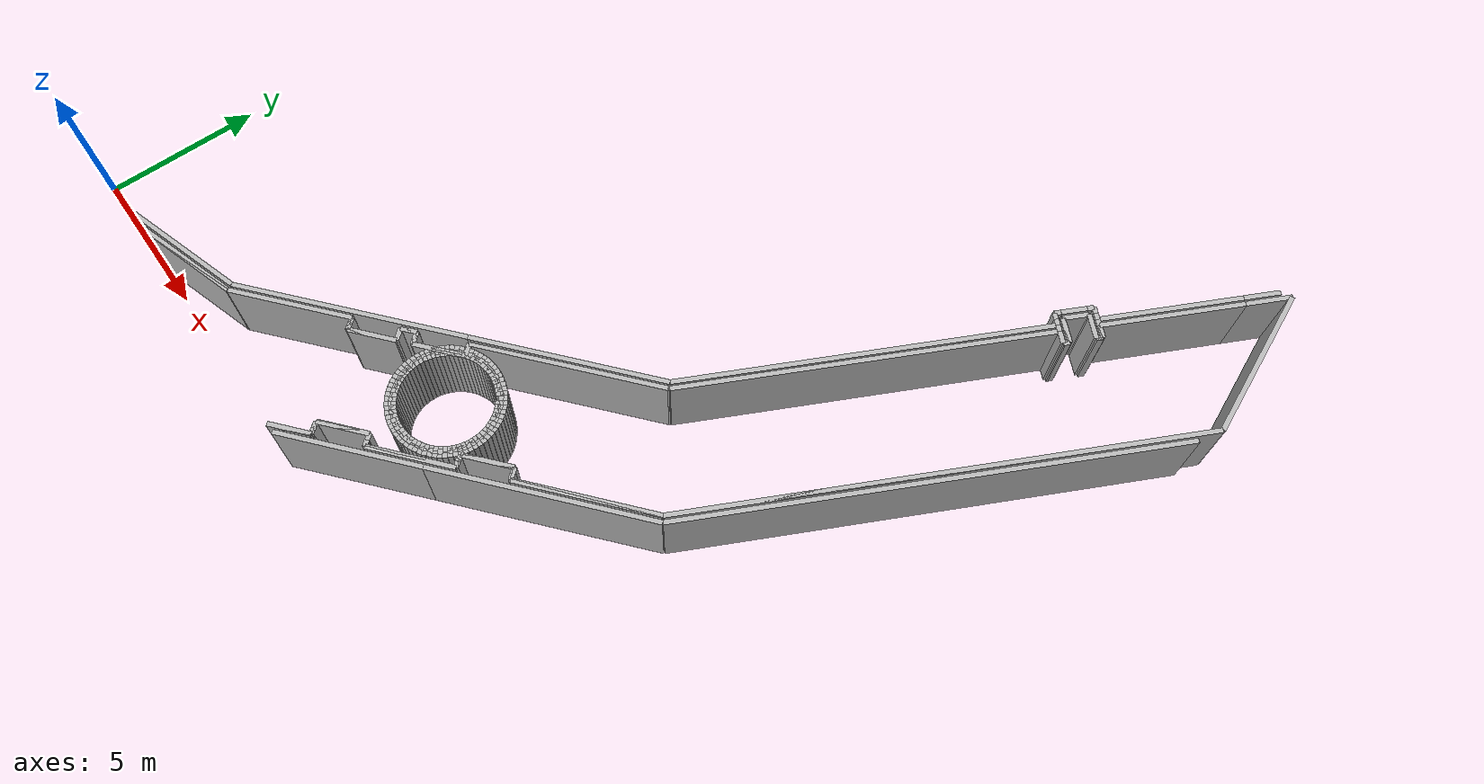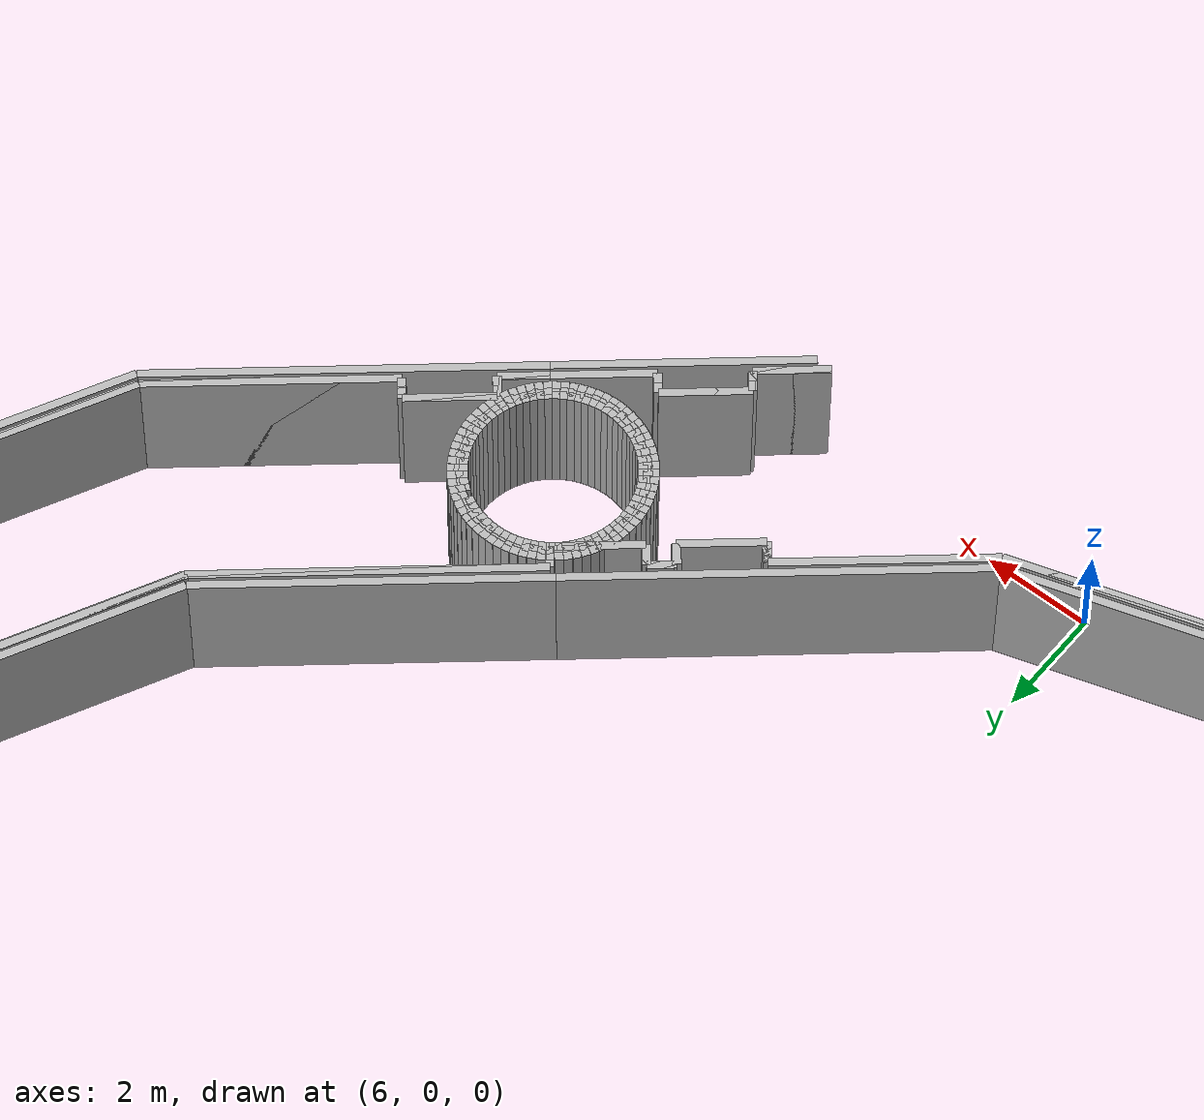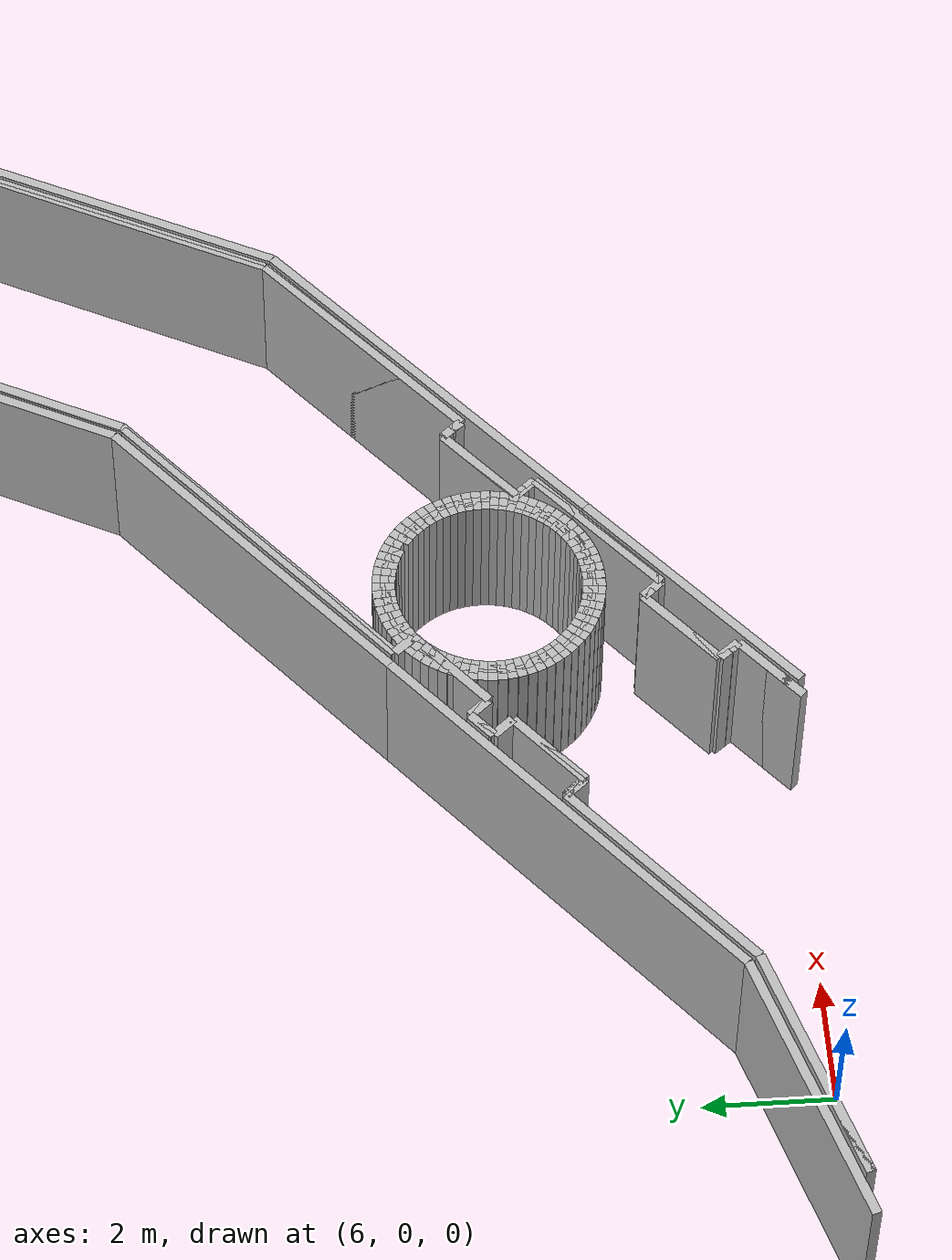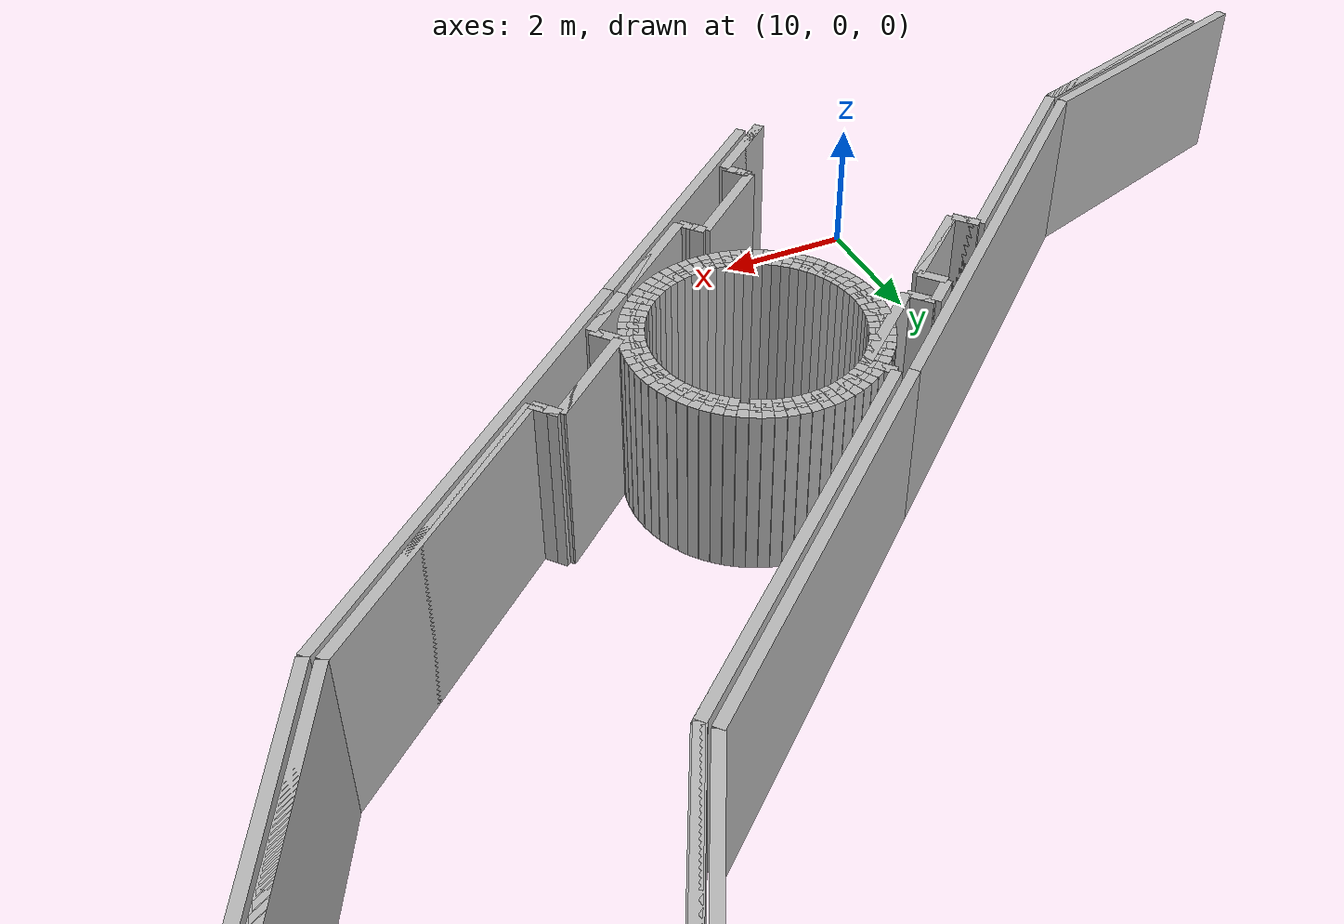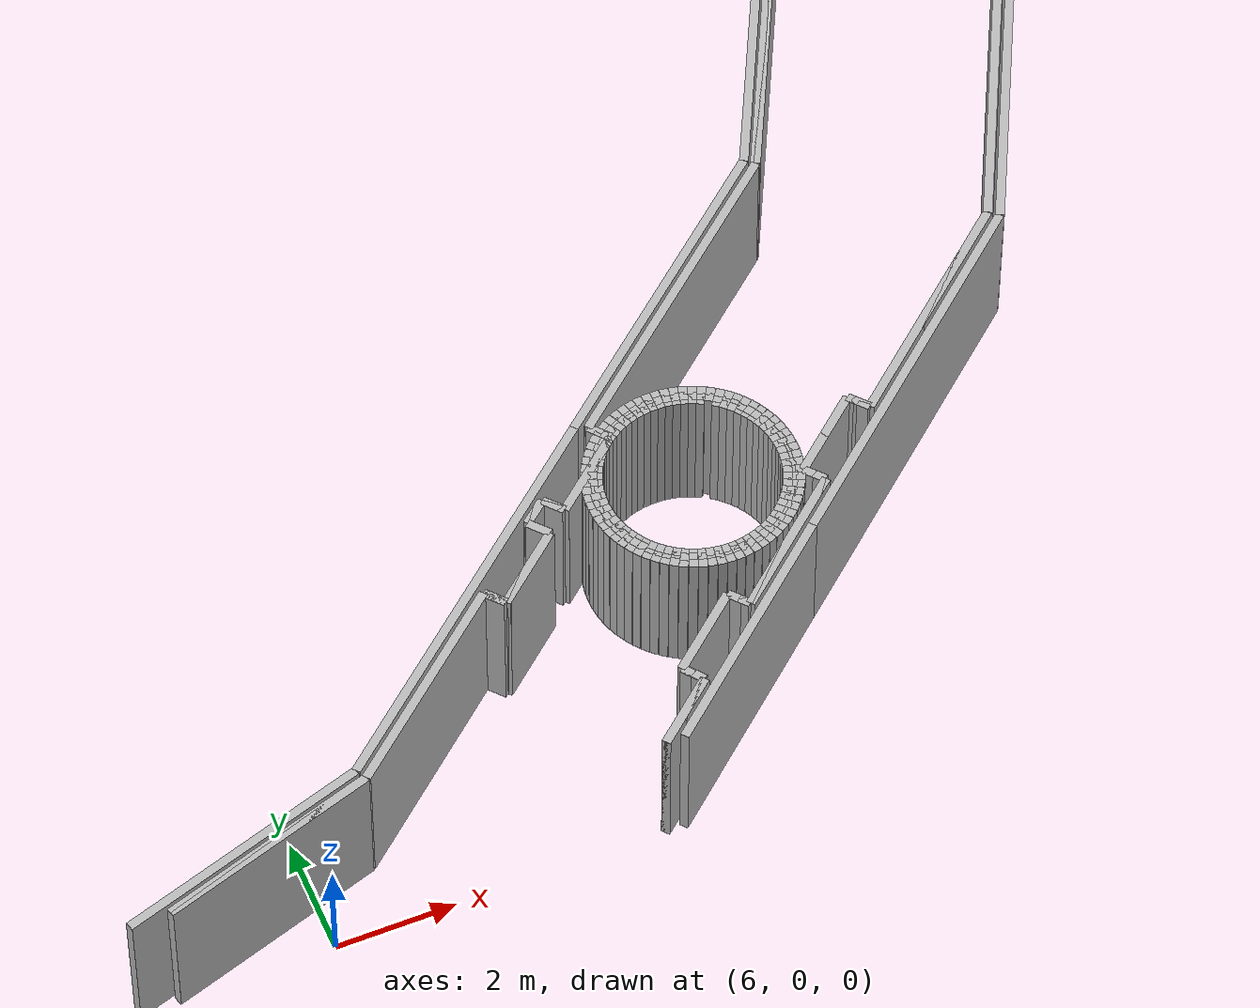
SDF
<?xml version="1.0" ?>
<sdf version="1.6">
  <model name="sps_1000">
    <pose frame="">0 0 0 0 -0 0</pose>
    <static>1</static>
    <self_collide>0</self_collide>
    <allow_auto_disable>0</allow_auto_disable>
    <link name="Wall468">
      <kinematic>0</kinematic>
      <gravity>1</gravity>
      <self_collide>0</self_collide>
      <collision name="collision">
        <geometry>
          <box>
            <size>0.400191 0.15 2.5</size>
          </box>
        </geometry>
        <pose frame="">0 0 0 0 -0 0</pose>
      </collision>
      <visual name="visual">
        <geometry>
          <box>
            <size>0.400191 0.15 2.5</size>
          </box>
        </geometry>
        <pose frame="">0 0 0 0 -0 0</pose>
        <cast_shadows>1</cast_shadows>
        <transparency>0.0</transparency>
      </visual>
      <pose frame="">11.2367 4.51289 1.25 0 -0 2.28042</pose>
    </link>
    <link name="Wall469">
      <kinematic>0</kinematic>
      <gravity>1</gravity>
      <self_collide>0</self_collide>
      <collision name="collision">
        <geometry>
          <box>
            <size>1.33494 0.15 2.5</size>
          </box>
        </geometry>
        <pose frame="">0 0 0 0 -0 0</pose>
      </collision>
      <visual name="visual">
        <geometry>
          <box>
            <size>1.33494 0.15 2.5</size>
          </box>
        </geometry>
        <pose frame="">0 0 0 0 -0 0</pose>
        <cast_shadows>1</cast_shadows>
        <transparency>0.0</transparency>
      </visual>
      <pose frame="">12.0152 0.435035 1.25 0 -0 0.709909</pose>
    </link>
    <link name="Wall761">
      <kinematic>0</kinematic>
      <gravity>1</gravity>
      <self_collide>0</self_collide>
      <collision name="collision">
        <geometry>
          <box>
            <size>0.499785 0.15 2.5</size>
          </box>
        </geometry>
        <pose frame="">0 0 0 0 -0 0</pose>
      </collision>
      <visual name="visual">
        <geometry>
          <box>
            <size>0.499785 0.15 2.5</size>
          </box>
        </geometry>
        <pose frame="">0 0 0 0 -0 0</pose>
        <cast_shadows>1</cast_shadows>
        <transparency>0.0</transparency>
      </visual>
      <pose frame="">11.2959 4.8275 1.25 0 -0 0.709593</pose>
    </link>
    <link name="Wall762">
      <kinematic>0</kinematic>
      <gravity>1</gravity>
      <self_collide>0</self_collide>
      <collision name="collision">
        <geometry>
          <box>
            <size>0.399776 0.15 2.5</size>
          </box>
        </geometry>
        <pose frame="">0 0 0 0 -0 0</pose>
      </collision>
      <visual name="visual">
        <geometry>
          <box>
            <size>0.399776 0.15 2.5</size>
          </box>
        </geometry>
        <pose frame="">0 0 0 0 -0 0</pose>
        <cast_shadows>1</cast_shadows>
        <transparency>0.0</transparency>
      </visual>
      <pose frame="">22.5817 20.2371 1.25 0 -0 2.68122</pose>
    </link>
    <link name="Wall764">
      <kinematic>0</kinematic>
      <gravity>1</gravity>
      <self_collide>0</self_collide>
      <collision name="collision">
        <geometry>
          <box>
            <size>0.20027 0.15 2.5</size>
          </box>
        </geometry>
        <pose frame="">0 0 0 0 -0 0</pose>
      </collision>
      <visual name="visual">
        <geometry>
          <box>
            <size>0.20027 0.15 2.5</size>
          </box>
        </geometry>
        <pose frame="">0 0 0 0 -0 0</pose>
        <cast_shadows>1</cast_shadows>
        <transparency>0.0</transparency>
      </visual>
      <pose frame="">23.249 21.1344 1.25 0 0 -2.03158</pose>
    </link>
    <link name="Wall1087">
      <kinematic>0</kinematic>
      <gravity>1</gravity>
      <self_collide>0</self_collide>
      <collision name="collision">
        <geometry>
          <box>
            <size>1.60021 0.15 2.5</size>
          </box>
        </geometry>
        <pose frame="">0 0 0 0 -0 0</pose>
      </collision>
      <visual name="visual">
        <geometry>
          <box>
            <size>1.60021 0.15 2.5</size>
          </box>
        </geometry>
        <pose frame="">0 0 0 0 -0 0</pose>
        <cast_shadows>1</cast_shadows>
        <transparency>0.0</transparency>
      </visual>
      <pose frame="">16.1283 4.49721 1.25 0 -0 0.709917</pose>
    </link>
    <link name="Wall1360">
      <kinematic>0</kinematic>
      <gravity>1</gravity>
      <self_collide>0</self_collide>
      <collision name="collision">
        <geometry>
          <box>
            <size>0.800209 0.15 2.5</size>
          </box>
        </geometry>
        <pose frame="">0 0 0 0 -0 0</pose>
      </collision>
      <visual name="visual">
        <geometry>
          <box>
            <size>0.800209 0.15 2.5</size>
          </box>
        </geometry>
        <pose frame="">0 0 0 0 -0 0</pose>
        <cast_shadows>1</cast_shadows>
        <transparency>0.0</transparency>
      </visual>
      <pose frame="">22.3106 21.0411 1.25 0 -0 1.11117</pose>
    </link>
    <link name="Wall1362">
      <kinematic>0</kinematic>
      <gravity>1</gravity>
      <self_collide>0</self_collide>
      <collision name="collision">
        <geometry>
          <box>
            <size>0.40095 0.15 2.5</size>
          </box>
        </geometry>
        <pose frame="">0 0 0 0 -0 0</pose>
      </collision>
      <visual name="visual">
        <geometry>
          <box>
            <size>0.40095 0.15 2.5</size>
          </box>
        </geometry>
        <pose frame="">0 0 0 0 -0 0</pose>
        <cast_shadows>1</cast_shadows>
        <transparency>0.0</transparency>
      </visual>
      <pose frame="">23.1139 21.3131 1.25 0 -0 2.68149</pose>
    </link>
    <link name="Wall1686">
      <kinematic>0</kinematic>
      <gravity>1</gravity>
      <self_collide>0</self_collide>
      <collision name="collision">
        <geometry>
          <box>
            <size>1.60002 0.15 2.5</size>
          </box>
        </geometry>
        <pose frame="">0 0 0 0 -0 0</pose>
      </collision>
      <visual name="visual">
        <geometry>
          <box>
            <size>1.60002 0.15 2.5</size>
          </box>
        </geometry>
        <pose frame="">0 0 0 0 -0 0</pose>
        <cast_shadows>1</cast_shadows>
        <transparency>0.0</transparency>
      </visual>
      <pose frame="">12.8671 1.69459 1.25 0 -0 0.710016</pose>
    </link>
    <link name="Wall1687">
      <kinematic>0</kinematic>
      <gravity>1</gravity>
      <self_collide>0</self_collide>
      <collision name="collision">
        <geometry>
          <box>
            <size>0.200488 0.15 2.5</size>
          </box>
        </geometry>
        <pose frame="">0 0 0 0 -0 0</pose>
      </collision>
      <visual name="visual">
        <geometry>
          <box>
            <size>0.200488 0.15 2.5</size>
          </box>
        </geometry>
        <pose frame="">0 0 0 0 -0 0</pose>
        <cast_shadows>1</cast_shadows>
        <transparency>0.0</transparency>
      </visual>
      <pose frame="">22.8054 20.2381 1.25 0 0 -2.03104</pose>
    </link>
    <link name="Wall1979">
      <kinematic>0</kinematic>
      <gravity>1</gravity>
      <self_collide>0</self_collide>
      <collision name="collision">
        <geometry>
          <box>
            <size>0.399695 0.15 2.5</size>
          </box>
        </geometry>
        <pose frame="">0 0 0 0 -0 0</pose>
      </collision>
      <visual name="visual">
        <geometry>
          <box>
            <size>0.399695 0.15 2.5</size>
          </box>
        </geometry>
        <pose frame="">0 0 0 0 -0 0</pose>
        <cast_shadows>1</cast_shadows>
        <transparency>0.0</transparency>
      </visual>
      <pose frame="">10.099 3.5352 1.25 0 -0 2.28108</pose>
    </link>
    <link name="Wall1980">
      <kinematic>0</kinematic>
      <gravity>1</gravity>
      <self_collide>0</self_collide>
      <collision name="collision">
        <geometry>
          <box>
            <size>1.50006 0.15 2.5</size>
          </box>
        </geometry>
        <pose frame="">0 0 0 0 -0 0</pose>
      </collision>
      <visual name="visual">
        <geometry>
          <box>
            <size>1.50006 0.15 2.5</size>
          </box>
        </geometry>
        <pose frame="">0 0 0 0 -0 0</pose>
        <cast_shadows>1</cast_shadows>
        <transparency>0.0</transparency>
      </visual>
      <pose frame="">10.7981 3.87248 1.25 0 -0 0.709831</pose>
    </link>
    <link name="Wall2314">
      <kinematic>0</kinematic>
      <gravity>1</gravity>
      <self_collide>0</self_collide>
      <collision name="collision">
        <geometry>
          <box>
            <size>0.399933 0.15 2.5</size>
          </box>
        </geometry>
        <pose frame="">0 0 0 0 -0 0</pose>
      </collision>
      <visual name="visual">
        <geometry>
          <box>
            <size>0.399933 0.15 2.5</size>
          </box>
        </geometry>
        <pose frame="">0 0 0 0 -0 0</pose>
        <cast_shadows>1</cast_shadows>
        <transparency>0.0</transparency>
      </visual>
      <pose frame="">11.616 4.83861 1.25 0 -0 2.28037</pose>
    </link>
    <link name="Wall2315">
      <kinematic>0</kinematic>
      <gravity>1</gravity>
      <self_collide>0</self_collide>
      <collision name="collision">
        <geometry>
          <box>
            <size>0.00130621 0.15 2.5</size>
          </box>
        </geometry>
        <pose frame="">0 0 0 0 -0 0</pose>
      </collision>
      <visual name="visual">
        <geometry>
          <box>
            <size>0.00130621 0.15 2.5</size>
          </box>
        </geometry>
        <pose frame="">0 0 0 0 -0 0</pose>
        <cast_shadows>1</cast_shadows>
        <transparency>0.0</transparency>
      </visual>
      <pose frame="">12.6525 0.717391 1.25 0 -0 2.22364</pose>
    </link>
    <link name="Wall2316">
      <kinematic>0</kinematic>
      <gravity>1</gravity>
      <self_collide>0</self_collide>
      <collision name="collision">
        <geometry>
          <box>
            <size>0.399907 0.15 2.5</size>
          </box>
        </geometry>
        <pose frame="">0 0 0 0 -0 0</pose>
      </collision>
      <visual name="visual">
        <geometry>
          <box>
            <size>0.399907 0.15 2.5</size>
          </box>
        </geometry>
        <pose frame="">0 0 0 0 -0 0</pose>
        <cast_shadows>1</cast_shadows>
        <transparency>0.0</transparency>
      </visual>
      <pose frame="">12.8293 5.8817 1.25 0 -0 2.28123</pose>
    </link>
    <link name="Wall7673">
      <kinematic>0</kinematic>
      <gravity>1</gravity>
      <self_collide>0</self_collide>
      <collision name="collision">
        <geometry>
          <box>
            <size>3.80529 0.15 2.5</size>
          </box>
        </geometry>
        <pose frame="">0 0 0 0 -0 0</pose>
      </collision>
      <visual name="visual">
        <geometry>
          <box>
            <size>3.80529 0.15 2.5</size>
          </box>
        </geometry>
        <pose frame="">0 0 0 0 -0 0</pose>
        <cast_shadows>1</cast_shadows>
        <transparency>0.0</transparency>
      </visual>
      <pose frame="">5.2102 0.577644 1.25 0 -0 0.308469</pose>
    </link>
    <link name="Wall7674">
      <kinematic>0</kinematic>
      <gravity>1</gravity>
      <self_collide>0</self_collide>
      <collision name="collision">
        <geometry>
          <box>
            <size>3.88392 0.15 2.5</size>
          </box>
        </geometry>
        <pose frame="">0 0 0 0 -0 0</pose>
      </collision>
      <visual name="visual">
        <geometry>
          <box>
            <size>3.88392 0.15 2.5</size>
          </box>
        </geometry>
        <pose frame="">0 0 0 0 -0 0</pose>
        <cast_shadows>1</cast_shadows>
        <transparency>0.0</transparency>
      </visual>
      <pose frame="">8.49584 2.421 1.25 0 -0 0.70992</pose>
    </link>
    <link name="Wall7675">
      <kinematic>0</kinematic>
      <gravity>1</gravity>
      <self_collide>0</self_collide>
      <collision name="collision">
        <geometry>
          <box>
            <size>0.399695 0.15 2.5</size>
          </box>
        </geometry>
        <pose frame="">0 0 0 0 -0 0</pose>
      </collision>
      <visual name="visual">
        <geometry>
          <box>
            <size>0.399695 0.15 2.5</size>
          </box>
        </geometry>
        <pose frame="">0 0 0 0 -0 0</pose>
        <cast_shadows>1</cast_shadows>
        <transparency>0.0</transparency>
      </visual>
      <pose frame="">10.099 3.5352 1.25 0 0 -0.860514</pose>
    </link>
    <link name="Wall7676">
      <kinematic>0</kinematic>
      <gravity>1</gravity>
      <self_collide>0</self_collide>
      <collision name="collision">
        <geometry>
          <box>
            <size>1.49994 0.15 2.5</size>
          </box>
        </geometry>
        <pose frame="">0 0 0 0 -0 0</pose>
      </collision>
      <visual name="visual">
        <geometry>
          <box>
            <size>1.49994 0.15 2.5</size>
          </box>
        </geometry>
        <pose frame="">0 0 0 0 -0 0</pose>
        <cast_shadows>1</cast_shadows>
        <transparency>0.0</transparency>
      </visual>
      <pose frame="">10.7981 3.87239 1.25 0 -0 0.709739</pose>
    </link>
    <link name="Wall7677">
      <kinematic>0</kinematic>
      <gravity>1</gravity>
      <self_collide>0</self_collide>
      <collision name="collision">
        <geometry>
          <box>
            <size>0.400191 0.15 2.5</size>
          </box>
        </geometry>
        <pose frame="">0 0 0 0 -0 0</pose>
      </collision>
      <visual name="visual">
        <geometry>
          <box>
            <size>0.400191 0.15 2.5</size>
          </box>
        </geometry>
        <pose frame="">0 0 0 0 -0 0</pose>
        <cast_shadows>1</cast_shadows>
        <transparency>0.0</transparency>
      </visual>
      <pose frame="">11.2367 4.51289 1.25 0 -0 2.28042</pose>
    </link>
    <link name="Wall7678">
      <kinematic>0</kinematic>
      <gravity>1</gravity>
      <self_collide>0</self_collide>
      <collision name="collision">
        <geometry>
          <box>
            <size>0.49997 0.15 2.5</size>
          </box>
        </geometry>
        <pose frame="">0 0 0 0 -0 0</pose>
      </collision>
      <visual name="visual">
        <geometry>
          <box>
            <size>0.49997 0.15 2.5</size>
          </box>
        </geometry>
        <pose frame="">0 0 0 0 -0 0</pose>
        <cast_shadows>1</cast_shadows>
        <transparency>0.0</transparency>
      </visual>
      <pose frame="">11.296 4.8275 1.25 0 -0 0.709275</pose>
    </link>
    <link name="Wall7679">
      <kinematic>0</kinematic>
      <gravity>1</gravity>
      <self_collide>0</self_collide>
      <collision name="collision">
        <geometry>
          <box>
            <size>0.399794 0.15 2.5</size>
          </box>
        </geometry>
        <pose frame="">0 0 0 0 -0 0</pose>
      </collision>
      <visual name="visual">
        <geometry>
          <box>
            <size>0.399794 0.15 2.5</size>
          </box>
        </geometry>
        <pose frame="">0 0 0 0 -0 0</pose>
        <cast_shadows>1</cast_shadows>
        <transparency>0.0</transparency>
      </visual>
      <pose frame="">11.616 4.8387 1.25 0 0 -0.860928</pose>
    </link>
    <link name="Wall7680">
      <kinematic>0</kinematic>
      <gravity>1</gravity>
      <self_collide>0</self_collide>
      <collision name="collision">
        <geometry>
          <box>
            <size>1.60011 0.15 2.5</size>
          </box>
        </geometry>
        <pose frame="">0 0 0 0 -0 0</pose>
      </collision>
      <visual name="visual">
        <geometry>
          <box>
            <size>1.60011 0.15 2.5</size>
          </box>
        </geometry>
        <pose frame="">0 0 0 0 -0 0</pose>
        <cast_shadows>1</cast_shadows>
        <transparency>0.0</transparency>
      </visual>
      <pose frame="">12.353 5.2086 1.25 0 -0 0.710021</pose>
    </link>
    <link name="Wall7681">
      <kinematic>0</kinematic>
      <gravity>1</gravity>
      <self_collide>0</self_collide>
      <collision name="collision">
        <geometry>
          <box>
            <size>0.399907 0.15 2.5</size>
          </box>
        </geometry>
        <pose frame="">0 0 0 0 -0 0</pose>
      </collision>
      <visual name="visual">
        <geometry>
          <box>
            <size>0.399907 0.15 2.5</size>
          </box>
        </geometry>
        <pose frame="">0 0 0 0 -0 0</pose>
        <cast_shadows>1</cast_shadows>
        <transparency>0.0</transparency>
      </visual>
      <pose frame="">12.8293 5.8817 1.25 0 -0 2.28123</pose>
    </link>
    <link name="Wall7682">
      <kinematic>0</kinematic>
      <gravity>1</gravity>
      <self_collide>0</self_collide>
      <collision name="collision">
        <geometry>
          <box>
            <size>5.98768 0.15 2.5</size>
          </box>
        </geometry>
        <pose frame="">0 0 0 0 -0 0</pose>
      </collision>
      <visual name="visual">
        <geometry>
          <box>
            <size>5.98768 0.15 2.5</size>
          </box>
        </geometry>
        <pose frame="">0 0 0 0 -0 0</pose>
        <cast_shadows>1</cast_shadows>
        <transparency>0.0</transparency>
      </visual>
      <pose frame="">14.9694 7.98469 1.25 0 -0 0.709969</pose>
    </link>
    <link name="Wall7683">
      <kinematic>0</kinematic>
      <gravity>1</gravity>
      <self_collide>0</self_collide>
      <collision name="collision">
        <geometry>
          <box>
            <size>11.602 0.15 2.5</size>
          </box>
        </geometry>
        <pose frame="">0 0 0 0 -0 0</pose>
      </collision>
      <visual name="visual">
        <geometry>
          <box>
            <size>11.602 0.15 2.5</size>
          </box>
        </geometry>
        <pose frame="">0 0 0 0 -0 0</pose>
        <cast_shadows>1</cast_shadows>
        <transparency>0.0</transparency>
      </visual>
      <pose frame="">19.818 15.1327 1.25 0 -0 1.11026</pose>
    </link>
    <link name="Wall7684">
      <kinematic>0</kinematic>
      <gravity>1</gravity>
      <self_collide>0</self_collide>
      <collision name="collision">
        <geometry>
          <box>
            <size>0.4072 0.15 2.5</size>
          </box>
        </geometry>
        <pose frame="">0 0 0 0 -0 0</pose>
      </collision>
      <visual name="visual">
        <geometry>
          <box>
            <size>0.4072 0.15 2.5</size>
          </box>
        </geometry>
        <pose frame="">0 0 0 0 -0 0</pose>
        <cast_shadows>1</cast_shadows>
        <transparency>0.0</transparency>
      </visual>
      <pose frame="">22.5785 20.2388 1.25 0 0 -0.460698</pose>
    </link>
    <link name="Wall7685">
      <kinematic>0</kinematic>
      <gravity>1</gravity>
      <self_collide>0</self_collide>
      <collision name="collision">
        <geometry>
          <box>
            <size>0.200488 0.15 2.5</size>
          </box>
        </geometry>
        <pose frame="">0 0 0 0 -0 0</pose>
      </collision>
      <visual name="visual">
        <geometry>
          <box>
            <size>0.200488 0.15 2.5</size>
          </box>
        </geometry>
        <pose frame="">0 0 0 0 -0 0</pose>
        <cast_shadows>1</cast_shadows>
        <transparency>0.0</transparency>
      </visual>
      <pose frame="">22.8054 20.2381 1.25 0 -0 1.11055</pose>
    </link>
    <link name="Wall7686">
      <kinematic>0</kinematic>
      <gravity>1</gravity>
      <self_collide>0</self_collide>
      <collision name="collision">
        <geometry>
          <box>
            <size>0.799718 0.15 2.5</size>
          </box>
        </geometry>
        <pose frame="">0 0 0 0 -0 0</pose>
      </collision>
      <visual name="visual">
        <geometry>
          <box>
            <size>0.799718 0.15 2.5</size>
          </box>
        </geometry>
        <pose frame="">0 0 0 0 -0 0</pose>
        <cast_shadows>1</cast_shadows>
        <transparency>0.0</transparency>
      </visual>
      <pose frame="">22.4915 20.5052 1.25 0 -0 2.68218</pose>
    </link>
    <link name="Wall7687">
      <kinematic>0</kinematic>
      <gravity>1</gravity>
      <self_collide>0</self_collide>
      <collision name="collision">
        <geometry>
          <box>
            <size>0.800209 0.15 2.5</size>
          </box>
        </geometry>
        <pose frame="">0 0 0 0 -0 0</pose>
      </collision>
      <visual name="visual">
        <geometry>
          <box>
            <size>0.800209 0.15 2.5</size>
          </box>
        </geometry>
        <pose frame="">0 0 0 0 -0 0</pose>
        <cast_shadows>1</cast_shadows>
        <transparency>0.0</transparency>
      </visual>
      <pose frame="">22.3106 21.0411 1.25 0 -0 1.11117</pose>
    </link>
    <link name="Wall7688">
      <kinematic>0</kinematic>
      <gravity>1</gravity>
      <self_collide>0</self_collide>
      <collision name="collision">
        <geometry>
          <box>
            <size>0.799498 0.15 2.5</size>
          </box>
        </geometry>
        <pose frame="">0 0 0 0 -0 0</pose>
      </collision>
      <visual name="visual">
        <geometry>
          <box>
            <size>0.799498 0.15 2.5</size>
          </box>
        </geometry>
        <pose frame="">0 0 0 0 -0 0</pose>
        <cast_shadows>1</cast_shadows>
        <transparency>0.0</transparency>
      </visual>
      <pose frame="">22.8462 21.2222 1.25 0 0 -0.460063</pose>
    </link>
    <link name="Wall7689">
      <kinematic>0</kinematic>
      <gravity>1</gravity>
      <self_collide>0</self_collide>
      <collision name="collision">
        <geometry>
          <box>
            <size>0.20027 0.15 2.5</size>
          </box>
        </geometry>
        <pose frame="">0 0 0 0 -0 0</pose>
      </collision>
      <visual name="visual">
        <geometry>
          <box>
            <size>0.20027 0.15 2.5</size>
          </box>
        </geometry>
        <pose frame="">0 0 0 0 -0 0</pose>
        <cast_shadows>1</cast_shadows>
        <transparency>0.0</transparency>
      </visual>
      <pose frame="">23.249 21.1344 1.25 0 -0 1.11001</pose>
    </link>
    <link name="Wall7690">
      <kinematic>0</kinematic>
      <gravity>1</gravity>
      <self_collide>0</self_collide>
      <collision name="collision">
        <geometry>
          <box>
            <size>0.406272 0.15 2.5</size>
          </box>
        </geometry>
        <pose frame="">0 0 0 0 -0 0</pose>
      </collision>
      <visual name="visual">
        <geometry>
          <box>
            <size>0.406272 0.15 2.5</size>
          </box>
        </geometry>
        <pose frame="">0 0 0 0 -0 0</pose>
        <cast_shadows>1</cast_shadows>
        <transparency>0.0</transparency>
      </visual>
      <pose frame="">23.1115 21.3143 1.25 0 -0 2.68144</pose>
    </link>
    <link name="Wall7691">
      <kinematic>0</kinematic>
      <gravity>1</gravity>
      <self_collide>0</self_collide>
      <collision name="collision">
        <geometry>
          <box>
            <size>5.89954 0.15 2.5</size>
          </box>
        </geometry>
        <pose frame="">0 0 0 0 -0 0</pose>
      </collision>
      <visual name="visual">
        <geometry>
          <box>
            <size>5.89954 0.15 2.5</size>
          </box>
        </geometry>
        <pose frame="">0 0 0 0 -0 0</pose>
        <cast_shadows>1</cast_shadows>
        <transparency>0.0</transparency>
      </visual>
      <pose frame="">24.2403 24.047 1.25 0 -0 1.11029</pose>
    </link>
    <link name="Wall7692">
      <kinematic>0</kinematic>
      <gravity>1</gravity>
      <self_collide>0</self_collide>
      <collision name="collision">
        <geometry>
          <box>
            <size>5.05114 0.15 2.5</size>
          </box>
        </geometry>
        <pose frame="">0 0 0 0 -0 0</pose>
      </collision>
      <visual name="visual">
        <geometry>
          <box>
            <size>5.05114 0.15 2.5</size>
          </box>
        </geometry>
        <pose frame="">0 0 0 0 -0 0</pose>
        <cast_shadows>1</cast_shadows>
        <transparency>0.0</transparency>
      </visual>
      <pose frame="">26.5163 24.3556 1.25 0 0 -1.17869</pose>
    </link>
    <link name="Wall7693">
      <kinematic>0</kinematic>
      <gravity>1</gravity>
      <self_collide>0</self_collide>
      <collision name="collision">
        <geometry>
          <box>
            <size>16.1011 0.15 2.5</size>
          </box>
        </geometry>
        <pose frame="">0 0 0 0 -0 0</pose>
      </collision>
      <visual name="visual">
        <geometry>
          <box>
            <size>16.1011 0.15 2.5</size>
          </box>
        </geometry>
        <pose frame="">0 0 0 0 -0 0</pose>
        <cast_shadows>1</cast_shadows>
        <transparency>0.0</transparency>
      </visual>
      <pose frame="">23.911 14.8062 1.25 0 0 -2.03031</pose>
    </link>
    <link name="Wall7694">
      <kinematic>0</kinematic>
      <gravity>1</gravity>
      <self_collide>0</self_collide>
      <collision name="collision">
        <geometry>
          <box>
            <size>4.41077 0.15 2.5</size>
          </box>
        </geometry>
        <pose frame="">0 0 0 0 -0 0</pose>
      </collision>
      <visual name="visual">
        <geometry>
          <box>
            <size>4.41077 0.15 2.5</size>
          </box>
        </geometry>
        <pose frame="">0 0 0 0 -0 0</pose>
        <cast_shadows>1</cast_shadows>
        <transparency>0.0</transparency>
      </visual>
      <pose frame="">18.668 6.15321 1.25 0 0 -2.43162</pose>
    </link>
    <link name="Wall7695">
      <kinematic>0</kinematic>
      <gravity>1</gravity>
      <self_collide>0</self_collide>
      <collision name="collision">
        <geometry>
          <box>
            <size>0.399489 0.15 2.5</size>
          </box>
        </geometry>
        <pose frame="">0 0 0 0 -0 0</pose>
      </collision>
      <visual name="visual">
        <geometry>
          <box>
            <size>0.399489 0.15 2.5</size>
          </box>
        </geometry>
        <pose frame="">0 0 0 0 -0 0</pose>
        <cast_shadows>1</cast_shadows>
        <transparency>0.0</transparency>
      </visual>
      <pose frame="">16.8653 4.8672 1.25 0 -0 2.28072</pose>
    </link>
    <link name="Wall7696">
      <kinematic>0</kinematic>
      <gravity>1</gravity>
      <self_collide>0</self_collide>
      <collision name="collision">
        <geometry>
          <box>
            <size>1.60023 0.15 2.5</size>
          </box>
        </geometry>
        <pose frame="">0 0 0 0 -0 0</pose>
      </collision>
      <visual name="visual">
        <geometry>
          <box>
            <size>1.60023 0.15 2.5</size>
          </box>
        </geometry>
        <pose frame="">0 0 0 0 -0 0</pose>
        <cast_shadows>1</cast_shadows>
        <transparency>0.0</transparency>
      </visual>
      <pose frame="">16.1282 4.4973 1.25 0 0 -2.43184</pose>
    </link>
    <link name="Wall7697">
      <kinematic>0</kinematic>
      <gravity>1</gravity>
      <self_collide>0</self_collide>
      <collision name="collision">
        <geometry>
          <box>
            <size>0.400092 0.15 2.5</size>
          </box>
        </geometry>
        <pose frame="">0 0 0 0 -0 0</pose>
      </collision>
      <visual name="visual">
        <geometry>
          <box>
            <size>0.400092 0.15 2.5</size>
          </box>
        </geometry>
        <pose frame="">0 0 0 0 -0 0</pose>
        <cast_shadows>1</cast_shadows>
        <transparency>0.0</transparency>
      </visual>
      <pose frame="">15.6517 3.8242 1.25 0 0 -0.860764</pose>
    </link>
    <link name="Wall7698">
      <kinematic>0</kinematic>
      <gravity>1</gravity>
      <self_collide>0</self_collide>
      <collision name="collision">
        <geometry>
          <box>
            <size>2.69978 0.15 2.5</size>
          </box>
        </geometry>
        <pose frame="">0 0 0 0 -0 0</pose>
      </collision>
      <visual name="visual">
        <geometry>
          <box>
            <size>2.69978 0.15 2.5</size>
          </box>
        </geometry>
        <pose frame="">0 0 0 0 -0 0</pose>
        <cast_shadows>1</cast_shadows>
        <transparency>0.0</transparency>
      </visual>
      <pose frame="">14.7583 2.79271 1.25 0 0 -2.4317</pose>
    </link>
    <link name="Wall7699">
      <kinematic>0</kinematic>
      <gravity>1</gravity>
      <self_collide>0</self_collide>
      <collision name="collision">
        <geometry>
          <box>
            <size>0.399787 0.15 2.5</size>
          </box>
        </geometry>
        <pose frame="">0 0 0 0 -0 0</pose>
      </collision>
      <visual name="visual">
        <geometry>
          <box>
            <size>0.399787 0.15 2.5</size>
          </box>
        </geometry>
        <pose frame="">0 0 0 0 -0 0</pose>
        <cast_shadows>1</cast_shadows>
        <transparency>0.0</transparency>
      </visual>
      <pose frame="">13.6041 2.0645 1.25 0 -0 2.28088</pose>
    </link>
    <link name="Wall7700">
      <kinematic>0</kinematic>
      <gravity>1</gravity>
      <self_collide>0</self_collide>
      <collision name="collision">
        <geometry>
          <box>
            <size>1.58531 0.15 2.5</size>
          </box>
        </geometry>
        <pose frame="">0 0 0 0 -0 0</pose>
      </collision>
      <visual name="visual">
        <geometry>
          <box>
            <size>1.58531 0.15 2.5</size>
          </box>
        </geometry>
        <pose frame="">0 0 0 0 -0 0</pose>
        <cast_shadows>1</cast_shadows>
        <transparency>0.0</transparency>
      </visual>
      <pose frame="">12.8727 1.69939 1.25 0 0 -2.43157</pose>
    </link>
    <link name="Wall7701">
      <kinematic>0</kinematic>
      <gravity>1</gravity>
      <self_collide>0</self_collide>
      <collision name="collision">
        <geometry>
          <box>
            <size>0.400176 0.15 2.5</size>
          </box>
        </geometry>
        <pose frame="">0 0 0 0 -0 0</pose>
      </collision>
      <visual name="visual">
        <geometry>
          <box>
            <size>0.400176 0.15 2.5</size>
          </box>
        </geometry>
        <pose frame="">0 0 0 0 -0 0</pose>
        <cast_shadows>1</cast_shadows>
        <transparency>0.0</transparency>
      </visual>
      <pose frame="">12.3965 1.02638 1.25 0 0 -0.896603</pose>
    </link>
    <link name="Wall7702">
      <kinematic>0</kinematic>
      <gravity>1</gravity>
      <self_collide>0</self_collide>
      <collision name="collision">
        <geometry>
          <box>
            <size>1.33494 0.15 2.5</size>
          </box>
        </geometry>
        <pose frame="">0 0 0 0 -0 0</pose>
      </collision>
      <visual name="visual">
        <geometry>
          <box>
            <size>1.33494 0.15 2.5</size>
          </box>
        </geometry>
        <pose frame="">0 0 0 0 -0 0</pose>
        <cast_shadows>1</cast_shadows>
        <transparency>0.0</transparency>
      </visual>
      <pose frame="">12.0152 0.435035 1.25 0 0 -2.43168</pose>
    </link>
    <link name="Wall9812">
      <kinematic>0</kinematic>
      <gravity>1</gravity>
      <self_collide>0</self_collide>
      <collision name="collision">
        <geometry>
          <box>
            <size>0.130818 0.15 2.5</size>
          </box>
        </geometry>
        <pose frame="">0 0 0 0 -0 0</pose>
      </collision>
      <visual name="visual">
        <geometry>
          <box>
            <size>0.130818 0.15 2.5</size>
          </box>
        </geometry>
        <pose frame="">0 0 0 0 -0 0</pose>
        <cast_shadows>1</cast_shadows>
        <transparency>0.0</transparency>
      </visual>
      <pose frame="">14.7736 5.71547 1.25 0 0 -0.654046</pose>
    </link>
    <link name="Wall9813">
      <kinematic>0</kinematic>
      <gravity>1</gravity>
      <self_collide>0</self_collide>
      <collision name="collision">
        <geometry>
          <box>
            <size>0.130763 0.15 2.5</size>
          </box>
        </geometry>
        <pose frame="">0 0 0 0 -0 0</pose>
      </collision>
      <visual name="visual">
        <geometry>
          <box>
            <size>0.130763 0.15 2.5</size>
          </box>
        </geometry>
        <pose frame="">0 0 0 0 -0 0</pose>
        <cast_shadows>1</cast_shadows>
        <transparency>0.0</transparency>
      </visual>
      <pose frame="">14.8736 5.63148 1.25 0 0 -0.742148</pose>
    </link>
    <link name="Wall9814">
      <kinematic>0</kinematic>
      <gravity>1</gravity>
      <self_collide>0</self_collide>
      <collision name="collision">
        <geometry>
          <box>
            <size>0.130984 0.15 2.5</size>
          </box>
        </geometry>
        <pose frame="">0 0 0 0 -0 0</pose>
      </collision>
      <visual name="visual">
        <geometry>
          <box>
            <size>0.130984 0.15 2.5</size>
          </box>
        </geometry>
        <pose frame="">0 0 0 0 -0 0</pose>
        <cast_shadows>1</cast_shadows>
        <transparency>0.0</transparency>
      </visual>
      <pose frame="">14.9661 5.53899 1.25 0 0 -0.829565</pose>
    </link>
    <link name="Wall9815">
      <kinematic>0</kinematic>
      <gravity>1</gravity>
      <self_collide>0</self_collide>
      <collision name="collision">
        <geometry>
          <box>
            <size>0.130881 0.15 2.5</size>
          </box>
        </geometry>
        <pose frame="">0 0 0 0 -0 0</pose>
      </collision>
      <visual name="visual">
        <geometry>
          <box>
            <size>0.130881 0.15 2.5</size>
          </box>
        </geometry>
        <pose frame="">0 0 0 0 -0 0</pose>
        <cast_shadows>1</cast_shadows>
        <transparency>0.0</transparency>
      </visual>
      <pose frame="">15.0502 5.4388 1.25 0 0 -0.915357</pose>
    </link>
    <link name="Wall9816">
      <kinematic>0</kinematic>
      <gravity>1</gravity>
      <self_collide>0</self_collide>
      <collision name="collision">
        <geometry>
          <box>
            <size>0.130834 0.15 2.5</size>
          </box>
        </geometry>
        <pose frame="">0 0 0 0 -0 0</pose>
      </collision>
      <visual name="visual">
        <geometry>
          <box>
            <size>0.130834 0.15 2.5</size>
          </box>
        </geometry>
        <pose frame="">0 0 0 0 -0 0</pose>
        <cast_shadows>1</cast_shadows>
        <transparency>0.0</transparency>
      </visual>
      <pose frame="">15.1251 5.33171 1.25 0 0 -1.00453</pose>
    </link>
    <link name="Wall9817">
      <kinematic>0</kinematic>
      <gravity>1</gravity>
      <self_collide>0</self_collide>
      <collision name="collision">
        <geometry>
          <box>
            <size>0.130819 0.15 2.5</size>
          </box>
        </geometry>
        <pose frame="">0 0 0 0 -0 0</pose>
      </collision>
      <visual name="visual">
        <geometry>
          <box>
            <size>0.130819 0.15 2.5</size>
          </box>
        </geometry>
        <pose frame="">0 0 0 0 -0 0</pose>
        <cast_shadows>1</cast_shadows>
        <transparency>0.0</transparency>
      </visual>
      <pose frame="">15.1905 5.21849 1.25 0 0 -1.09066</pose>
    </link>
    <link name="Wall9818">
      <kinematic>0</kinematic>
      <gravity>1</gravity>
      <self_collide>0</self_collide>
      <collision name="collision">
        <geometry>
          <box>
            <size>0.130893 0.15 2.5</size>
          </box>
        </geometry>
        <pose frame="">0 0 0 0 -0 0</pose>
      </collision>
      <visual name="visual">
        <geometry>
          <box>
            <size>0.130893 0.15 2.5</size>
          </box>
        </geometry>
        <pose frame="">0 0 0 0 -0 0</pose>
        <cast_shadows>1</cast_shadows>
        <transparency>0.0</transparency>
      </visual>
      <pose frame="">15.2457 5.09999 1.25 0 0 -1.17895</pose>
    </link>
    <link name="Wall9819">
      <kinematic>0</kinematic>
      <gravity>1</gravity>
      <self_collide>0</self_collide>
      <collision name="collision">
        <geometry>
          <box>
            <size>0.130896 0.15 2.5</size>
          </box>
        </geometry>
        <pose frame="">0 0 0 0 -0 0</pose>
      </collision>
      <visual name="visual">
        <geometry>
          <box>
            <size>0.130896 0.15 2.5</size>
          </box>
        </geometry>
        <pose frame="">0 0 0 0 -0 0</pose>
        <cast_shadows>1</cast_shadows>
        <transparency>0.0</transparency>
      </visual>
      <pose frame="">15.2904 4.9771 1.25 0 0 -1.26482</pose>
    </link>
    <link name="Wall9820">
      <kinematic>0</kinematic>
      <gravity>1</gravity>
      <self_collide>0</self_collide>
      <collision name="collision">
        <geometry>
          <box>
            <size>0.130881 0.15 2.5</size>
          </box>
        </geometry>
        <pose frame="">0 0 0 0 -0 0</pose>
      </collision>
      <visual name="visual">
        <geometry>
          <box>
            <size>0.130881 0.15 2.5</size>
          </box>
        </geometry>
        <pose frame="">0 0 0 0 -0 0</pose>
        <cast_shadows>1</cast_shadows>
        <transparency>0.0</transparency>
      </visual>
      <pose frame="">15.3242 4.85078 1.25 0 0 -1.35364</pose>
    </link>
    <link name="Wall9821">
      <kinematic>0</kinematic>
      <gravity>1</gravity>
      <self_collide>0</self_collide>
      <collision name="collision">
        <geometry>
          <box>
            <size>0.130865 0.15 2.5</size>
          </box>
        </geometry>
        <pose frame="">0 0 0 0 -0 0</pose>
      </collision>
      <visual name="visual">
        <geometry>
          <box>
            <size>0.130865 0.15 2.5</size>
          </box>
        </geometry>
        <pose frame="">0 0 0 0 -0 0</pose>
        <cast_shadows>1</cast_shadows>
        <transparency>0.0</transparency>
      </visual>
      <pose frame="">15.3468 4.722 1.25 0 0 -1.44077</pose>
    </link>
    <link name="Wall9822">
      <kinematic>0</kinematic>
      <gravity>1</gravity>
      <self_collide>0</self_collide>
      <collision name="collision">
        <geometry>
          <box>
            <size>0.130744 0.15 2.5</size>
          </box>
        </geometry>
        <pose frame="">0 0 0 0 -0 0</pose>
      </collision>
      <visual name="visual">
        <geometry>
          <box>
            <size>0.130744 0.15 2.5</size>
          </box>
        </geometry>
        <pose frame="">0 0 0 0 -0 0</pose>
        <cast_shadows>1</cast_shadows>
        <transparency>0.0</transparency>
      </visual>
      <pose frame="">15.3581 4.59181 1.25 0 0 -1.52643</pose>
    </link>
    <link name="Wall9823">
      <kinematic>0</kinematic>
      <gravity>1</gravity>
      <self_collide>0</self_collide>
      <collision name="collision">
        <geometry>
          <box>
            <size>0.130927 0.15 2.5</size>
          </box>
        </geometry>
        <pose frame="">0 0 0 0 -0 0</pose>
      </collision>
      <visual name="visual">
        <geometry>
          <box>
            <size>0.130927 0.15 2.5</size>
          </box>
        </geometry>
        <pose frame="">0 0 0 0 -0 0</pose>
        <cast_shadows>1</cast_shadows>
        <transparency>0.0</transparency>
      </visual>
      <pose frame="">15.3581 4.4611 1.25 0 0 -1.6151</pose>
    </link>
    <link name="Wall9824">
      <kinematic>0</kinematic>
      <gravity>1</gravity>
      <self_collide>0</self_collide>
      <collision name="collision">
        <geometry>
          <box>
            <size>0.130776 0.15 2.5</size>
          </box>
        </geometry>
        <pose frame="">0 0 0 0 -0 0</pose>
      </collision>
      <visual name="visual">
        <geometry>
          <box>
            <size>0.130776 0.15 2.5</size>
          </box>
        </geometry>
        <pose frame="">0 0 0 0 -0 0</pose>
        <cast_shadows>1</cast_shadows>
        <transparency>0.0</transparency>
      </visual>
      <pose frame="">15.3466 4.33089 1.25 0 0 -1.70279</pose>
    </link>
    <link name="Wall9825">
      <kinematic>0</kinematic>
      <gravity>1</gravity>
      <self_collide>0</self_collide>
      <collision name="collision">
        <geometry>
          <box>
            <size>0.13106 0.15 2.5</size>
          </box>
        </geometry>
        <pose frame="">0 0 0 0 -0 0</pose>
      </collision>
      <visual name="visual">
        <geometry>
          <box>
            <size>0.13106 0.15 2.5</size>
          </box>
        </geometry>
        <pose frame="">0 0 0 0 -0 0</pose>
        <cast_shadows>1</cast_shadows>
        <transparency>0.0</transparency>
      </visual>
      <pose frame="">15.3239 4.20207 1.25 0 0 -1.78765</pose>
    </link>
    <link name="Wall9826">
      <kinematic>0</kinematic>
      <gravity>1</gravity>
      <self_collide>0</self_collide>
      <collision name="collision">
        <geometry>
          <box>
            <size>0.130701 0.15 2.5</size>
          </box>
        </geometry>
        <pose frame="">0 0 0 0 -0 0</pose>
      </collision>
      <visual name="visual">
        <geometry>
          <box>
            <size>0.130701 0.15 2.5</size>
          </box>
        </geometry>
        <pose frame="">0 0 0 0 -0 0</pose>
        <cast_shadows>1</cast_shadows>
        <transparency>0.0</transparency>
      </visual>
      <pose frame="">15.2901 4.07579 1.25 0 0 -1.87822</pose>
    </link>
    <link name="Wall9827">
      <kinematic>0</kinematic>
      <gravity>1</gravity>
      <self_collide>0</self_collide>
      <collision name="collision">
        <geometry>
          <box>
            <size>0.130973 0.15 2.5</size>
          </box>
        </geometry>
        <pose frame="">0 0 0 0 -0 0</pose>
      </collision>
      <visual name="visual">
        <geometry>
          <box>
            <size>0.130973 0.15 2.5</size>
          </box>
        </geometry>
        <pose frame="">0 0 0 0 -0 0</pose>
        <cast_shadows>1</cast_shadows>
        <transparency>0.0</transparency>
      </visual>
      <pose frame="">15.2453 3.95299 1.25 0 0 -1.9629</pose>
    </link>
    <link name="Wall9828">
      <kinematic>0</kinematic>
      <gravity>1</gravity>
      <self_collide>0</self_collide>
      <collision name="collision">
        <geometry>
          <box>
            <size>0.130737 0.15 2.5</size>
          </box>
        </geometry>
        <pose frame="">0 0 0 0 -0 0</pose>
      </collision>
      <visual name="visual">
        <geometry>
          <box>
            <size>0.130737 0.15 2.5</size>
          </box>
        </geometry>
        <pose frame="">0 0 0 0 -0 0</pose>
        <cast_shadows>1</cast_shadows>
        <transparency>0.0</transparency>
      </visual>
      <pose frame="">15.1901 3.83449 1.25 0 0 -2.05073</pose>
    </link>
    <link name="Wall9829">
      <kinematic>0</kinematic>
      <gravity>1</gravity>
      <self_collide>0</self_collide>
      <collision name="collision">
        <geometry>
          <box>
            <size>0.130966 0.15 2.5</size>
          </box>
        </geometry>
        <pose frame="">0 0 0 0 -0 0</pose>
      </collision>
      <visual name="visual">
        <geometry>
          <box>
            <size>0.130966 0.15 2.5</size>
          </box>
        </geometry>
        <pose frame="">0 0 0 0 -0 0</pose>
        <cast_shadows>1</cast_shadows>
        <transparency>0.0</transparency>
      </visual>
      <pose frame="">15.1247 3.7213 1.25 0 0 -2.13863</pose>
    </link>
    <link name="Wall9830">
      <kinematic>0</kinematic>
      <gravity>1</gravity>
      <self_collide>0</self_collide>
      <collision name="collision">
        <geometry>
          <box>
            <size>0.130818 0.15 2.5</size>
          </box>
        </geometry>
        <pose frame="">0 0 0 0 -0 0</pose>
      </collision>
      <visual name="visual">
        <geometry>
          <box>
            <size>0.130818 0.15 2.5</size>
          </box>
        </geometry>
        <pose frame="">0 0 0 0 -0 0</pose>
        <cast_shadows>1</cast_shadows>
        <transparency>0.0</transparency>
      </visual>
      <pose frame="">15.0496 3.61418 1.25 0 0 -2.22484</pose>
    </link>
    <link name="Wall9831">
      <kinematic>0</kinematic>
      <gravity>1</gravity>
      <self_collide>0</self_collide>
      <collision name="collision">
        <geometry>
          <box>
            <size>0.130928 0.15 2.5</size>
          </box>
        </geometry>
        <pose frame="">0 0 0 0 -0 0</pose>
      </collision>
      <visual name="visual">
        <geometry>
          <box>
            <size>0.130928 0.15 2.5</size>
          </box>
        </geometry>
        <pose frame="">0 0 0 0 -0 0</pose>
        <cast_shadows>1</cast_shadows>
        <transparency>0.0</transparency>
      </visual>
      <pose frame="">14.9655 3.51408 1.25 0 0 -2.31432</pose>
    </link>
    <link name="Wall9832">
      <kinematic>0</kinematic>
      <gravity>1</gravity>
      <self_collide>0</self_collide>
      <collision name="collision">
        <geometry>
          <box>
            <size>0.130763 0.15 2.5</size>
          </box>
        </geometry>
        <pose frame="">0 0 0 0 -0 0</pose>
      </collision>
      <visual name="visual">
        <geometry>
          <box>
            <size>0.130763 0.15 2.5</size>
          </box>
        </geometry>
        <pose frame="">0 0 0 0 -0 0</pose>
        <cast_shadows>1</cast_shadows>
        <transparency>0.0</transparency>
      </visual>
      <pose frame="">14.873 3.42171 1.25 0 0 -2.39944</pose>
    </link>
    <link name="Wall9833">
      <kinematic>0</kinematic>
      <gravity>1</gravity>
      <self_collide>0</self_collide>
      <collision name="collision">
        <geometry>
          <box>
            <size>0.130855 0.15 2.5</size>
          </box>
        </geometry>
        <pose frame="">0 0 0 0 -0 0</pose>
      </collision>
      <visual name="visual">
        <geometry>
          <box>
            <size>0.130855 0.15 2.5</size>
          </box>
        </geometry>
        <pose frame="">0 0 0 0 -0 0</pose>
        <cast_shadows>1</cast_shadows>
        <transparency>0.0</transparency>
      </visual>
      <pose frame="">14.7729 3.33769 1.25 0 0 -2.48718</pose>
    </link>
    <link name="Wall9834">
      <kinematic>0</kinematic>
      <gravity>1</gravity>
      <self_collide>0</self_collide>
      <collision name="collision">
        <geometry>
          <box>
            <size>0.130783 0.15 2.5</size>
          </box>
        </geometry>
        <pose frame="">0 0 0 0 -0 0</pose>
      </collision>
      <visual name="visual">
        <geometry>
          <box>
            <size>0.130783 0.15 2.5</size>
          </box>
        </geometry>
        <pose frame="">0 0 0 0 -0 0</pose>
        <cast_shadows>1</cast_shadows>
        <transparency>0.0</transparency>
      </visual>
      <pose frame="">14.6659 3.26277 1.25 0 0 -2.57508</pose>
    </link>
    <link name="Wall9835">
      <kinematic>0</kinematic>
      <gravity>1</gravity>
      <self_collide>0</self_collide>
      <collision name="collision">
        <geometry>
          <box>
            <size>0.131066 0.15 2.5</size>
          </box>
        </geometry>
        <pose frame="">0 0 0 0 -0 0</pose>
      </collision>
      <visual name="visual">
        <geometry>
          <box>
            <size>0.131066 0.15 2.5</size>
          </box>
        </geometry>
        <pose frame="">0 0 0 0 -0 0</pose>
        <cast_shadows>1</cast_shadows>
        <transparency>0.0</transparency>
      </visual>
      <pose frame="">14.5526 3.19737 1.25 0 0 -2.66087</pose>
    </link>
    <link name="Wall9836">
      <kinematic>0</kinematic>
      <gravity>1</gravity>
      <self_collide>0</self_collide>
      <collision name="collision">
        <geometry>
          <box>
            <size>0.130949 0.15 2.5</size>
          </box>
        </geometry>
        <pose frame="">0 0 0 0 -0 0</pose>
      </collision>
      <visual name="visual">
        <geometry>
          <box>
            <size>0.130949 0.15 2.5</size>
          </box>
        </geometry>
        <pose frame="">0 0 0 0 -0 0</pose>
        <cast_shadows>1</cast_shadows>
        <transparency>0.0</transparency>
      </visual>
      <pose frame="">14.434 3.14207 1.25 0 0 -2.74992</pose>
    </link>
    <link name="Wall9837">
      <kinematic>0</kinematic>
      <gravity>1</gravity>
      <self_collide>0</self_collide>
      <collision name="collision">
        <geometry>
          <box>
            <size>0.130765 0.15 2.5</size>
          </box>
        </geometry>
        <pose frame="">0 0 0 0 -0 0</pose>
      </collision>
      <visual name="visual">
        <geometry>
          <box>
            <size>0.130765 0.15 2.5</size>
          </box>
        </geometry>
        <pose frame="">0 0 0 0 -0 0</pose>
        <cast_shadows>1</cast_shadows>
        <transparency>0.0</transparency>
      </visual>
      <pose frame="">14.3111 3.09749 1.25 0 0 -2.83726</pose>
    </link>
    <link name="Wall9838">
      <kinematic>0</kinematic>
      <gravity>1</gravity>
      <self_collide>0</self_collide>
      <collision name="collision">
        <geometry>
          <box>
            <size>0.130742 0.15 2.5</size>
          </box>
        </geometry>
        <pose frame="">0 0 0 0 -0 0</pose>
      </collision>
      <visual name="visual">
        <geometry>
          <box>
            <size>0.130742 0.15 2.5</size>
          </box>
        </geometry>
        <pose frame="">0 0 0 0 -0 0</pose>
        <cast_shadows>1</cast_shadows>
        <transparency>0.0</transparency>
      </visual>
      <pose frame="">14.1849 3.0637 1.25 0 0 -2.92277</pose>
    </link>
    <link name="Wall9839">
      <kinematic>0</kinematic>
      <gravity>1</gravity>
      <self_collide>0</self_collide>
      <collision name="collision">
        <geometry>
          <box>
            <size>0.130934 0.15 2.5</size>
          </box>
        </geometry>
        <pose frame="">0 0 0 0 -0 0</pose>
      </collision>
      <visual name="visual">
        <geometry>
          <box>
            <size>0.130934 0.15 2.5</size>
          </box>
        </geometry>
        <pose frame="">0 0 0 0 -0 0</pose>
        <cast_shadows>1</cast_shadows>
        <transparency>0.0</transparency>
      </visual>
      <pose frame="">14.0561 3.041 1.25 0 0 -3.01117</pose>
    </link>
    <link name="Wall9840">
      <kinematic>0</kinematic>
      <gravity>1</gravity>
      <self_collide>0</self_collide>
      <collision name="collision">
        <geometry>
          <box>
            <size>0.130919 0.15 2.5</size>
          </box>
        </geometry>
        <pose frame="">0 0 0 0 -0 0</pose>
      </collision>
      <visual name="visual">
        <geometry>
          <box>
            <size>0.130919 0.15 2.5</size>
          </box>
        </geometry>
        <pose frame="">0 0 0 0 -0 0</pose>
        <cast_shadows>1</cast_shadows>
        <transparency>0.0</transparency>
      </visual>
      <pose frame="">13.9258 3.02968 1.25 0 0 -3.09869</pose>
    </link>
    <link name="Wall9841">
      <kinematic>0</kinematic>
      <gravity>1</gravity>
      <self_collide>0</self_collide>
      <collision name="collision">
        <geometry>
          <box>
            <size>0.130927 0.15 2.5</size>
          </box>
        </geometry>
        <pose frame="">0 0 0 0 -0 0</pose>
      </collision>
      <visual name="visual">
        <geometry>
          <box>
            <size>0.130927 0.15 2.5</size>
          </box>
        </geometry>
        <pose frame="">0 0 0 0 -0 0</pose>
        <cast_shadows>1</cast_shadows>
        <transparency>0.0</transparency>
      </visual>
      <pose frame="">13.795 3.02977 1.25 0 -0 3.09729</pose>
    </link>
    <link name="Wall9842">
      <kinematic>0</kinematic>
      <gravity>1</gravity>
      <self_collide>0</self_collide>
      <collision name="collision">
        <geometry>
          <box>
            <size>0.130692 0.15 2.5</size>
          </box>
        </geometry>
        <pose frame="">0 0 0 0 -0 0</pose>
      </collision>
      <visual name="visual">
        <geometry>
          <box>
            <size>0.130692 0.15 2.5</size>
          </box>
        </geometry>
        <pose frame="">0 0 0 0 -0 0</pose>
        <cast_shadows>1</cast_shadows>
        <transparency>0.0</transparency>
      </visual>
      <pose frame="">13.6648 3.04118 1.25 0 -0 3.01092</pose>
    </link>
    <link name="Wall9843">
      <kinematic>0</kinematic>
      <gravity>1</gravity>
      <self_collide>0</self_collide>
      <collision name="collision">
        <geometry>
          <box>
            <size>0.130921 0.15 2.5</size>
          </box>
        </geometry>
        <pose frame="">0 0 0 0 -0 0</pose>
      </collision>
      <visual name="visual">
        <geometry>
          <box>
            <size>0.130921 0.15 2.5</size>
          </box>
        </geometry>
        <pose frame="">0 0 0 0 -0 0</pose>
        <cast_shadows>1</cast_shadows>
        <transparency>0.0</transparency>
      </visual>
      <pose frame="">13.5362 3.06389 1.25 0 -0 2.92308</pose>
    </link>
    <link name="Wall9844">
      <kinematic>0</kinematic>
      <gravity>1</gravity>
      <self_collide>0</self_collide>
      <collision name="collision">
        <geometry>
          <box>
            <size>0.130896 0.15 2.5</size>
          </box>
        </geometry>
        <pose frame="">0 0 0 0 -0 0</pose>
      </collision>
      <visual name="visual">
        <geometry>
          <box>
            <size>0.130896 0.15 2.5</size>
          </box>
        </geometry>
        <pose frame="">0 0 0 0 -0 0</pose>
        <cast_shadows>1</cast_shadows>
        <transparency>0.0</transparency>
      </visual>
      <pose frame="">13.4098 3.09779 1.25 0 -0 2.83562</pose>
    </link>
    <link name="Wall9845">
      <kinematic>0</kinematic>
      <gravity>1</gravity>
      <self_collide>0</self_collide>
      <collision name="collision">
        <geometry>
          <box>
            <size>0.130724 0.15 2.5</size>
          </box>
        </geometry>
        <pose frame="">0 0 0 0 -0 0</pose>
      </collision>
      <visual name="visual">
        <geometry>
          <box>
            <size>0.130724 0.15 2.5</size>
          </box>
        </geometry>
        <pose frame="">0 0 0 0 -0 0</pose>
        <cast_shadows>1</cast_shadows>
        <transparency>0.0</transparency>
      </visual>
      <pose frame="">13.287 3.1425 1.25 0 -0 2.74921</pose>
    </link>
    <link name="Wall9846">
      <kinematic>0</kinematic>
      <gravity>1</gravity>
      <self_collide>0</self_collide>
      <collision name="collision">
        <geometry>
          <box>
            <size>0.131066 0.15 2.5</size>
          </box>
        </geometry>
        <pose frame="">0 0 0 0 -0 0</pose>
      </collision>
      <visual name="visual">
        <geometry>
          <box>
            <size>0.131066 0.15 2.5</size>
          </box>
        </geometry>
        <pose frame="">0 0 0 0 -0 0</pose>
        <cast_shadows>1</cast_shadows>
        <transparency>0.0</transparency>
      </visual>
      <pose frame="">13.1685 3.1978 1.25 0 -0 2.66087</pose>
    </link>
    <link name="Wall9847">
      <kinematic>0</kinematic>
      <gravity>1</gravity>
      <self_collide>0</self_collide>
      <collision name="collision">
        <geometry>
          <box>
            <size>0.130628 0.15 2.5</size>
          </box>
        </geometry>
        <pose frame="">0 0 0 0 -0 0</pose>
      </collision>
      <visual name="visual">
        <geometry>
          <box>
            <size>0.130628 0.15 2.5</size>
          </box>
        </geometry>
        <pose frame="">0 0 0 0 -0 0</pose>
        <cast_shadows>1</cast_shadows>
        <transparency>0.0</transparency>
      </visual>
      <pose frame="">13.0554 3.2632 1.25 0 -0 2.57433</pose>
    </link>
    <link name="Wall9848">
      <kinematic>0</kinematic>
      <gravity>1</gravity>
      <self_collide>0</self_collide>
      <collision name="collision">
        <geometry>
          <box>
            <size>0.130929 0.15 2.5</size>
          </box>
        </geometry>
        <pose frame="">0 0 0 0 -0 0</pose>
      </collision>
      <visual name="visual">
        <geometry>
          <box>
            <size>0.130929 0.15 2.5</size>
          </box>
        </geometry>
        <pose frame="">0 0 0 0 -0 0</pose>
        <cast_shadows>1</cast_shadows>
        <transparency>0.0</transparency>
      </visual>
      <pose frame="">12.9484 3.33818 1.25 0 -0 2.48644</pose>
    </link>
    <link name="Wall9849">
      <kinematic>0</kinematic>
      <gravity>1</gravity>
      <self_collide>0</self_collide>
      <collision name="collision">
        <geometry>
          <box>
            <size>0.130984 0.15 2.5</size>
          </box>
        </geometry>
        <pose frame="">0 0 0 0 -0 0</pose>
      </collision>
      <visual name="visual">
        <geometry>
          <box>
            <size>0.130984 0.15 2.5</size>
          </box>
        </geometry>
        <pose frame="">0 0 0 0 -0 0</pose>
        <cast_shadows>1</cast_shadows>
        <transparency>0.0</transparency>
      </visual>
      <pose frame="">12.8481 3.42229 1.25 0 -0 2.40036</pose>
    </link>
    <link name="Wall9850">
      <kinematic>0</kinematic>
      <gravity>1</gravity>
      <self_collide>0</self_collide>
      <collision name="collision">
        <geometry>
          <box>
            <size>0.130639 0.15 2.5</size>
          </box>
        </geometry>
        <pose frame="">0 0 0 0 -0 0</pose>
      </collision>
      <visual name="visual">
        <geometry>
          <box>
            <size>0.130639 0.15 2.5</size>
          </box>
        </geometry>
        <pose frame="">0 0 0 0 -0 0</pose>
        <cast_shadows>1</cast_shadows>
        <transparency>0.0</transparency>
      </visual>
      <pose frame="">12.7557 3.51469 1.25 0 -0 2.31191</pose>
    </link>
    <link name="Wall9851">
      <kinematic>0</kinematic>
      <gravity>1</gravity>
      <self_collide>0</self_collide>
      <collision name="collision">
        <geometry>
          <box>
            <size>0.131075 0.15 2.5</size>
          </box>
        </geometry>
        <pose frame="">0 0 0 0 -0 0</pose>
      </collision>
      <visual name="visual">
        <geometry>
          <box>
            <size>0.131075 0.15 2.5</size>
          </box>
        </geometry>
        <pose frame="">0 0 0 0 -0 0</pose>
        <cast_shadows>1</cast_shadows>
        <transparency>0.0</transparency>
      </visual>
      <pose frame="">12.6717 3.61488 1.25 0 -0 2.2251</pose>
    </link>
    <link name="Wall9852">
      <kinematic>0</kinematic>
      <gravity>1</gravity>
      <self_collide>0</self_collide>
      <collision name="collision">
        <geometry>
          <box>
            <size>0.130834 0.15 2.5</size>
          </box>
        </geometry>
        <pose frame="">0 0 0 0 -0 0</pose>
      </collision>
      <visual name="visual">
        <geometry>
          <box>
            <size>0.130834 0.15 2.5</size>
          </box>
        </geometry>
        <pose frame="">0 0 0 0 -0 0</pose>
        <cast_shadows>1</cast_shadows>
        <transparency>0.0</transparency>
      </visual>
      <pose frame="">12.5968 3.72209 1.25 0 -0 2.13706</pose>
    </link>
    <link name="Wall9853">
      <kinematic>0</kinematic>
      <gravity>1</gravity>
      <self_collide>0</self_collide>
      <collision name="collision">
        <geometry>
          <box>
            <size>0.130765 0.15 2.5</size>
          </box>
        </geometry>
        <pose frame="">0 0 0 0 -0 0</pose>
      </collision>
      <visual name="visual">
        <geometry>
          <box>
            <size>0.130765 0.15 2.5</size>
          </box>
        </geometry>
        <pose frame="">0 0 0 0 -0 0</pose>
        <cast_shadows>1</cast_shadows>
        <transparency>0.0</transparency>
      </visual>
      <pose frame="">12.5315 3.83528 1.25 0 -0 2.05114</pose>
    </link>
    <link name="Wall9854">
      <kinematic>0</kinematic>
      <gravity>1</gravity>
      <self_collide>0</self_collide>
      <collision name="collision">
        <geometry>
          <box>
            <size>0.130949 0.15 2.5</size>
          </box>
        </geometry>
        <pose frame="">0 0 0 0 -0 0</pose>
      </collision>
      <visual name="visual">
        <geometry>
          <box>
            <size>0.130949 0.15 2.5</size>
          </box>
        </geometry>
        <pose frame="">0 0 0 0 -0 0</pose>
        <cast_shadows>1</cast_shadows>
        <transparency>0.0</transparency>
      </visual>
      <pose frame="">12.4762 3.95378 1.25 0 -0 1.96247</pose>
    </link>
    <link name="Wall9855">
      <kinematic>0</kinematic>
      <gravity>1</gravity>
      <self_collide>0</self_collide>
      <collision name="collision">
        <geometry>
          <box>
            <size>0.130896 0.15 2.5</size>
          </box>
        </geometry>
        <pose frame="">0 0 0 0 -0 0</pose>
      </collision>
      <visual name="visual">
        <geometry>
          <box>
            <size>0.130896 0.15 2.5</size>
          </box>
        </geometry>
        <pose frame="">0 0 0 0 -0 0</pose>
        <cast_shadows>1</cast_shadows>
        <transparency>0.0</transparency>
      </visual>
      <pose frame="">12.4315 4.0767 1.25 0 -0 1.87677</pose>
    </link>
    <link name="Wall9856">
      <kinematic>0</kinematic>
      <gravity>1</gravity>
      <self_collide>0</self_collide>
      <collision name="collision">
        <geometry>
          <box>
            <size>0.130881 0.15 2.5</size>
          </box>
        </geometry>
        <pose frame="">0 0 0 0 -0 0</pose>
      </collision>
      <visual name="visual">
        <geometry>
          <box>
            <size>0.130881 0.15 2.5</size>
          </box>
        </geometry>
        <pose frame="">0 0 0 0 -0 0</pose>
        <cast_shadows>1</cast_shadows>
        <transparency>0.0</transparency>
      </visual>
      <pose frame="">12.3977 4.20302 1.25 0 -0 1.78795</pose>
    </link>
    <link name="Wall9857">
      <kinematic>0</kinematic>
      <gravity>1</gravity>
      <self_collide>0</self_collide>
      <collision name="collision">
        <geometry>
          <box>
            <size>0.130708 0.15 2.5</size>
          </box>
        </geometry>
        <pose frame="">0 0 0 0 -0 0</pose>
      </collision>
      <visual name="visual">
        <geometry>
          <box>
            <size>0.130708 0.15 2.5</size>
          </box>
        </geometry>
        <pose frame="">0 0 0 0 -0 0</pose>
        <cast_shadows>1</cast_shadows>
        <transparency>0.0</transparency>
      </visual>
      <pose frame="">12.3751 4.33171 1.25 0 -0 1.70239</pose>
    </link>
    <link name="Wall9858">
      <kinematic>0</kinematic>
      <gravity>1</gravity>
      <self_collide>0</self_collide>
      <collision name="collision">
        <geometry>
          <box>
            <size>0.130919 0.15 2.5</size>
          </box>
        </geometry>
        <pose frame="">0 0 0 0 -0 0</pose>
      </collision>
      <visual name="visual">
        <geometry>
          <box>
            <size>0.130919 0.15 2.5</size>
          </box>
        </geometry>
        <pose frame="">0 0 0 0 -0 0</pose>
        <cast_shadows>1</cast_shadows>
        <transparency>0.0</transparency>
      </visual>
      <pose frame="">12.3637 4.4619 1.25 0 -0 1.6137</pose>
    </link>
    <link name="Wall9859">
      <kinematic>0</kinematic>
      <gravity>1</gravity>
      <self_collide>0</self_collide>
      <collision name="collision">
        <geometry>
          <box>
            <size>0.130927 0.15 2.5</size>
          </box>
        </geometry>
        <pose frame="">0 0 0 0 -0 0</pose>
      </collision>
      <visual name="visual">
        <geometry>
          <box>
            <size>0.130927 0.15 2.5</size>
          </box>
        </geometry>
        <pose frame="">0 0 0 0 -0 0</pose>
        <cast_shadows>1</cast_shadows>
        <transparency>0.0</transparency>
      </visual>
      <pose frame="">12.3638 4.5927 1.25 0 -0 1.52649</pose>
    </link>
    <link name="Wall9860">
      <kinematic>0</kinematic>
      <gravity>1</gravity>
      <self_collide>0</self_collide>
      <collision name="collision">
        <geometry>
          <box>
            <size>0.130684 0.15 2.5</size>
          </box>
        </geometry>
        <pose frame="">0 0 0 0 -0 0</pose>
      </collision>
      <visual name="visual">
        <geometry>
          <box>
            <size>0.130684 0.15 2.5</size>
          </box>
        </geometry>
        <pose frame="">0 0 0 0 -0 0</pose>
        <cast_shadows>1</cast_shadows>
        <transparency>0.0</transparency>
      </visual>
      <pose frame="">12.3751 4.72288 1.25 0 -0 1.44059</pose>
    </link>
    <link name="Wall9861">
      <kinematic>0</kinematic>
      <gravity>1</gravity>
      <self_collide>0</self_collide>
      <collision name="collision">
        <geometry>
          <box>
            <size>0.130934 0.15 2.5</size>
          </box>
        </geometry>
        <pose frame="">0 0 0 0 -0 0</pose>
      </collision>
      <visual name="visual">
        <geometry>
          <box>
            <size>0.130934 0.15 2.5</size>
          </box>
        </geometry>
        <pose frame="">0 0 0 0 -0 0</pose>
        <cast_shadows>1</cast_shadows>
        <transparency>0.0</transparency>
      </visual>
      <pose frame="">12.3978 4.85158 1.25 0 -0 1.35182</pose>
    </link>
    <link name="Wall9862">
      <kinematic>0</kinematic>
      <gravity>1</gravity>
      <self_collide>0</self_collide>
      <collision name="collision">
        <geometry>
          <box>
            <size>0.130878 0.15 2.5</size>
          </box>
        </geometry>
        <pose frame="">0 0 0 0 -0 0</pose>
      </collision>
      <visual name="visual">
        <geometry>
          <box>
            <size>0.130878 0.15 2.5</size>
          </box>
        </geometry>
        <pose frame="">0 0 0 0 -0 0</pose>
        <cast_shadows>1</cast_shadows>
        <transparency>0.0</transparency>
      </visual>
      <pose frame="">12.4318 4.97789 1.25 0 -0 1.26527</pose>
    </link>
    <link name="Wall9863">
      <kinematic>0</kinematic>
      <gravity>1</gravity>
      <self_collide>0</self_collide>
      <collision name="collision">
        <geometry>
          <box>
            <size>0.130986 0.15 2.5</size>
          </box>
        </geometry>
        <pose frame="">0 0 0 0 -0 0</pose>
      </collision>
      <visual name="visual">
        <geometry>
          <box>
            <size>0.130986 0.15 2.5</size>
          </box>
        </geometry>
        <pose frame="">0 0 0 0 -0 0</pose>
        <cast_shadows>1</cast_shadows>
        <transparency>0.0</transparency>
      </visual>
      <pose frame="">12.4766 5.10078 1.25 0 -0 1.17722</pose>
    </link>
    <link name="Wall9864">
      <kinematic>0</kinematic>
      <gravity>1</gravity>
      <self_collide>0</self_collide>
      <collision name="collision">
        <geometry>
          <box>
            <size>0.130791 0.15 2.5</size>
          </box>
        </geometry>
        <pose frame="">0 0 0 0 -0 0</pose>
      </collision>
      <visual name="visual">
        <geometry>
          <box>
            <size>0.130791 0.15 2.5</size>
          </box>
        </geometry>
        <pose frame="">0 0 0 0 -0 0</pose>
        <cast_shadows>1</cast_shadows>
        <transparency>0.0</transparency>
      </visual>
      <pose frame="">12.5319 5.21928 1.25 0 -0 1.09108</pose>
    </link>
    <link name="Wall9865">
      <kinematic>0</kinematic>
      <gravity>1</gravity>
      <self_collide>0</self_collide>
      <collision name="collision">
        <geometry>
          <box>
            <size>0.130966 0.15 2.5</size>
          </box>
        </geometry>
        <pose frame="">0 0 0 0 -0 0</pose>
      </collision>
      <visual name="visual">
        <geometry>
          <box>
            <size>0.130966 0.15 2.5</size>
          </box>
        </geometry>
        <pose frame="">0 0 0 0 -0 0</pose>
        <cast_shadows>1</cast_shadows>
        <transparency>0.0</transparency>
      </visual>
      <pose frame="">12.5973 5.3325 1.25 0 -0 1.00296</pose>
    </link>
    <link name="Wall9866">
      <kinematic>0</kinematic>
      <gravity>1</gravity>
      <self_collide>0</self_collide>
      <collision name="collision">
        <geometry>
          <box>
            <size>0.130769 0.15 2.5</size>
          </box>
        </geometry>
        <pose frame="">0 0 0 0 -0 0</pose>
      </collision>
      <visual name="visual">
        <geometry>
          <box>
            <size>0.130769 0.15 2.5</size>
          </box>
        </geometry>
        <pose frame="">0 0 0 0 -0 0</pose>
        <cast_shadows>1</cast_shadows>
        <transparency>0.0</transparency>
      </visual>
      <pose frame="">12.6723 5.43959 1.25 0 -0 0.916467</pose>
    </link>
    <link name="Wall9867">
      <kinematic>0</kinematic>
      <gravity>1</gravity>
      <self_collide>0</self_collide>
      <collision name="collision">
        <geometry>
          <box>
            <size>0.130808 0.15 2.5</size>
          </box>
        </geometry>
        <pose frame="">0 0 0 0 -0 0</pose>
      </collision>
      <visual name="visual">
        <geometry>
          <box>
            <size>0.130808 0.15 2.5</size>
          </box>
        </geometry>
        <pose frame="">0 0 0 0 -0 0</pose>
        <cast_shadows>1</cast_shadows>
        <transparency>0.0</transparency>
      </visual>
      <pose frame="">12.7562 5.53969 1.25 0 -0 0.828964</pose>
    </link>
    <link name="Wall9868">
      <kinematic>0</kinematic>
      <gravity>1</gravity>
      <self_collide>0</self_collide>
      <collision name="collision">
        <geometry>
          <box>
            <size>0.130943 0.15 2.5</size>
          </box>
        </geometry>
        <pose frame="">0 0 0 0 -0 0</pose>
      </collision>
      <visual name="visual">
        <geometry>
          <box>
            <size>0.130943 0.15 2.5</size>
          </box>
        </geometry>
        <pose frame="">0 0 0 0 -0 0</pose>
        <cast_shadows>1</cast_shadows>
        <transparency>0.0</transparency>
      </visual>
      <pose frame="">12.8487 5.63209 1.25 0 -0 0.740888</pose>
    </link>
    <link name="Wall9869">
      <kinematic>0</kinematic>
      <gravity>1</gravity>
      <self_collide>0</self_collide>
      <collision name="collision">
        <geometry>
          <box>
            <size>0.130818 0.15 2.5</size>
          </box>
        </geometry>
        <pose frame="">0 0 0 0 -0 0</pose>
      </collision>
      <visual name="visual">
        <geometry>
          <box>
            <size>0.130818 0.15 2.5</size>
          </box>
        </geometry>
        <pose frame="">0 0 0 0 -0 0</pose>
        <cast_shadows>1</cast_shadows>
        <transparency>0.0</transparency>
      </visual>
      <pose frame="">12.949 5.71608 1.25 0 -0 0.654046</pose>
    </link>
    <link name="Wall9870">
      <kinematic>0</kinematic>
      <gravity>1</gravity>
      <self_collide>0</self_collide>
      <collision name="collision">
        <geometry>
          <box>
            <size>0.130783 0.15 2.5</size>
          </box>
        </geometry>
        <pose frame="">0 0 0 0 -0 0</pose>
      </collision>
      <visual name="visual">
        <geometry>
          <box>
            <size>0.130783 0.15 2.5</size>
          </box>
        </geometry>
        <pose frame="">0 0 0 0 -0 0</pose>
        <cast_shadows>1</cast_shadows>
        <transparency>0.0</transparency>
      </visual>
      <pose frame="">13.0561 5.79097 1.25 0 -0 0.566514</pose>
    </link>
    <link name="Wall9871">
      <kinematic>0</kinematic>
      <gravity>1</gravity>
      <self_collide>0</self_collide>
      <collision name="collision">
        <geometry>
          <box>
            <size>0.130981 0.15 2.5</size>
          </box>
        </geometry>
        <pose frame="">0 0 0 0 -0 0</pose>
      </collision>
      <visual name="visual">
        <geometry>
          <box>
            <size>0.130981 0.15 2.5</size>
          </box>
        </geometry>
        <pose frame="">0 0 0 0 -0 0</pose>
        <cast_shadows>1</cast_shadows>
        <transparency>0.0</transparency>
      </visual>
      <pose frame="">13.1693 5.85628 1.25 0 -0 0.479486</pose>
    </link>
    <link name="Wall9872">
      <kinematic>0</kinematic>
      <gravity>1</gravity>
      <self_collide>0</self_collide>
      <collision name="collision">
        <geometry>
          <box>
            <size>0.130724 0.15 2.5</size>
          </box>
        </geometry>
        <pose frame="">0 0 0 0 -0 0</pose>
      </collision>
      <visual name="visual">
        <geometry>
          <box>
            <size>0.130724 0.15 2.5</size>
          </box>
        </geometry>
        <pose frame="">0 0 0 0 -0 0</pose>
        <cast_shadows>1</cast_shadows>
        <transparency>0.0</transparency>
      </visual>
      <pose frame="">13.2878 5.91148 1.25 0 -0 0.392385</pose>
    </link>
    <link name="Wall9873">
      <kinematic>0</kinematic>
      <gravity>1</gravity>
      <self_collide>0</self_collide>
      <collision name="collision">
        <geometry>
          <box>
            <size>0.130896 0.15 2.5</size>
          </box>
        </geometry>
        <pose frame="">0 0 0 0 -0 0</pose>
      </collision>
      <visual name="visual">
        <geometry>
          <box>
            <size>0.130896 0.15 2.5</size>
          </box>
        </geometry>
        <pose frame="">0 0 0 0 -0 0</pose>
        <cast_shadows>1</cast_shadows>
        <transparency>0.0</transparency>
      </visual>
      <pose frame="">13.4106 5.95619 1.25 0 -0 0.305972</pose>
    </link>
    <link name="Wall9874">
      <kinematic>0</kinematic>
      <gravity>1</gravity>
      <self_collide>0</self_collide>
      <collision name="collision">
        <geometry>
          <box>
            <size>0.130921 0.15 2.5</size>
          </box>
        </geometry>
        <pose frame="">0 0 0 0 -0 0</pose>
      </collision>
      <visual name="visual">
        <geometry>
          <box>
            <size>0.130921 0.15 2.5</size>
          </box>
        </geometry>
        <pose frame="">0 0 0 0 -0 0</pose>
        <cast_shadows>1</cast_shadows>
        <transparency>0.0</transparency>
      </visual>
      <pose frame="">13.5369 5.9901 1.25 0 -0 0.218517</pose>
    </link>
    <link name="Wall9875">
      <kinematic>0</kinematic>
      <gravity>1</gravity>
      <self_collide>0</self_collide>
      <collision name="collision">
        <geometry>
          <box>
            <size>0.130934 0.15 2.5</size>
          </box>
        </geometry>
        <pose frame="">0 0 0 0 -0 0</pose>
      </collision>
      <visual name="visual">
        <geometry>
          <box>
            <size>0.130934 0.15 2.5</size>
          </box>
        </geometry>
        <pose frame="">0 0 0 0 -0 0</pose>
        <cast_shadows>1</cast_shadows>
        <transparency>0.0</transparency>
      </visual>
      <pose frame="">13.6658 6.0128 1.25 0 -0 0.130426</pose>
    </link>
    <link name="Wall9876">
      <kinematic>0</kinematic>
      <gravity>1</gravity>
      <self_collide>0</self_collide>
      <collision name="collision">
        <geometry>
          <box>
            <size>0.130916 0.15 2.5</size>
          </box>
        </geometry>
        <pose frame="">0 0 0 0 -0 0</pose>
      </collision>
      <visual name="visual">
        <geometry>
          <box>
            <size>0.130916 0.15 2.5</size>
          </box>
        </geometry>
        <pose frame="">0 0 0 0 -0 0</pose>
        <cast_shadows>1</cast_shadows>
        <transparency>0.0</transparency>
      </visual>
      <pose frame="">13.7961 6.02409 1.25 0 -0 0.0424383</pose>
    </link>
    <link name="Wall9877">
      <kinematic>0</kinematic>
      <gravity>1</gravity>
      <self_collide>0</self_collide>
      <collision name="collision">
        <geometry>
          <box>
            <size>0.130683 0.15 2.5</size>
          </box>
        </geometry>
        <pose frame="">0 0 0 0 -0 0</pose>
      </collision>
      <visual name="visual">
        <geometry>
          <box>
            <size>0.130683 0.15 2.5</size>
          </box>
        </geometry>
        <pose frame="">0 0 0 0 -0 0</pose>
        <cast_shadows>1</cast_shadows>
        <transparency>0.0</transparency>
      </visual>
      <pose frame="">13.9267 6.02397 1.25 0 0 -0.0443841</pose>
    </link>
    <link name="Wall9878">
      <kinematic>0</kinematic>
      <gravity>1</gravity>
      <self_collide>0</self_collide>
      <collision name="collision">
        <geometry>
          <box>
            <size>0.130926 0.15 2.5</size>
          </box>
        </geometry>
        <pose frame="">0 0 0 0 -0 0</pose>
      </collision>
      <visual name="visual">
        <geometry>
          <box>
            <size>0.130926 0.15 2.5</size>
          </box>
        </geometry>
        <pose frame="">0 0 0 0 -0 0</pose>
        <cast_shadows>1</cast_shadows>
        <transparency>0.0</transparency>
      </visual>
      <pose frame="">14.0569 6.01259 1.25 0 0 -0.129964</pose>
    </link>
    <link name="Wall9879">
      <kinematic>0</kinematic>
      <gravity>1</gravity>
      <self_collide>0</self_collide>
      <collision name="collision">
        <geometry>
          <box>
            <size>0.130921 0.15 2.5</size>
          </box>
        </geometry>
        <pose frame="">0 0 0 0 -0 0</pose>
      </collision>
      <visual name="visual">
        <geometry>
          <box>
            <size>0.130921 0.15 2.5</size>
          </box>
        </geometry>
        <pose frame="">0 0 0 0 -0 0</pose>
        <cast_shadows>1</cast_shadows>
        <transparency>0.0</transparency>
      </visual>
      <pose frame="">14.1858 5.98991 1.25 0 0 -0.218517</pose>
    </link>
    <link name="Wall9880">
      <kinematic>0</kinematic>
      <gravity>1</gravity>
      <self_collide>0</self_collide>
      <collision name="collision">
        <geometry>
          <box>
            <size>0.130896 0.15 2.5</size>
          </box>
        </geometry>
        <pose frame="">0 0 0 0 -0 0</pose>
      </collision>
      <visual name="visual">
        <geometry>
          <box>
            <size>0.130896 0.15 2.5</size>
          </box>
        </geometry>
        <pose frame="">0 0 0 0 -0 0</pose>
        <cast_shadows>1</cast_shadows>
        <transparency>0.0</transparency>
      </visual>
      <pose frame="">14.3121 5.95601 1.25 0 0 -0.305972</pose>
    </link>
    <link name="Wall9881">
      <kinematic>0</kinematic>
      <gravity>1</gravity>
      <self_collide>0</self_collide>
      <collision name="collision">
        <geometry>
          <box>
            <size>0.130794 0.15 2.5</size>
          </box>
        </geometry>
        <pose frame="">0 0 0 0 -0 0</pose>
      </collision>
      <visual name="visual">
        <geometry>
          <box>
            <size>0.130794 0.15 2.5</size>
          </box>
        </geometry>
        <pose frame="">0 0 0 0 -0 0</pose>
        <cast_shadows>1</cast_shadows>
        <transparency>0.0</transparency>
      </visual>
      <pose frame="">14.4349 5.91121 1.25 0 0 -0.393678</pose>
    </link>
    <link name="Wall9882">
      <kinematic>0</kinematic>
      <gravity>1</gravity>
      <self_collide>0</self_collide>
      <collision name="collision">
        <geometry>
          <box>
            <size>0.130765 0.15 2.5</size>
          </box>
        </geometry>
        <pose frame="">0 0 0 0 -0 0</pose>
      </collision>
      <visual name="visual">
        <geometry>
          <box>
            <size>0.130765 0.15 2.5</size>
          </box>
        </geometry>
        <pose frame="">0 0 0 0 -0 0</pose>
        <cast_shadows>1</cast_shadows>
        <transparency>0.0</transparency>
      </visual>
      <pose frame="">14.5532 5.85591 1.25 0 0 -0.480348</pose>
    </link>
    <link name="Wall15295">
      <kinematic>0</kinematic>
      <gravity>1</gravity>
      <self_collide>0</self_collide>
      <collision name="collision">
        <geometry>
          <box>
            <size>0.137937 0.15 2.5</size>
          </box>
        </geometry>
        <pose frame="">0 0 0 0 -0 0</pose>
      </collision>
      <visual name="visual">
        <geometry>
          <box>
            <size>0.137937 0.15 2.5</size>
          </box>
        </geometry>
        <pose frame="">0 0 0 0 -0 0</pose>
        <cast_shadows>1</cast_shadows>
        <transparency>0.0</transparency>
      </visual>
      <pose frame="">14.8223 5.7791 1.25 0 0 -0.655183</pose>
    </link>
    <link name="Wall15296">
      <kinematic>0</kinematic>
      <gravity>1</gravity>
      <self_collide>0</self_collide>
      <collision name="collision">
        <geometry>
          <box>
            <size>0.13789 0.15 2.5</size>
          </box>
        </geometry>
        <pose frame="">0 0 0 0 -0 0</pose>
      </collision>
      <visual name="visual">
        <geometry>
          <box>
            <size>0.13789 0.15 2.5</size>
          </box>
        </geometry>
        <pose frame="">0 0 0 0 -0 0</pose>
        <cast_shadows>1</cast_shadows>
        <transparency>0.0</transparency>
      </visual>
      <pose frame="">14.9278 5.69047 1.25 0 0 -0.742192</pose>
    </link>
    <link name="Wall15297">
      <kinematic>0</kinematic>
      <gravity>1</gravity>
      <self_collide>0</self_collide>
      <collision name="collision">
        <geometry>
          <box>
            <size>0.137845 0.15 2.5</size>
          </box>
        </geometry>
        <pose frame="">0 0 0 0 -0 0</pose>
      </collision>
      <visual name="visual">
        <geometry>
          <box>
            <size>0.137845 0.15 2.5</size>
          </box>
        </geometry>
        <pose frame="">0 0 0 0 -0 0</pose>
        <cast_shadows>1</cast_shadows>
        <transparency>0.0</transparency>
      </visual>
      <pose frame="">15.0253 5.59309 1.25 0 0 -0.828305</pose>
    </link>
    <link name="Wall15298">
      <kinematic>0</kinematic>
      <gravity>1</gravity>
      <self_collide>0</self_collide>
      <collision name="collision">
        <geometry>
          <box>
            <size>0.137836 0.15 2.5</size>
          </box>
        </geometry>
        <pose frame="">0 0 0 0 -0 0</pose>
      </collision>
      <visual name="visual">
        <geometry>
          <box>
            <size>0.137836 0.15 2.5</size>
          </box>
        </geometry>
        <pose frame="">0 0 0 0 -0 0</pose>
        <cast_shadows>1</cast_shadows>
        <transparency>0.0</transparency>
      </visual>
      <pose frame="">15.1138 5.48759 1.25 0 0 -0.917288</pose>
    </link>
    <link name="Wall15299">
      <kinematic>0</kinematic>
      <gravity>1</gravity>
      <self_collide>0</self_collide>
      <collision name="collision">
        <geometry>
          <box>
            <size>0.137912 0.15 2.5</size>
          </box>
        </geometry>
        <pose frame="">0 0 0 0 -0 0</pose>
      </collision>
      <visual name="visual">
        <geometry>
          <box>
            <size>0.137912 0.15 2.5</size>
          </box>
        </geometry>
        <pose frame="">0 0 0 0 -0 0</pose>
        <cast_shadows>1</cast_shadows>
        <transparency>0.0</transparency>
      </visual>
      <pose frame="">15.1926 5.37468 1.25 0 0 -1.00464</pose>
    </link>
    <link name="Wall15300">
      <kinematic>0</kinematic>
      <gravity>1</gravity>
      <self_collide>0</self_collide>
      <collision name="collision">
        <geometry>
          <box>
            <size>0.137753 0.15 2.5</size>
          </box>
        </geometry>
        <pose frame="">0 0 0 0 -0 0</pose>
      </collision>
      <visual name="visual">
        <geometry>
          <box>
            <size>0.137753 0.15 2.5</size>
          </box>
        </geometry>
        <pose frame="">0 0 0 0 -0 0</pose>
        <cast_shadows>1</cast_shadows>
        <transparency>0.0</transparency>
      </visual>
      <pose frame="">15.2614 5.25539 1.25 0 0 -1.0909</pose>
    </link>
    <link name="Wall15301">
      <kinematic>0</kinematic>
      <gravity>1</gravity>
      <self_collide>0</self_collide>
      <collision name="collision">
        <geometry>
          <box>
            <size>0.137888 0.15 2.5</size>
          </box>
        </geometry>
        <pose frame="">0 0 0 0 -0 0</pose>
      </collision>
      <visual name="visual">
        <geometry>
          <box>
            <size>0.137888 0.15 2.5</size>
          </box>
        </geometry>
        <pose frame="">0 0 0 0 -0 0</pose>
        <cast_shadows>1</cast_shadows>
        <transparency>0.0</transparency>
      </visual>
      <pose frame="">15.3196 5.1306 1.25 0 0 -1.17788</pose>
    </link>
    <link name="Wall15302">
      <kinematic>0</kinematic>
      <gravity>1</gravity>
      <self_collide>0</self_collide>
      <collision name="collision">
        <geometry>
          <box>
            <size>0.137789 0.15 2.5</size>
          </box>
        </geometry>
        <pose frame="">0 0 0 0 -0 0</pose>
      </collision>
      <visual name="visual">
        <geometry>
          <box>
            <size>0.137789 0.15 2.5</size>
          </box>
        </geometry>
        <pose frame="">0 0 0 0 -0 0</pose>
        <cast_shadows>1</cast_shadows>
        <transparency>0.0</transparency>
      </visual>
      <pose frame="">15.3668 5.0012 1.25 0 0 -1.2653</pose>
    </link>
    <link name="Wall15303">
      <kinematic>0</kinematic>
      <gravity>1</gravity>
      <self_collide>0</self_collide>
      <collision name="collision">
        <geometry>
          <box>
            <size>0.137839 0.15 2.5</size>
          </box>
        </geometry>
        <pose frame="">0 0 0 0 -0 0</pose>
      </collision>
      <visual name="visual">
        <geometry>
          <box>
            <size>0.137839 0.15 2.5</size>
          </box>
        </geometry>
        <pose frame="">0 0 0 0 -0 0</pose>
        <cast_shadows>1</cast_shadows>
        <transparency>0.0</transparency>
      </visual>
      <pose frame="">15.4024 4.86821 1.25 0 0 -1.35299</pose>
    </link>
    <link name="Wall15304">
      <kinematic>0</kinematic>
      <gravity>1</gravity>
      <self_collide>0</self_collide>
      <collision name="collision">
        <geometry>
          <box>
            <size>0.13802 0.15 2.5</size>
          </box>
        </geometry>
        <pose frame="">0 0 0 0 -0 0</pose>
      </collision>
      <visual name="visual">
        <geometry>
          <box>
            <size>0.13802 0.15 2.5</size>
          </box>
        </geometry>
        <pose frame="">0 0 0 0 -0 0</pose>
        <cast_shadows>1</cast_shadows>
        <transparency>0.0</transparency>
      </visual>
      <pose frame="">15.4263 4.7325 1.25 0 0 -1.43997</pose>
    </link>
    <link name="Wall15305">
      <kinematic>0</kinematic>
      <gravity>1</gravity>
      <self_collide>0</self_collide>
      <collision name="collision">
        <geometry>
          <box>
            <size>0.137703 0.15 2.5</size>
          </box>
        </geometry>
        <pose frame="">0 0 0 0 -0 0</pose>
      </collision>
      <visual name="visual">
        <geometry>
          <box>
            <size>0.137703 0.15 2.5</size>
          </box>
        </geometry>
        <pose frame="">0 0 0 0 -0 0</pose>
        <cast_shadows>1</cast_shadows>
        <transparency>0.0</transparency>
      </visual>
      <pose frame="">15.4383 4.59529 1.25 0 0 -1.52735</pose>
    </link>
    <link name="Wall15306">
      <kinematic>0</kinematic>
      <gravity>1</gravity>
      <self_collide>0</self_collide>
      <collision name="collision">
        <geometry>
          <box>
            <size>0.137955 0.15 2.5</size>
          </box>
        </geometry>
        <pose frame="">0 0 0 0 -0 0</pose>
      </collision>
      <visual name="visual">
        <geometry>
          <box>
            <size>0.137955 0.15 2.5</size>
          </box>
        </geometry>
        <pose frame="">0 0 0 0 -0 0</pose>
        <cast_shadows>1</cast_shadows>
        <transparency>0.0</transparency>
      </visual>
      <pose frame="">15.4382 4.45759 1.25 0 0 -1.6155</pose>
    </link>
    <link name="Wall15307">
      <kinematic>0</kinematic>
      <gravity>1</gravity>
      <self_collide>0</self_collide>
      <collision name="collision">
        <geometry>
          <box>
            <size>0.137778 0.15 2.5</size>
          </box>
        </geometry>
        <pose frame="">0 0 0 0 -0 0</pose>
      </collision>
      <visual name="visual">
        <geometry>
          <box>
            <size>0.137778 0.15 2.5</size>
          </box>
        </geometry>
        <pose frame="">0 0 0 0 -0 0</pose>
        <cast_shadows>1</cast_shadows>
        <transparency>0.0</transparency>
      </visual>
      <pose frame="">15.4261 4.32039 1.25 0 0 -1.70185</pose>
    </link>
    <link name="Wall15308">
      <kinematic>0</kinematic>
      <gravity>1</gravity>
      <self_collide>0</self_collide>
      <collision name="collision">
        <geometry>
          <box>
            <size>0.137852 0.15 2.5</size>
          </box>
        </geometry>
        <pose frame="">0 0 0 0 -0 0</pose>
      </collision>
      <visual name="visual">
        <geometry>
          <box>
            <size>0.137852 0.15 2.5</size>
          </box>
        </geometry>
        <pose frame="">0 0 0 0 -0 0</pose>
        <cast_shadows>1</cast_shadows>
        <transparency>0.0</transparency>
      </visual>
      <pose frame="">15.4022 4.1848 1.25 0 0 -1.78903</pose>
    </link>
    <link name="Wall15309">
      <kinematic>0</kinematic>
      <gravity>1</gravity>
      <self_collide>0</self_collide>
      <collision name="collision">
        <geometry>
          <box>
            <size>0.137826 0.15 2.5</size>
          </box>
        </geometry>
        <pose frame="">0 0 0 0 -0 0</pose>
      </collision>
      <visual name="visual">
        <geometry>
          <box>
            <size>0.137826 0.15 2.5</size>
          </box>
        </geometry>
        <pose frame="">0 0 0 0 -0 0</pose>
        <cast_shadows>1</cast_shadows>
        <transparency>0.0</transparency>
      </visual>
      <pose frame="">15.3664 4.0518 1.25 0 0 -1.87714</pose>
    </link>
    <link name="Wall15310">
      <kinematic>0</kinematic>
      <gravity>1</gravity>
      <self_collide>0</self_collide>
      <collision name="collision">
        <geometry>
          <box>
            <size>0.137888 0.15 2.5</size>
          </box>
        </geometry>
        <pose frame="">0 0 0 0 -0 0</pose>
      </collision>
      <visual name="visual">
        <geometry>
          <box>
            <size>0.137888 0.15 2.5</size>
          </box>
        </geometry>
        <pose frame="">0 0 0 0 -0 0</pose>
        <cast_shadows>1</cast_shadows>
        <transparency>0.0</transparency>
      </visual>
      <pose frame="">15.3193 3.92241 1.25 0 0 -1.96371</pose>
    </link>
    <link name="Wall15311">
      <kinematic>0</kinematic>
      <gravity>1</gravity>
      <self_collide>0</self_collide>
      <collision name="collision">
        <geometry>
          <box>
            <size>0.137969 0.15 2.5</size>
          </box>
        </geometry>
        <pose frame="">0 0 0 0 -0 0</pose>
      </collision>
      <visual name="visual">
        <geometry>
          <box>
            <size>0.137969 0.15 2.5</size>
          </box>
        </geometry>
        <pose frame="">0 0 0 0 -0 0</pose>
        <cast_shadows>1</cast_shadows>
        <transparency>0.0</transparency>
      </visual>
      <pose frame="">15.2611 3.7975 1.25 0 0 -2.04988</pose>
    </link>
    <link name="Wall15312">
      <kinematic>0</kinematic>
      <gravity>1</gravity>
      <self_collide>0</self_collide>
      <collision name="collision">
        <geometry>
          <box>
            <size>0.137889 0.15 2.5</size>
          </box>
        </geometry>
        <pose frame="">0 0 0 0 -0 0</pose>
      </collision>
      <visual name="visual">
        <geometry>
          <box>
            <size>0.137889 0.15 2.5</size>
          </box>
        </geometry>
        <pose frame="">0 0 0 0 -0 0</pose>
        <cast_shadows>1</cast_shadows>
        <transparency>0.0</transparency>
      </visual>
      <pose frame="">15.1922 3.67818 1.25 0 0 -2.13916</pose>
    </link>
    <link name="Wall15313">
      <kinematic>0</kinematic>
      <gravity>1</gravity>
      <self_collide>0</self_collide>
      <collision name="collision">
        <geometry>
          <box>
            <size>0.137643 0.15 2.5</size>
          </box>
        </geometry>
        <pose frame="">0 0 0 0 -0 0</pose>
      </collision>
      <visual name="visual">
        <geometry>
          <box>
            <size>0.137643 0.15 2.5</size>
          </box>
        </geometry>
        <pose frame="">0 0 0 0 -0 0</pose>
        <cast_shadows>1</cast_shadows>
        <transparency>0.0</transparency>
      </visual>
      <pose frame="">15.1132 3.56547 1.25 0 0 -2.22538</pose>
    </link>
    <link name="Wall15314">
      <kinematic>0</kinematic>
      <gravity>1</gravity>
      <self_collide>0</self_collide>
      <collision name="collision">
        <geometry>
          <box>
            <size>0.138025 0.15 2.5</size>
          </box>
        </geometry>
        <pose frame="">0 0 0 0 -0 0</pose>
      </collision>
      <visual name="visual">
        <geometry>
          <box>
            <size>0.138025 0.15 2.5</size>
          </box>
        </geometry>
        <pose frame="">0 0 0 0 -0 0</pose>
        <cast_shadows>1</cast_shadows>
        <transparency>0.0</transparency>
      </visual>
      <pose frame="">15.0246 3.45998 1.25 0 0 -2.31209</pose>
    </link>
    <link name="Wall15315">
      <kinematic>0</kinematic>
      <gravity>1</gravity>
      <self_collide>0</self_collide>
      <collision name="collision">
        <geometry>
          <box>
            <size>0.13786 0.15 2.5</size>
          </box>
        </geometry>
        <pose frame="">0 0 0 0 -0 0</pose>
      </collision>
      <visual name="visual">
        <geometry>
          <box>
            <size>0.13786 0.15 2.5</size>
          </box>
        </geometry>
        <pose frame="">0 0 0 0 -0 0</pose>
        <cast_shadows>1</cast_shadows>
        <transparency>0.0</transparency>
      </visual>
      <pose frame="">14.9271 3.36259 1.25 0 0 -2.4016</pose>
    </link>
    <link name="Wall15316">
      <kinematic>0</kinematic>
      <gravity>1</gravity>
      <self_collide>0</self_collide>
      <collision name="collision">
        <geometry>
          <box>
            <size>0.137792 0.15 2.5</size>
          </box>
        </geometry>
        <pose frame="">0 0 0 0 -0 0</pose>
      </collision>
      <visual name="visual">
        <geometry>
          <box>
            <size>0.137792 0.15 2.5</size>
          </box>
        </geometry>
        <pose frame="">0 0 0 0 -0 0</pose>
        <cast_shadows>1</cast_shadows>
        <transparency>0.0</transparency>
      </visual>
      <pose frame="">14.8216 3.27409 1.25 0 0 -2.4856</pose>
    </link>
    <link name="Wall15317">
      <kinematic>0</kinematic>
      <gravity>1</gravity>
      <self_collide>0</self_collide>
      <collision name="collision">
        <geometry>
          <box>
            <size>0.137912 0.15 2.5</size>
          </box>
        </geometry>
        <pose frame="">0 0 0 0 -0 0</pose>
      </collision>
      <visual name="visual">
        <geometry>
          <box>
            <size>0.137912 0.15 2.5</size>
          </box>
        </geometry>
        <pose frame="">0 0 0 0 -0 0</pose>
        <cast_shadows>1</cast_shadows>
        <transparency>0.0</transparency>
      </visual>
      <pose frame="">14.7089 3.19508 1.25 0 0 -2.57544</pose>
    </link>
    <link name="Wall15318">
      <kinematic>0</kinematic>
      <gravity>1</gravity>
      <self_collide>0</self_collide>
      <collision name="collision">
        <geometry>
          <box>
            <size>0.137753 0.15 2.5</size>
          </box>
        </geometry>
        <pose frame="">0 0 0 0 -0 0</pose>
      </collision>
      <visual name="visual">
        <geometry>
          <box>
            <size>0.137753 0.15 2.5</size>
          </box>
        </geometry>
        <pose frame="">0 0 0 0 -0 0</pose>
        <cast_shadows>1</cast_shadows>
        <transparency>0.0</transparency>
      </visual>
      <pose frame="">14.5896 3.1263 1.25 0 0 -2.6617</pose>
    </link>
    <link name="Wall15319">
      <kinematic>0</kinematic>
      <gravity>1</gravity>
      <self_collide>0</self_collide>
      <collision name="collision">
        <geometry>
          <box>
            <size>0.137818 0.15 2.5</size>
          </box>
        </geometry>
        <pose frame="">0 0 0 0 -0 0</pose>
      </collision>
      <visual name="visual">
        <geometry>
          <box>
            <size>0.137818 0.15 2.5</size>
          </box>
        </geometry>
        <pose frame="">0 0 0 0 -0 0</pose>
        <cast_shadows>1</cast_shadows>
        <transparency>0.0</transparency>
      </visual>
      <pose frame="">14.4648 3.06819 1.25 0 0 -2.7499</pose>
    </link>
    <link name="Wall15320">
      <kinematic>0</kinematic>
      <gravity>1</gravity>
      <self_collide>0</self_collide>
      <collision name="collision">
        <geometry>
          <box>
            <size>0.138003 0.15 2.5</size>
          </box>
        </geometry>
        <pose frame="">0 0 0 0 -0 0</pose>
      </collision>
      <visual name="visual">
        <geometry>
          <box>
            <size>0.138003 0.15 2.5</size>
          </box>
        </geometry>
        <pose frame="">0 0 0 0 -0 0</pose>
        <cast_shadows>1</cast_shadows>
        <transparency>0.0</transparency>
      </visual>
      <pose frame="">14.3353 3.02119 1.25 0 0 -2.83705</pose>
    </link>
    <link name="Wall15321">
      <kinematic>0</kinematic>
      <gravity>1</gravity>
      <self_collide>0</self_collide>
      <collision name="collision">
        <geometry>
          <box>
            <size>0.137839 0.15 2.5</size>
          </box>
        </geometry>
        <pose frame="">0 0 0 0 -0 0</pose>
      </collision>
      <visual name="visual">
        <geometry>
          <box>
            <size>0.137839 0.15 2.5</size>
          </box>
        </geometry>
        <pose frame="">0 0 0 0 -0 0</pose>
        <cast_shadows>1</cast_shadows>
        <transparency>0.0</transparency>
      </visual>
      <pose frame="">14.2021 2.98561 1.25 0 0 -2.92379</pose>
    </link>
    <link name="Wall15322">
      <kinematic>0</kinematic>
      <gravity>1</gravity>
      <self_collide>0</self_collide>
      <collision name="collision">
        <geometry>
          <box>
            <size>0.137778 0.15 2.5</size>
          </box>
        </geometry>
        <pose frame="">0 0 0 0 -0 0</pose>
      </collision>
      <visual name="visual">
        <geometry>
          <box>
            <size>0.137778 0.15 2.5</size>
          </box>
        </geometry>
        <pose frame="">0 0 0 0 -0 0</pose>
        <cast_shadows>1</cast_shadows>
        <transparency>0.0</transparency>
      </visual>
      <pose frame="">14.0666 2.96171 1.25 0 0 -3.01053</pose>
    </link>
    <link name="Wall15323">
      <kinematic>0</kinematic>
      <gravity>1</gravity>
      <self_collide>0</self_collide>
      <collision name="collision">
        <geometry>
          <box>
            <size>0.13795 0.15 2.5</size>
          </box>
        </geometry>
        <pose frame="">0 0 0 0 -0 0</pose>
      </collision>
      <visual name="visual">
        <geometry>
          <box>
            <size>0.13795 0.15 2.5</size>
          </box>
        </geometry>
        <pose frame="">0 0 0 0 -0 0</pose>
        <cast_shadows>1</cast_shadows>
        <transparency>0.0</transparency>
      </visual>
      <pose frame="">13.9293 2.94969 1.25 0 0 -3.09778</pose>
    </link>
    <link name="Wall15324">
      <kinematic>0</kinematic>
      <gravity>1</gravity>
      <self_collide>0</self_collide>
      <collision name="collision">
        <geometry>
          <box>
            <size>0.137706 0.15 2.5</size>
          </box>
        </geometry>
        <pose frame="">0 0 0 0 -0 0</pose>
      </collision>
      <visual name="visual">
        <geometry>
          <box>
            <size>0.137706 0.15 2.5</size>
          </box>
        </geometry>
        <pose frame="">0 0 0 0 -0 0</pose>
        <cast_shadows>1</cast_shadows>
        <transparency>0.0</transparency>
      </visual>
      <pose frame="">13.7916 2.94969 1.25 0 -0 3.0977</pose>
    </link>
    <link name="Wall15325">
      <kinematic>0</kinematic>
      <gravity>1</gravity>
      <self_collide>0</self_collide>
      <collision name="collision">
        <geometry>
          <box>
            <size>0.13796 0.15 2.5</size>
          </box>
        </geometry>
        <pose frame="">0 0 0 0 -0 0</pose>
      </collision>
      <visual name="visual">
        <geometry>
          <box>
            <size>0.13796 0.15 2.5</size>
          </box>
        </geometry>
        <pose frame="">0 0 0 0 -0 0</pose>
        <cast_shadows>1</cast_shadows>
        <transparency>0.0</transparency>
      </visual>
      <pose frame="">13.6545 2.96171 1.25 0 -0 3.01071</pose>
    </link>
    <link name="Wall15326">
      <kinematic>0</kinematic>
      <gravity>1</gravity>
      <self_collide>0</self_collide>
      <collision name="collision">
        <geometry>
          <box>
            <size>0.137938 0.15 2.5</size>
          </box>
        </geometry>
        <pose frame="">0 0 0 0 -0 0</pose>
      </collision>
      <visual name="visual">
        <geometry>
          <box>
            <size>0.137938 0.15 2.5</size>
          </box>
        </geometry>
        <pose frame="">0 0 0 0 -0 0</pose>
        <cast_shadows>1</cast_shadows>
        <transparency>0.0</transparency>
      </visual>
      <pose frame="">13.5188 2.9857 1.25 0 -0 2.92259</pose>
    </link>
    <link name="Wall15327">
      <kinematic>0</kinematic>
      <gravity>1</gravity>
      <self_collide>0</self_collide>
      <collision name="collision">
        <geometry>
          <box>
            <size>0.13777 0.15 2.5</size>
          </box>
        </geometry>
        <pose frame="">0 0 0 0 -0 0</pose>
      </collision>
      <visual name="visual">
        <geometry>
          <box>
            <size>0.13777 0.15 2.5</size>
          </box>
        </geometry>
        <pose frame="">0 0 0 0 -0 0</pose>
        <cast_shadows>1</cast_shadows>
        <transparency>0.0</transparency>
      </visual>
      <pose frame="">13.3857 3.02138 1.25 0 -0 2.83651</pose>
    </link>
    <link name="Wall15328">
      <kinematic>0</kinematic>
      <gravity>1</gravity>
      <self_collide>0</self_collide>
      <collision name="collision">
        <geometry>
          <box>
            <size>0.137888 0.15 2.5</size>
          </box>
        </geometry>
        <pose frame="">0 0 0 0 -0 0</pose>
      </collision>
      <visual name="visual">
        <geometry>
          <box>
            <size>0.137888 0.15 2.5</size>
          </box>
        </geometry>
        <pose frame="">0 0 0 0 -0 0</pose>
        <cast_shadows>1</cast_shadows>
        <transparency>0.0</transparency>
      </visual>
      <pose frame="">13.2563 3.06847 1.25 0 -0 2.74867</pose>
    </link>
    <link name="Wall15329">
      <kinematic>0</kinematic>
      <gravity>1</gravity>
      <self_collide>0</self_collide>
      <collision name="collision">
        <geometry>
          <box>
            <size>0.137865 0.15 2.5</size>
          </box>
        </geometry>
        <pose frame="">0 0 0 0 -0 0</pose>
      </collision>
      <visual name="visual">
        <geometry>
          <box>
            <size>0.137865 0.15 2.5</size>
          </box>
        </geometry>
        <pose frame="">0 0 0 0 -0 0</pose>
        <cast_shadows>1</cast_shadows>
        <transparency>0.0</transparency>
      </visual>
      <pose frame="">13.1316 3.12678 1.25 0 -0 2.66013</pose>
    </link>
    <link name="Wall15330">
      <kinematic>0</kinematic>
      <gravity>1</gravity>
      <self_collide>0</self_collide>
      <collision name="collision">
        <geometry>
          <box>
            <size>0.137758 0.15 2.5</size>
          </box>
        </geometry>
        <pose frame="">0 0 0 0 -0 0</pose>
      </collision>
      <visual name="visual">
        <geometry>
          <box>
            <size>0.137758 0.15 2.5</size>
          </box>
        </geometry>
        <pose frame="">0 0 0 0 -0 0</pose>
        <cast_shadows>1</cast_shadows>
        <transparency>0.0</transparency>
      </visual>
      <pose frame="">13.0124 3.19569 1.25 0 -0 2.57473</pose>
    </link>
    <link name="Wall15331">
      <kinematic>0</kinematic>
      <gravity>1</gravity>
      <self_collide>0</self_collide>
      <collision name="collision">
        <geometry>
          <box>
            <size>0.137899 0.15 2.5</size>
          </box>
        </geometry>
        <pose frame="">0 0 0 0 -0 0</pose>
      </collision>
      <visual name="visual">
        <geometry>
          <box>
            <size>0.137899 0.15 2.5</size>
          </box>
        </geometry>
        <pose frame="">0 0 0 0 -0 0</pose>
        <cast_shadows>1</cast_shadows>
        <transparency>0.0</transparency>
      </visual>
      <pose frame="">12.8996 3.27467 1.25 0 -0 2.48676</pose>
    </link>
    <link name="Wall15332">
      <kinematic>0</kinematic>
      <gravity>1</gravity>
      <self_collide>0</self_collide>
      <collision name="collision">
        <geometry>
          <box>
            <size>0.13789 0.15 2.5</size>
          </box>
        </geometry>
        <pose frame="">0 0 0 0 -0 0</pose>
      </collision>
      <visual name="visual">
        <geometry>
          <box>
            <size>0.13789 0.15 2.5</size>
          </box>
        </geometry>
        <pose frame="">0 0 0 0 -0 0</pose>
        <cast_shadows>1</cast_shadows>
        <transparency>0.0</transparency>
      </visual>
      <pose frame="">12.7941 3.36326 1.25 0 -0 2.3994</pose>
    </link>
    <link name="Wall15333">
      <kinematic>0</kinematic>
      <gravity>1</gravity>
      <self_collide>0</self_collide>
      <collision name="collision">
        <geometry>
          <box>
            <size>0.137767 0.15 2.5</size>
          </box>
        </geometry>
        <pose frame="">0 0 0 0 -0 0</pose>
      </collision>
      <visual name="visual">
        <geometry>
          <box>
            <size>0.137767 0.15 2.5</size>
          </box>
        </geometry>
        <pose frame="">0 0 0 0 -0 0</pose>
        <cast_shadows>1</cast_shadows>
        <transparency>0.0</transparency>
      </visual>
      <pose frame="">12.6967 3.46068 1.25 0 -0 2.31201</pose>
    </link>
    <link name="Wall15334">
      <kinematic>0</kinematic>
      <gravity>1</gravity>
      <self_collide>0</self_collide>
      <collision name="collision">
        <geometry>
          <box>
            <size>0.137899 0.15 2.5</size>
          </box>
        </geometry>
        <pose frame="">0 0 0 0 -0 0</pose>
      </collision>
      <visual name="visual">
        <geometry>
          <box>
            <size>0.137899 0.15 2.5</size>
          </box>
        </geometry>
        <pose frame="">0 0 0 0 -0 0</pose>
        <cast_shadows>1</cast_shadows>
        <transparency>0.0</transparency>
      </visual>
      <pose frame="">12.6082 3.56618 1.25 0 -0 2.22563</pose>
    </link>
    <link name="Wall15335">
      <kinematic>0</kinematic>
      <gravity>1</gravity>
      <self_collide>0</self_collide>
      <collision name="collision">
        <geometry>
          <box>
            <size>0.137758 0.15 2.5</size>
          </box>
        </geometry>
        <pose frame="">0 0 0 0 -0 0</pose>
      </collision>
      <visual name="visual">
        <geometry>
          <box>
            <size>0.137758 0.15 2.5</size>
          </box>
        </geometry>
        <pose frame="">0 0 0 0 -0 0</pose>
        <cast_shadows>1</cast_shadows>
        <transparency>0.0</transparency>
      </visual>
      <pose frame="">12.5293 3.67897 1.25 0 -0 2.13766</pose>
    </link>
    <link name="Wall15336">
      <kinematic>0</kinematic>
      <gravity>1</gravity>
      <self_collide>0</self_collide>
      <collision name="collision">
        <geometry>
          <box>
            <size>0.137969 0.15 2.5</size>
          </box>
        </geometry>
        <pose frame="">0 0 0 0 -0 0</pose>
      </collision>
      <visual name="visual">
        <geometry>
          <box>
            <size>0.137969 0.15 2.5</size>
          </box>
        </geometry>
        <pose frame="">0 0 0 0 -0 0</pose>
        <cast_shadows>1</cast_shadows>
        <transparency>0.0</transparency>
      </visual>
      <pose frame="">12.4605 3.79829 1.25 0 -0 2.04988</pose>
    </link>
    <link name="Wall15337">
      <kinematic>0</kinematic>
      <gravity>1</gravity>
      <self_collide>0</self_collide>
      <collision name="collision">
        <geometry>
          <box>
            <size>0.137888 0.15 2.5</size>
          </box>
        </geometry>
        <pose frame="">0 0 0 0 -0 0</pose>
      </collision>
      <visual name="visual">
        <geometry>
          <box>
            <size>0.137888 0.15 2.5</size>
          </box>
        </geometry>
        <pose frame="">0 0 0 0 -0 0</pose>
        <cast_shadows>1</cast_shadows>
        <transparency>0.0</transparency>
      </visual>
      <pose frame="">12.4023 3.9232 1.25 0 -0 1.96371</pose>
    </link>
    <link name="Wall15338">
      <kinematic>0</kinematic>
      <gravity>1</gravity>
      <self_collide>0</self_collide>
      <collision name="collision">
        <geometry>
          <box>
            <size>0.137789 0.15 2.5</size>
          </box>
        </geometry>
        <pose frame="">0 0 0 0 -0 0</pose>
      </collision>
      <visual name="visual">
        <geometry>
          <box>
            <size>0.137789 0.15 2.5</size>
          </box>
        </geometry>
        <pose frame="">0 0 0 0 -0 0</pose>
        <cast_shadows>1</cast_shadows>
        <transparency>0.0</transparency>
      </visual>
      <pose frame="">12.3552 4.0526 1.25 0 -0 1.8763</pose>
    </link>
    <link name="Wall15339">
      <kinematic>0</kinematic>
      <gravity>1</gravity>
      <self_collide>0</self_collide>
      <collision name="collision">
        <geometry>
          <box>
            <size>0.137839 0.15 2.5</size>
          </box>
        </geometry>
        <pose frame="">0 0 0 0 -0 0</pose>
      </collision>
      <visual name="visual">
        <geometry>
          <box>
            <size>0.137839 0.15 2.5</size>
          </box>
        </geometry>
        <pose frame="">0 0 0 0 -0 0</pose>
        <cast_shadows>1</cast_shadows>
        <transparency>0.0</transparency>
      </visual>
      <pose frame="">12.3195 4.18559 1.25 0 -0 1.7886</pose>
    </link>
    <link name="Wall15340">
      <kinematic>0</kinematic>
      <gravity>1</gravity>
      <self_collide>0</self_collide>
      <collision name="collision">
        <geometry>
          <box>
            <size>0.13796 0.15 2.5</size>
          </box>
        </geometry>
        <pose frame="">0 0 0 0 -0 0</pose>
      </collision>
      <visual name="visual">
        <geometry>
          <box>
            <size>0.13796 0.15 2.5</size>
          </box>
        </geometry>
        <pose frame="">0 0 0 0 -0 0</pose>
        <cast_shadows>1</cast_shadows>
        <transparency>0.0</transparency>
      </visual>
      <pose frame="">12.2956 4.32127 1.25 0 -0 1.70168</pose>
    </link>
    <link name="Wall15341">
      <kinematic>0</kinematic>
      <gravity>1</gravity>
      <self_collide>0</self_collide>
      <collision name="collision">
        <geometry>
          <box>
            <size>0.137756 0.15 2.5</size>
          </box>
        </geometry>
        <pose frame="">0 0 0 0 -0 0</pose>
      </collision>
      <visual name="visual">
        <geometry>
          <box>
            <size>0.137756 0.15 2.5</size>
          </box>
        </geometry>
        <pose frame="">0 0 0 0 -0 0</pose>
        <cast_shadows>1</cast_shadows>
        <transparency>0.0</transparency>
      </visual>
      <pose frame="">12.2837 4.45848 1.25 0 -0 1.6129</pose>
    </link>
    <link name="Wall15342">
      <kinematic>0</kinematic>
      <gravity>1</gravity>
      <self_collide>0</self_collide>
      <collision name="collision">
        <geometry>
          <box>
            <size>0.137947 0.15 2.5</size>
          </box>
        </geometry>
        <pose frame="">0 0 0 0 -0 0</pose>
      </collision>
      <visual name="visual">
        <geometry>
          <box>
            <size>0.137947 0.15 2.5</size>
          </box>
        </geometry>
        <pose frame="">0 0 0 0 -0 0</pose>
        <cast_shadows>1</cast_shadows>
        <transparency>0.0</transparency>
      </visual>
      <pose frame="">12.2838 4.59621 1.25 0 -0 1.52742</pose>
    </link>
    <link name="Wall15343">
      <kinematic>0</kinematic>
      <gravity>1</gravity>
      <self_collide>0</self_collide>
      <collision name="collision">
        <geometry>
          <box>
            <size>0.137778 0.15 2.5</size>
          </box>
        </geometry>
        <pose frame="">0 0 0 0 -0 0</pose>
      </collision>
      <visual name="visual">
        <geometry>
          <box>
            <size>0.137778 0.15 2.5</size>
          </box>
        </geometry>
        <pose frame="">0 0 0 0 -0 0</pose>
        <cast_shadows>1</cast_shadows>
        <transparency>0.0</transparency>
      </visual>
      <pose frame="">12.2958 4.73341 1.25 0 -0 1.43974</pose>
    </link>
    <link name="Wall15344">
      <kinematic>0</kinematic>
      <gravity>1</gravity>
      <self_collide>0</self_collide>
      <collision name="collision">
        <geometry>
          <box>
            <size>0.137852 0.15 2.5</size>
          </box>
        </geometry>
        <pose frame="">0 0 0 0 -0 0</pose>
      </collision>
      <visual name="visual">
        <geometry>
          <box>
            <size>0.137852 0.15 2.5</size>
          </box>
        </geometry>
        <pose frame="">0 0 0 0 -0 0</pose>
        <cast_shadows>1</cast_shadows>
        <transparency>0.0</transparency>
      </visual>
      <pose frame="">12.3198 4.869 1.25 0 -0 1.35256</pose>
    </link>
    <link name="Wall15345">
      <kinematic>0</kinematic>
      <gravity>1</gravity>
      <self_collide>0</self_collide>
      <collision name="collision">
        <geometry>
          <box>
            <size>0.138 0.15 2.5</size>
          </box>
        </geometry>
        <pose frame="">0 0 0 0 -0 0</pose>
      </collision>
      <visual name="visual">
        <geometry>
          <box>
            <size>0.138 0.15 2.5</size>
          </box>
        </geometry>
        <pose frame="">0 0 0 0 -0 0</pose>
        <cast_shadows>1</cast_shadows>
        <transparency>0.0</transparency>
      </visual>
      <pose frame="">12.3555 5.00209 1.25 0 -0 1.26485</pose>
    </link>
    <link name="Wall15346">
      <kinematic>0</kinematic>
      <gravity>1</gravity>
      <self_collide>0</self_collide>
      <collision name="collision">
        <geometry>
          <box>
            <size>0.137719 0.15 2.5</size>
          </box>
        </geometry>
        <pose frame="">0 0 0 0 -0 0</pose>
      </collision>
      <visual name="visual">
        <geometry>
          <box>
            <size>0.137719 0.15 2.5</size>
          </box>
        </geometry>
        <pose frame="">0 0 0 0 -0 0</pose>
        <cast_shadows>1</cast_shadows>
        <transparency>0.0</transparency>
      </visual>
      <pose frame="">12.4026 5.13148 1.25 0 -0 1.17737</pose>
    </link>
    <link name="Wall15347">
      <kinematic>0</kinematic>
      <gravity>1</gravity>
      <self_collide>0</self_collide>
      <collision name="collision">
        <geometry>
          <box>
            <size>0.137753 0.15 2.5</size>
          </box>
        </geometry>
        <pose frame="">0 0 0 0 -0 0</pose>
      </collision>
      <visual name="visual">
        <geometry>
          <box>
            <size>0.137753 0.15 2.5</size>
          </box>
        </geometry>
        <pose frame="">0 0 0 0 -0 0</pose>
        <cast_shadows>1</cast_shadows>
        <transparency>0.0</transparency>
      </visual>
      <pose frame="">12.4608 5.25618 1.25 0 -0 1.0909</pose>
    </link>
    <link name="Wall15348">
      <kinematic>0</kinematic>
      <gravity>1</gravity>
      <self_collide>0</self_collide>
      <collision name="collision">
        <geometry>
          <box>
            <size>0.138043 0.15 2.5</size>
          </box>
        </geometry>
        <pose frame="">0 0 0 0 -0 0</pose>
      </collision>
      <visual name="visual">
        <geometry>
          <box>
            <size>0.138043 0.15 2.5</size>
          </box>
        </geometry>
        <pose frame="">0 0 0 0 -0 0</pose>
        <cast_shadows>1</cast_shadows>
        <transparency>0.0</transparency>
      </visual>
      <pose frame="">12.5297 5.37547 1.25 0 -0 1.00315</pose>
    </link>
    <link name="Wall15349">
      <kinematic>0</kinematic>
      <gravity>1</gravity>
      <self_collide>0</self_collide>
      <collision name="collision">
        <geometry>
          <box>
            <size>0.137803 0.15 2.5</size>
          </box>
        </geometry>
        <pose frame="">0 0 0 0 -0 0</pose>
      </collision>
      <visual name="visual">
        <geometry>
          <box>
            <size>0.137803 0.15 2.5</size>
          </box>
        </geometry>
        <pose frame="">0 0 0 0 -0 0</pose>
        <cast_shadows>1</cast_shadows>
        <transparency>0.0</transparency>
      </visual>
      <pose frame="">12.6088 5.4883 1.25 0 -0 0.915425</pose>
    </link>
    <link name="Wall15350">
      <kinematic>0</kinematic>
      <gravity>1</gravity>
      <self_collide>0</self_collide>
      <collision name="collision">
        <geometry>
          <box>
            <size>0.137857 0.15 2.5</size>
          </box>
        </geometry>
        <pose frame="">0 0 0 0 -0 0</pose>
      </collision>
      <visual name="visual">
        <geometry>
          <box>
            <size>0.137857 0.15 2.5</size>
          </box>
        </geometry>
        <pose frame="">0 0 0 0 -0 0</pose>
        <cast_shadows>1</cast_shadows>
        <transparency>0.0</transparency>
      </visual>
      <pose frame="">12.6973 5.59379 1.25 0 -0 0.830182</pose>
    </link>
    <link name="Wall15351">
      <kinematic>0</kinematic>
      <gravity>1</gravity>
      <self_collide>0</self_collide>
      <collision name="collision">
        <geometry>
          <box>
            <size>0.137902 0.15 2.5</size>
          </box>
        </geometry>
        <pose frame="">0 0 0 0 -0 0</pose>
      </collision>
      <visual name="visual">
        <geometry>
          <box>
            <size>0.137902 0.15 2.5</size>
          </box>
        </geometry>
        <pose frame="">0 0 0 0 -0 0</pose>
        <cast_shadows>1</cast_shadows>
        <transparency>0.0</transparency>
      </visual>
      <pose frame="">12.7948 5.69118 1.25 0 -0 0.740316</pose>
    </link>
    <link name="Wall15352">
      <kinematic>0</kinematic>
      <gravity>1</gravity>
      <self_collide>0</self_collide>
      <collision name="collision">
        <geometry>
          <box>
            <size>0.137899 0.15 2.5</size>
          </box>
        </geometry>
        <pose frame="">0 0 0 0 -0 0</pose>
      </collision>
      <visual name="visual">
        <geometry>
          <box>
            <size>0.137899 0.15 2.5</size>
          </box>
        </geometry>
        <pose frame="">0 0 0 0 -0 0</pose>
        <cast_shadows>1</cast_shadows>
        <transparency>0.0</transparency>
      </visual>
      <pose frame="">12.9004 5.77968 1.25 0 -0 0.654832</pose>
    </link>
    <link name="Wall15353">
      <kinematic>0</kinematic>
      <gravity>1</gravity>
      <self_collide>0</self_collide>
      <collision name="collision">
        <geometry>
          <box>
            <size>0.137791 0.15 2.5</size>
          </box>
        </geometry>
        <pose frame="">0 0 0 0 -0 0</pose>
      </collision>
      <visual name="visual">
        <geometry>
          <box>
            <size>0.137791 0.15 2.5</size>
          </box>
        </geometry>
        <pose frame="">0 0 0 0 -0 0</pose>
        <cast_shadows>1</cast_shadows>
        <transparency>0.0</transparency>
      </visual>
      <pose frame="">13.0131 5.85869 1.25 0 -0 0.567239</pose>
    </link>
    <link name="Wall15354">
      <kinematic>0</kinematic>
      <gravity>1</gravity>
      <self_collide>0</self_collide>
      <collision name="collision">
        <geometry>
          <box>
            <size>0.137753 0.15 2.5</size>
          </box>
        </geometry>
        <pose frame="">0 0 0 0 -0 0</pose>
      </collision>
      <visual name="visual">
        <geometry>
          <box>
            <size>0.137753 0.15 2.5</size>
          </box>
        </geometry>
        <pose frame="">0 0 0 0 -0 0</pose>
        <cast_shadows>1</cast_shadows>
        <transparency>0.0</transparency>
      </visual>
      <pose frame="">13.1323 5.9275 1.25 0 -0 0.479897</pose>
    </link>
    <link name="Wall15355">
      <kinematic>0</kinematic>
      <gravity>1</gravity>
      <self_collide>0</self_collide>
      <collision name="collision">
        <geometry>
          <box>
            <size>0.137874 0.15 2.5</size>
          </box>
        </geometry>
        <pose frame="">0 0 0 0 -0 0</pose>
      </collision>
      <visual name="visual">
        <geometry>
          <box>
            <size>0.137874 0.15 2.5</size>
          </box>
        </geometry>
        <pose frame="">0 0 0 0 -0 0</pose>
        <cast_shadows>1</cast_shadows>
        <transparency>0.0</transparency>
      </visual>
      <pose frame="">13.2572 5.98561 1.25 0 -0 0.391522</pose>
    </link>
    <link name="Wall15356">
      <kinematic>0</kinematic>
      <gravity>1</gravity>
      <self_collide>0</self_collide>
      <collision name="collision">
        <geometry>
          <box>
            <size>0.138 0.15 2.5</size>
          </box>
        </geometry>
        <pose frame="">0 0 0 0 -0 0</pose>
      </collision>
      <visual name="visual">
        <geometry>
          <box>
            <size>0.138 0.15 2.5</size>
          </box>
        </geometry>
        <pose frame="">0 0 0 0 -0 0</pose>
        <cast_shadows>1</cast_shadows>
        <transparency>0.0</transparency>
      </visual>
      <pose frame="">13.3867 6.0327 1.25 0 -0 0.305945</pose>
    </link>
    <link name="Wall15357">
      <kinematic>0</kinematic>
      <gravity>1</gravity>
      <self_collide>0</self_collide>
      <collision name="collision">
        <geometry>
          <box>
            <size>0.137839 0.15 2.5</size>
          </box>
        </geometry>
        <pose frame="">0 0 0 0 -0 0</pose>
      </collision>
      <visual name="visual">
        <geometry>
          <box>
            <size>0.137839 0.15 2.5</size>
          </box>
        </geometry>
        <pose frame="">0 0 0 0 -0 0</pose>
        <cast_shadows>1</cast_shadows>
        <transparency>0.0</transparency>
      </visual>
      <pose frame="">13.5198 6.06837 1.25 0 -0 0.217804</pose>
    </link>
    <link name="Wall15358">
      <kinematic>0</kinematic>
      <gravity>1</gravity>
      <self_collide>0</self_collide>
      <collision name="collision">
        <geometry>
          <box>
            <size>0.137754 0.15 2.5</size>
          </box>
        </geometry>
        <pose frame="">0 0 0 0 -0 0</pose>
      </collision>
      <visual name="visual">
        <geometry>
          <box>
            <size>0.137754 0.15 2.5</size>
          </box>
        </geometry>
        <pose frame="">0 0 0 0 -0 0</pose>
        <cast_shadows>1</cast_shadows>
        <transparency>0.0</transparency>
      </visual>
      <pose frame="">13.6554 6.09218 1.25 0 -0 0.129741</pose>
    </link>
    <link name="Wall15359">
      <kinematic>0</kinematic>
      <gravity>1</gravity>
      <self_collide>0</self_collide>
      <collision name="collision">
        <geometry>
          <box>
            <size>0.137947 0.15 2.5</size>
          </box>
        </geometry>
        <pose frame="">0 0 0 0 -0 0</pose>
      </collision>
      <visual name="visual">
        <geometry>
          <box>
            <size>0.137947 0.15 2.5</size>
          </box>
        </geometry>
        <pose frame="">0 0 0 0 -0 0</pose>
        <cast_shadows>1</cast_shadows>
        <transparency>0.0</transparency>
      </visual>
      <pose frame="">13.7926 6.10408 1.25 0 -0 0.043374</pose>
    </link>
    <link name="Wall15360">
      <kinematic>0</kinematic>
      <gravity>1</gravity>
      <self_collide>0</self_collide>
      <collision name="collision">
        <geometry>
          <box>
            <size>0.137886 0.15 2.5</size>
          </box>
        </geometry>
        <pose frame="">0 0 0 0 -0 0</pose>
      </collision>
      <visual name="visual">
        <geometry>
          <box>
            <size>0.137886 0.15 2.5</size>
          </box>
        </geometry>
        <pose frame="">0 0 0 0 -0 0</pose>
        <cast_shadows>1</cast_shadows>
        <transparency>0.0</transparency>
      </visual>
      <pose frame="">13.9304 6.10408 1.25 0 0 -0.0433932</pose>
    </link>
    <link name="Wall15361">
      <kinematic>0</kinematic>
      <gravity>1</gravity>
      <self_collide>0</self_collide>
      <collision name="collision">
        <geometry>
          <box>
            <size>0.137778 0.15 2.5</size>
          </box>
        </geometry>
        <pose frame="">0 0 0 0 -0 0</pose>
      </collision>
      <visual name="visual">
        <geometry>
          <box>
            <size>0.137778 0.15 2.5</size>
          </box>
        </geometry>
        <pose frame="">0 0 0 0 -0 0</pose>
        <cast_shadows>1</cast_shadows>
        <transparency>0.0</transparency>
      </visual>
      <pose frame="">14.0675 6.09209 1.25 0 0 -0.131059</pose>
    </link>
    <link name="Wall15362">
      <kinematic>0</kinematic>
      <gravity>1</gravity>
      <self_collide>0</self_collide>
      <collision name="collision">
        <geometry>
          <box>
            <size>0.137938 0.15 2.5</size>
          </box>
        </geometry>
        <pose frame="">0 0 0 0 -0 0</pose>
      </collision>
      <visual name="visual">
        <geometry>
          <box>
            <size>0.137938 0.15 2.5</size>
          </box>
        </geometry>
        <pose frame="">0 0 0 0 -0 0</pose>
        <cast_shadows>1</cast_shadows>
        <transparency>0.0</transparency>
      </visual>
      <pose frame="">14.2031 6.0681 1.25 0 0 -0.219005</pose>
    </link>
    <link name="Wall15363">
      <kinematic>0</kinematic>
      <gravity>1</gravity>
      <self_collide>0</self_collide>
      <collision name="collision">
        <geometry>
          <box>
            <size>0.137789 0.15 2.5</size>
          </box>
        </geometry>
        <pose frame="">0 0 0 0 -0 0</pose>
      </collision>
      <visual name="visual">
        <geometry>
          <box>
            <size>0.137789 0.15 2.5</size>
          </box>
        </geometry>
        <pose frame="">0 0 0 0 -0 0</pose>
        <cast_shadows>1</cast_shadows>
        <transparency>0.0</transparency>
      </visual>
      <pose frame="">14.3362 6.03239 1.25 0 0 -0.305501</pose>
    </link>
    <link name="Wall15364">
      <kinematic>0</kinematic>
      <gravity>1</gravity>
      <self_collide>0</self_collide>
      <collision name="collision">
        <geometry>
          <box>
            <size>0.137888 0.15 2.5</size>
          </box>
        </geometry>
        <pose frame="">0 0 0 0 -0 0</pose>
      </collision>
      <visual name="visual">
        <geometry>
          <box>
            <size>0.137888 0.15 2.5</size>
          </box>
        </geometry>
        <pose frame="">0 0 0 0 -0 0</pose>
        <cast_shadows>1</cast_shadows>
        <transparency>0.0</transparency>
      </visual>
      <pose frame="">14.4656 5.98527 1.25 0 0 -0.392918</pose>
    </link>
    <link name="Wall15365">
      <kinematic>0</kinematic>
      <gravity>1</gravity>
      <self_collide>0</self_collide>
      <collision name="collision">
        <geometry>
          <box>
            <size>0.137753 0.15 2.5</size>
          </box>
        </geometry>
        <pose frame="">0 0 0 0 -0 0</pose>
      </collision>
      <visual name="visual">
        <geometry>
          <box>
            <size>0.137753 0.15 2.5</size>
          </box>
        </geometry>
        <pose frame="">0 0 0 0 -0 0</pose>
        <cast_shadows>1</cast_shadows>
        <transparency>0.0</transparency>
      </visual>
      <pose frame="">14.5904 5.92708 1.25 0 0 -0.479897</pose>
    </link>
    <link name="Wall15366">
      <kinematic>0</kinematic>
      <gravity>1</gravity>
      <self_collide>0</self_collide>
      <collision name="collision">
        <geometry>
          <box>
            <size>0.137856 0.15 2.5</size>
          </box>
        </geometry>
        <pose frame="">0 0 0 0 -0 0</pose>
      </collision>
      <visual name="visual">
        <geometry>
          <box>
            <size>0.137856 0.15 2.5</size>
          </box>
        </geometry>
        <pose frame="">0 0 0 0 -0 0</pose>
        <cast_shadows>1</cast_shadows>
        <transparency>0.0</transparency>
      </visual>
      <pose frame="">14.7096 5.8582 1.25 0 0 -0.567986</pose>
    </link>
    <link name="Wall15367">
      <kinematic>0</kinematic>
      <gravity>1</gravity>
      <self_collide>0</self_collide>
      <collision name="collision">
        <geometry>
          <box>
            <size>4.39287 0.15 2.5</size>
          </box>
        </geometry>
        <pose frame="">0 0 0 0 -0 0</pose>
      </collision>
      <visual name="visual">
        <geometry>
          <box>
            <size>4.39287 0.15 2.5</size>
          </box>
        </geometry>
        <pose frame="">0 0 0 0 -0 0</pose>
        <cast_shadows>1</cast_shadows>
        <transparency>0.0</transparency>
      </visual>
      <pose frame="">4.83091 0.666847 1.25 0 -0 0.308473</pose>
    </link>
    <link name="Wall15368">
      <kinematic>0</kinematic>
      <gravity>1</gravity>
      <self_collide>0</self_collide>
      <collision name="collision">
        <geometry>
          <box>
            <size>7.34258 0.15 2.5</size>
          </box>
        </geometry>
        <pose frame="">0 0 0 0 -0 0</pose>
      </collision>
      <visual name="visual">
        <geometry>
          <box>
            <size>7.34258 0.15 2.5</size>
          </box>
        </geometry>
        <pose frame="">0 0 0 0 -0 0</pose>
        <cast_shadows>1</cast_shadows>
        <transparency>0.0</transparency>
      </visual>
      <pose frame="">9.70797 3.72661 1.25 0 -0 0.709944</pose>
    </link>
    <link name="Wall15369">
      <kinematic>0</kinematic>
      <gravity>1</gravity>
      <self_collide>0</self_collide>
      <collision name="collision">
        <geometry>
          <box>
            <size>6.09726 0.15 2.5</size>
          </box>
        </geometry>
        <pose frame="">0 0 0 0 -0 0</pose>
      </collision>
      <visual name="visual">
        <geometry>
          <box>
            <size>6.09726 0.15 2.5</size>
          </box>
        </geometry>
        <pose frame="">0 0 0 0 -0 0</pose>
        <cast_shadows>1</cast_shadows>
        <transparency>0.0</transparency>
      </visual>
      <pose frame="">14.8043 8.1067 1.25 0 -0 0.709992</pose>
    </link>
    <link name="Wall15370">
      <kinematic>0</kinematic>
      <gravity>1</gravity>
      <self_collide>0</self_collide>
      <collision name="collision">
        <geometry>
          <box>
            <size>11.5155 0.15 2.5</size>
          </box>
        </geometry>
        <pose frame="">0 0 0 0 -0 0</pose>
      </collision>
      <visual name="visual">
        <geometry>
          <box>
            <size>11.5155 0.15 2.5</size>
          </box>
        </geometry>
        <pose frame="">0 0 0 0 -0 0</pose>
        <cast_shadows>1</cast_shadows>
        <transparency>0.0</transparency>
      </visual>
      <pose frame="">19.6699 15.2544 1.25 0 -0 1.11128</pose>
    </link>
    <link name="Wall15371">
      <kinematic>0</kinematic>
      <gravity>1</gravity>
      <self_collide>0</self_collide>
      <collision name="collision">
        <geometry>
          <box>
            <size>0.202427 0.15 2.5</size>
          </box>
        </geometry>
        <pose frame="">0 0 0 0 -0 0</pose>
      </collision>
      <visual name="visual">
        <geometry>
          <box>
            <size>0.202427 0.15 2.5</size>
          </box>
        </geometry>
        <pose frame="">0 0 0 0 -0 0</pose>
        <cast_shadows>1</cast_shadows>
        <transparency>0.0</transparency>
      </visual>
      <pose frame="">22.1328 20.4598 1.25 0 -0 2.68172</pose>
    </link>
    <link name="Wall15372">
      <kinematic>0</kinematic>
      <gravity>1</gravity>
      <self_collide>0</self_collide>
      <collision name="collision">
        <geometry>
          <box>
            <size>0.197077 0.15 2.5</size>
          </box>
        </geometry>
        <pose frame="">0 0 0 0 -0 0</pose>
      </collision>
      <visual name="visual">
        <geometry>
          <box>
            <size>0.197077 0.15 2.5</size>
          </box>
        </geometry>
        <pose frame="">0 0 0 0 -0 0</pose>
        <cast_shadows>1</cast_shadows>
        <transparency>0.0</transparency>
      </visual>
      <pose frame="">21.9538 20.5484 1.25 0 -0 2.6821</pose>
    </link>
    <link name="Wall15373">
      <kinematic>0</kinematic>
      <gravity>1</gravity>
      <self_collide>0</self_collide>
      <collision name="collision">
        <geometry>
          <box>
            <size>4.50185 0.15 2.5</size>
          </box>
        </geometry>
        <pose frame="">0 0 0 0 -0 0</pose>
      </collision>
      <visual name="visual">
        <geometry>
          <box>
            <size>4.50185 0.15 2.5</size>
          </box>
        </geometry>
        <pose frame="">0 0 0 0 -0 0</pose>
        <cast_shadows>1</cast_shadows>
        <transparency>0.0</transparency>
      </visual>
      <pose frame="">13.5228 1.46714 1.25 0 -0 0.709948</pose>
    </link>
    <link name="Wall15374">
      <kinematic>0</kinematic>
      <gravity>1</gravity>
      <self_collide>0</self_collide>
      <collision name="collision">
        <geometry>
          <box>
            <size>6.95165 0.15 2.5</size>
          </box>
        </geometry>
        <pose frame="">0 0 0 0 -0 0</pose>
      </collision>
      <visual name="visual">
        <geometry>
          <box>
            <size>6.95165 0.15 2.5</size>
          </box>
        </geometry>
        <pose frame="">0 0 0 0 -0 0</pose>
        <cast_shadows>1</cast_shadows>
        <transparency>0.0</transparency>
      </visual>
      <pose frame="">17.8659 5.19987 1.25 0 -0 0.709976</pose>
    </link>
    <link name="Wall15375">
      <kinematic>0</kinematic>
      <gravity>1</gravity>
      <self_collide>0</self_collide>
      <collision name="collision">
        <geometry>
          <box>
            <size>15.3705 0.15 2.5</size>
          </box>
        </geometry>
        <pose frame="">0 0 0 0 -0 0</pose>
      </collision>
      <visual name="visual">
        <geometry>
          <box>
            <size>15.3705 0.15 2.5</size>
          </box>
        </geometry>
        <pose frame="">0 0 0 0 -0 0</pose>
        <cast_shadows>1</cast_shadows>
        <transparency>0.0</transparency>
      </visual>
      <pose frame="">23.9101 14.3536 1.25 0 -0 1.11131</pose>
    </link>
    <link name="Wall21898">
      <kinematic>0</kinematic>
      <gravity>1</gravity>
      <self_collide>0</self_collide>
      <collision name="collision">
        <geometry>
          <box>
            <size>0.148189 0.15 2.5</size>
          </box>
        </geometry>
        <pose frame="">0 0 0 0 -0 0</pose>
      </collision>
      <visual name="visual">
        <geometry>
          <box>
            <size>0.148189 0.15 2.5</size>
          </box>
        </geometry>
        <pose frame="">0 0 0 0 -0 0</pose>
        <cast_shadows>1</cast_shadows>
        <transparency>0.0</transparency>
      </visual>
      <pose frame="">14.8954 5.87419 1.25 0 0 -0.653963</pose>
    </link>
    <link name="Wall21899">
      <kinematic>0</kinematic>
      <gravity>1</gravity>
      <self_collide>0</self_collide>
      <collision name="collision">
        <geometry>
          <box>
            <size>0.148336 0.15 2.5</size>
          </box>
        </geometry>
        <pose frame="">0 0 0 0 -0 0</pose>
      </collision>
      <visual name="visual">
        <geometry>
          <box>
            <size>0.148336 0.15 2.5</size>
          </box>
        </geometry>
        <pose frame="">0 0 0 0 -0 0</pose>
        <cast_shadows>1</cast_shadows>
        <transparency>0.0</transparency>
      </visual>
      <pose frame="">15.0088 5.77891 1.25 0 0 -0.743489</pose>
    </link>
    <link name="Wall21900">
      <kinematic>0</kinematic>
      <gravity>1</gravity>
      <self_collide>0</self_collide>
      <collision name="collision">
        <geometry>
          <box>
            <size>0.148392 0.15 2.5</size>
          </box>
        </geometry>
        <pose frame="">0 0 0 0 -0 0</pose>
      </collision>
      <visual name="visual">
        <geometry>
          <box>
            <size>0.148392 0.15 2.5</size>
          </box>
        </geometry>
        <pose frame="">0 0 0 0 -0 0</pose>
        <cast_shadows>1</cast_shadows>
        <transparency>0.0</transparency>
      </visual>
      <pose frame="">15.1135 5.67399 1.25 0 0 -0.829329</pose>
    </link>
    <link name="Wall21901">
      <kinematic>0</kinematic>
      <gravity>1</gravity>
      <self_collide>0</self_collide>
      <collision name="collision">
        <geometry>
          <box>
            <size>0.14829 0.15 2.5</size>
          </box>
        </geometry>
        <pose frame="">0 0 0 0 -0 0</pose>
      </collision>
      <visual name="visual">
        <geometry>
          <box>
            <size>0.14829 0.15 2.5</size>
          </box>
        </geometry>
        <pose frame="">0 0 0 0 -0 0</pose>
        <cast_shadows>1</cast_shadows>
        <transparency>0.0</transparency>
      </visual>
      <pose frame="">15.2089 5.5605 1.25 0 0 -0.915276</pose>
    </link>
    <link name="Wall21902">
      <kinematic>0</kinematic>
      <gravity>1</gravity>
      <self_collide>0</self_collide>
      <collision name="collision">
        <geometry>
          <box>
            <size>0.148394 0.15 2.5</size>
          </box>
        </geometry>
        <pose frame="">0 0 0 0 -0 0</pose>
      </collision>
      <visual name="visual">
        <geometry>
          <box>
            <size>0.148394 0.15 2.5</size>
          </box>
        </geometry>
        <pose frame="">0 0 0 0 -0 0</pose>
        <cast_shadows>1</cast_shadows>
        <transparency>0.0</transparency>
      </visual>
      <pose frame="">15.2938 5.4391 1.25 0 0 -1.0047</pose>
    </link>
    <link name="Wall21903">
      <kinematic>0</kinematic>
      <gravity>1</gravity>
      <self_collide>0</self_collide>
      <collision name="collision">
        <geometry>
          <box>
            <size>0.148154 0.15 2.5</size>
          </box>
        </geometry>
        <pose frame="">0 0 0 0 -0 0</pose>
      </collision>
      <visual name="visual">
        <geometry>
          <box>
            <size>0.148154 0.15 2.5</size>
          </box>
        </geometry>
        <pose frame="">0 0 0 0 -0 0</pose>
        <cast_shadows>1</cast_shadows>
        <transparency>0.0</transparency>
      </visual>
      <pose frame="">15.3679 5.31077 1.25 0 0 -1.09075</pose>
    </link>
    <link name="Wall21904">
      <kinematic>0</kinematic>
      <gravity>1</gravity>
      <self_collide>0</self_collide>
      <collision name="collision">
        <geometry>
          <box>
            <size>0.148508 0.15 2.5</size>
          </box>
        </geometry>
        <pose frame="">0 0 0 0 -0 0</pose>
      </collision>
      <visual name="visual">
        <geometry>
          <box>
            <size>0.148508 0.15 2.5</size>
          </box>
        </geometry>
        <pose frame="">0 0 0 0 -0 0</pose>
        <cast_shadows>1</cast_shadows>
        <transparency>0.0</transparency>
      </visual>
      <pose frame="">15.4305 5.17647 1.25 0 0 -1.17815</pose>
    </link>
    <link name="Wall21905">
      <kinematic>0</kinematic>
      <gravity>1</gravity>
      <self_collide>0</self_collide>
      <collision name="collision">
        <geometry>
          <box>
            <size>0.148213 0.15 2.5</size>
          </box>
        </geometry>
        <pose frame="">0 0 0 0 -0 0</pose>
      </collision>
      <visual name="visual">
        <geometry>
          <box>
            <size>0.148213 0.15 2.5</size>
          </box>
        </geometry>
        <pose frame="">0 0 0 0 -0 0</pose>
        <cast_shadows>1</cast_shadows>
        <transparency>0.0</transparency>
      </visual>
      <pose frame="">15.4812 5.03718 1.25 0 0 -1.26545</pose>
    </link>
    <link name="Wall21906">
      <kinematic>0</kinematic>
      <gravity>1</gravity>
      <self_collide>0</self_collide>
      <collision name="collision">
        <geometry>
          <box>
            <size>0.148339 0.15 2.5</size>
          </box>
        </geometry>
        <pose frame="">0 0 0 0 -0 0</pose>
      </collision>
      <visual name="visual">
        <geometry>
          <box>
            <size>0.148339 0.15 2.5</size>
          </box>
        </geometry>
        <pose frame="">0 0 0 0 -0 0</pose>
        <cast_shadows>1</cast_shadows>
        <transparency>0.0</transparency>
      </visual>
      <pose frame="">15.5195 4.89409 1.25 0 0 -1.35306</pose>
    </link>
    <link name="Wall21907">
      <kinematic>0</kinematic>
      <gravity>1</gravity>
      <self_collide>0</self_collide>
      <collision name="collision">
        <geometry>
          <box>
            <size>0.148241 0.15 2.5</size>
          </box>
        </geometry>
        <pose frame="">0 0 0 0 -0 0</pose>
      </collision>
      <visual name="visual">
        <geometry>
          <box>
            <size>0.148241 0.15 2.5</size>
          </box>
        </geometry>
        <pose frame="">0 0 0 0 -0 0</pose>
        <cast_shadows>1</cast_shadows>
        <transparency>0.0</transparency>
      </visual>
      <pose frame="">15.5452 4.74818 1.25 0 0 -1.4399</pose>
    </link>
    <link name="Wall21908">
      <kinematic>0</kinematic>
      <gravity>1</gravity>
      <self_collide>0</self_collide>
      <collision name="collision">
        <geometry>
          <box>
            <size>0.148332 0.15 2.5</size>
          </box>
        </geometry>
        <pose frame="">0 0 0 0 -0 0</pose>
      </collision>
      <visual name="visual">
        <geometry>
          <box>
            <size>0.148332 0.15 2.5</size>
          </box>
        </geometry>
        <pose frame="">0 0 0 0 -0 0</pose>
        <cast_shadows>1</cast_shadows>
        <transparency>0.0</transparency>
      </visual>
      <pose frame="">15.558 4.6006 1.25 0 0 -1.52758</pose>
    </link>
    <link name="Wall21909">
      <kinematic>0</kinematic>
      <gravity>1</gravity>
      <self_collide>0</self_collide>
      <collision name="collision">
        <geometry>
          <box>
            <size>0.14834 0.15 2.5</size>
          </box>
        </geometry>
        <pose frame="">0 0 0 0 -0 0</pose>
      </collision>
      <visual name="visual">
        <geometry>
          <box>
            <size>0.14834 0.15 2.5</size>
          </box>
        </geometry>
        <pose frame="">0 0 0 0 -0 0</pose>
        <cast_shadows>1</cast_shadows>
        <transparency>0.0</transparency>
      </visual>
      <pose frame="">15.5579 4.45241 1.25 0 0 -1.61525</pose>
    </link>
    <link name="Wall21910">
      <kinematic>0</kinematic>
      <gravity>1</gravity>
      <self_collide>0</self_collide>
      <collision name="collision">
        <geometry>
          <box>
            <size>0.148309 0.15 2.5</size>
          </box>
        </geometry>
        <pose frame="">0 0 0 0 -0 0</pose>
      </collision>
      <visual name="visual">
        <geometry>
          <box>
            <size>0.148309 0.15 2.5</size>
          </box>
        </geometry>
        <pose frame="">0 0 0 0 -0 0</pose>
        <cast_shadows>1</cast_shadows>
        <transparency>0.0</transparency>
      </visual>
      <pose frame="">15.5449 4.30479 1.25 0 0 -1.70204</pose>
    </link>
    <link name="Wall21911">
      <kinematic>0</kinematic>
      <gravity>1</gravity>
      <self_collide>0</self_collide>
      <collision name="collision">
        <geometry>
          <box>
            <size>0.148484 0.15 2.5</size>
          </box>
        </geometry>
        <pose frame="">0 0 0 0 -0 0</pose>
      </collision>
      <visual name="visual">
        <geometry>
          <box>
            <size>0.148484 0.15 2.5</size>
          </box>
        </geometry>
        <pose frame="">0 0 0 0 -0 0</pose>
        <cast_shadows>1</cast_shadows>
        <transparency>0.0</transparency>
      </visual>
      <pose frame="">15.5192 4.1588 1.25 0 0 -1.78915</pose>
    </link>
    <link name="Wall21912">
      <kinematic>0</kinematic>
      <gravity>1</gravity>
      <self_collide>0</self_collide>
      <collision name="collision">
        <geometry>
          <box>
            <size>0.14829 0.15 2.5</size>
          </box>
        </geometry>
        <pose frame="">0 0 0 0 -0 0</pose>
      </collision>
      <visual name="visual">
        <geometry>
          <box>
            <size>0.14829 0.15 2.5</size>
          </box>
        </geometry>
        <pose frame="">0 0 0 0 -0 0</pose>
        <cast_shadows>1</cast_shadows>
        <transparency>0.0</transparency>
      </visual>
      <pose frame="">15.4808 4.01561 1.25 0 0 -1.87641</pose>
    </link>
    <link name="Wall21913">
      <kinematic>0</kinematic>
      <gravity>1</gravity>
      <self_collide>0</self_collide>
      <collision name="collision">
        <geometry>
          <box>
            <size>0.148339 0.15 2.5</size>
          </box>
        </geometry>
        <pose frame="">0 0 0 0 -0 0</pose>
      </collision>
      <visual name="visual">
        <geometry>
          <box>
            <size>0.148339 0.15 2.5</size>
          </box>
        </geometry>
        <pose frame="">0 0 0 0 -0 0</pose>
        <cast_shadows>1</cast_shadows>
        <transparency>0.0</transparency>
      </visual>
      <pose frame="">15.43 3.87639 1.25 0 0 -1.96391</pose>
    </link>
    <link name="Wall21914">
      <kinematic>0</kinematic>
      <gravity>1</gravity>
      <self_collide>0</self_collide>
      <collision name="collision">
        <geometry>
          <box>
            <size>0.148239 0.15 2.5</size>
          </box>
        </geometry>
        <pose frame="">0 0 0 0 -0 0</pose>
      </collision>
      <visual name="visual">
        <geometry>
          <box>
            <size>0.148239 0.15 2.5</size>
          </box>
        </geometry>
        <pose frame="">0 0 0 0 -0 0</pose>
        <cast_shadows>1</cast_shadows>
        <transparency>0.0</transparency>
      </visual>
      <pose frame="">15.3673 3.74217 1.25 0 0 -2.05194</pose>
    </link>
    <link name="Wall21915">
      <kinematic>0</kinematic>
      <gravity>1</gravity>
      <self_collide>0</self_collide>
      <collision name="collision">
        <geometry>
          <box>
            <size>0.148342 0.15 2.5</size>
          </box>
        </geometry>
        <pose frame="">0 0 0 0 -0 0</pose>
      </collision>
      <visual name="visual">
        <geometry>
          <box>
            <size>0.148342 0.15 2.5</size>
          </box>
        </geometry>
        <pose frame="">0 0 0 0 -0 0</pose>
        <cast_shadows>1</cast_shadows>
        <transparency>0.0</transparency>
      </visual>
      <pose frame="">15.2932 3.61388 1.25 0 0 -2.13712</pose>
    </link>
    <link name="Wall21916">
      <kinematic>0</kinematic>
      <gravity>1</gravity>
      <self_collide>0</self_collide>
      <collision name="collision">
        <geometry>
          <box>
            <size>0.148338 0.15 2.5</size>
          </box>
        </geometry>
        <pose frame="">0 0 0 0 -0 0</pose>
      </collision>
      <visual name="visual">
        <geometry>
          <box>
            <size>0.148338 0.15 2.5</size>
          </box>
        </geometry>
        <pose frame="">0 0 0 0 -0 0</pose>
        <cast_shadows>1</cast_shadows>
        <transparency>0.0</transparency>
      </visual>
      <pose frame="">15.2082 3.49248 1.25 0 0 -2.22607</pose>
    </link>
    <link name="Wall21917">
      <kinematic>0</kinematic>
      <gravity>1</gravity>
      <self_collide>0</self_collide>
      <collision name="collision">
        <geometry>
          <box>
            <size>0.148347 0.15 2.5</size>
          </box>
        </geometry>
        <pose frame="">0 0 0 0 -0 0</pose>
      </collision>
      <visual name="visual">
        <geometry>
          <box>
            <size>0.148347 0.15 2.5</size>
          </box>
        </geometry>
        <pose frame="">0 0 0 0 -0 0</pose>
        <cast_shadows>1</cast_shadows>
        <transparency>0.0</transparency>
      </visual>
      <pose frame="">15.1129 3.37898 1.25 0 0 -2.31254</pose>
    </link>
    <link name="Wall21918">
      <kinematic>0</kinematic>
      <gravity>1</gravity>
      <self_collide>0</self_collide>
      <collision name="collision">
        <geometry>
          <box>
            <size>0.148347 0.15 2.5</size>
          </box>
        </geometry>
        <pose frame="">0 0 0 0 -0 0</pose>
      </collision>
      <visual name="visual">
        <geometry>
          <box>
            <size>0.148347 0.15 2.5</size>
          </box>
        </geometry>
        <pose frame="">0 0 0 0 -0 0</pose>
        <cast_shadows>1</cast_shadows>
        <transparency>0.0</transparency>
      </visual>
      <pose frame="">15.0081 3.27418 1.25 0 0 -2.39985</pose>
    </link>
    <link name="Wall21919">
      <kinematic>0</kinematic>
      <gravity>1</gravity>
      <self_collide>0</self_collide>
      <collision name="collision">
        <geometry>
          <box>
            <size>0.148226 0.15 2.5</size>
          </box>
        </geometry>
        <pose frame="">0 0 0 0 -0 0</pose>
      </collision>
      <visual name="visual">
        <geometry>
          <box>
            <size>0.148226 0.15 2.5</size>
          </box>
        </geometry>
        <pose frame="">0 0 0 0 -0 0</pose>
        <cast_shadows>1</cast_shadows>
        <transparency>0.0</transparency>
      </visual>
      <pose frame="">14.8946 3.17897 1.25 0 0 -2.4873</pose>
    </link>
    <link name="Wall21920">
      <kinematic>0</kinematic>
      <gravity>1</gravity>
      <self_collide>0</self_collide>
      <collision name="collision">
        <geometry>
          <box>
            <size>0.148342 0.15 2.5</size>
          </box>
        </geometry>
        <pose frame="">0 0 0 0 -0 0</pose>
      </collision>
      <visual name="visual">
        <geometry>
          <box>
            <size>0.148342 0.15 2.5</size>
          </box>
        </geometry>
        <pose frame="">0 0 0 0 -0 0</pose>
        <cast_shadows>1</cast_shadows>
        <transparency>0.0</transparency>
      </visual>
      <pose frame="">14.7732 3.09407 1.25 0 0 -2.57527</pose>
    </link>
    <link name="Wall21921">
      <kinematic>0</kinematic>
      <gravity>1</gravity>
      <self_collide>0</self_collide>
      <collision name="collision">
        <geometry>
          <box>
            <size>0.148401 0.15 2.5</size>
          </box>
        </geometry>
        <pose frame="">0 0 0 0 -0 0</pose>
      </collision>
      <visual name="visual">
        <geometry>
          <box>
            <size>0.148401 0.15 2.5</size>
          </box>
        </geometry>
        <pose frame="">0 0 0 0 -0 0</pose>
        <cast_shadows>1</cast_shadows>
        <transparency>0.0</transparency>
      </visual>
      <pose frame="">14.6449 3.01997 1.25 0 0 -2.66102</pose>
    </link>
    <link name="Wall21922">
      <kinematic>0</kinematic>
      <gravity>1</gravity>
      <self_collide>0</self_collide>
      <collision name="collision">
        <geometry>
          <box>
            <size>0.148246 0.15 2.5</size>
          </box>
        </geometry>
        <pose frame="">0 0 0 0 -0 0</pose>
      </collision>
      <visual name="visual">
        <geometry>
          <box>
            <size>0.148246 0.15 2.5</size>
          </box>
        </geometry>
        <pose frame="">0 0 0 0 -0 0</pose>
        <cast_shadows>1</cast_shadows>
        <transparency>0.0</transparency>
      </visual>
      <pose frame="">14.5106 2.95738 1.25 0 0 -2.75</pose>
    </link>
    <link name="Wall21923">
      <kinematic>0</kinematic>
      <gravity>1</gravity>
      <self_collide>0</self_collide>
      <collision name="collision">
        <geometry>
          <box>
            <size>0.148464 0.15 2.5</size>
          </box>
        </geometry>
        <pose frame="">0 0 0 0 -0 0</pose>
      </collision>
      <visual name="visual">
        <geometry>
          <box>
            <size>0.148464 0.15 2.5</size>
          </box>
        </geometry>
        <pose frame="">0 0 0 0 -0 0</pose>
        <cast_shadows>1</cast_shadows>
        <transparency>0.0</transparency>
      </visual>
      <pose frame="">14.3712 2.90678 1.25 0 0 -2.83635</pose>
    </link>
    <link name="Wall21924">
      <kinematic>0</kinematic>
      <gravity>1</gravity>
      <self_collide>0</self_collide>
      <collision name="collision">
        <geometry>
          <box>
            <size>0.148266 0.15 2.5</size>
          </box>
        </geometry>
        <pose frame="">0 0 0 0 -0 0</pose>
      </collision>
      <visual name="visual">
        <geometry>
          <box>
            <size>0.148266 0.15 2.5</size>
          </box>
        </geometry>
        <pose frame="">0 0 0 0 -0 0</pose>
        <cast_shadows>1</cast_shadows>
        <transparency>0.0</transparency>
      </visual>
      <pose frame="">14.228 2.86848 1.25 0 0 -2.92417</pose>
    </link>
    <link name="Wall21925">
      <kinematic>0</kinematic>
      <gravity>1</gravity>
      <self_collide>0</self_collide>
      <collision name="collision">
        <geometry>
          <box>
            <size>0.148309 0.15 2.5</size>
          </box>
        </geometry>
        <pose frame="">0 0 0 0 -0 0</pose>
      </collision>
      <visual name="visual">
        <geometry>
          <box>
            <size>0.148309 0.15 2.5</size>
          </box>
        </geometry>
        <pose frame="">0 0 0 0 -0 0</pose>
        <cast_shadows>1</cast_shadows>
        <transparency>0.0</transparency>
      </visual>
      <pose frame="">14.0821 2.84279 1.25 0 0 -3.01035</pose>
    </link>
    <link name="Wall21926">
      <kinematic>0</kinematic>
      <gravity>1</gravity>
      <self_collide>0</self_collide>
      <collision name="collision">
        <geometry>
          <box>
            <size>0.148332 0.15 2.5</size>
          </box>
        </geometry>
        <pose frame="">0 0 0 0 -0 0</pose>
      </collision>
      <visual name="visual">
        <geometry>
          <box>
            <size>0.148332 0.15 2.5</size>
          </box>
        </geometry>
        <pose frame="">0 0 0 0 -0 0</pose>
        <cast_shadows>1</cast_shadows>
        <transparency>0.0</transparency>
      </visual>
      <pose frame="">13.9345 2.82988 1.25 0 0 -3.09837</pose>
    </link>
    <link name="Wall21927">
      <kinematic>0</kinematic>
      <gravity>1</gravity>
      <self_collide>0</self_collide>
      <collision name="collision">
        <geometry>
          <box>
            <size>0.14834 0.15 2.5</size>
          </box>
        </geometry>
        <pose frame="">0 0 0 0 -0 0</pose>
      </collision>
      <visual name="visual">
        <geometry>
          <box>
            <size>0.14834 0.15 2.5</size>
          </box>
        </geometry>
        <pose frame="">0 0 0 0 -0 0</pose>
        <cast_shadows>1</cast_shadows>
        <transparency>0.0</transparency>
      </visual>
      <pose frame="">13.7863 2.82997 1.25 0 -0 3.09714</pose>
    </link>
    <link name="Wall21928">
      <kinematic>0</kinematic>
      <gravity>1</gravity>
      <self_collide>0</self_collide>
      <collision name="collision">
        <geometry>
          <box>
            <size>0.148249 0.15 2.5</size>
          </box>
        </geometry>
        <pose frame="">0 0 0 0 -0 0</pose>
      </collision>
      <visual name="visual">
        <geometry>
          <box>
            <size>0.148249 0.15 2.5</size>
          </box>
        </geometry>
        <pose frame="">0 0 0 0 -0 0</pose>
        <cast_shadows>1</cast_shadows>
        <transparency>0.0</transparency>
      </visual>
      <pose frame="">13.6388 2.84297 1.25 0 -0 3.01029</pose>
    </link>
    <link name="Wall21929">
      <kinematic>0</kinematic>
      <gravity>1</gravity>
      <self_collide>0</self_collide>
      <collision name="collision">
        <geometry>
          <box>
            <size>0.148339 0.15 2.5</size>
          </box>
        </geometry>
        <pose frame="">0 0 0 0 -0 0</pose>
      </collision>
      <visual name="visual">
        <geometry>
          <box>
            <size>0.148339 0.15 2.5</size>
          </box>
        </geometry>
        <pose frame="">0 0 0 0 -0 0</pose>
        <cast_shadows>1</cast_shadows>
        <transparency>0.0</transparency>
      </visual>
      <pose frame="">13.4929 2.8687 1.25 0 -0 2.92386</pose>
    </link>
    <link name="Wall21930">
      <kinematic>0</kinematic>
      <gravity>1</gravity>
      <self_collide>0</self_collide>
      <collision name="collision">
        <geometry>
          <box>
            <size>0.148213 0.15 2.5</size>
          </box>
        </geometry>
        <pose frame="">0 0 0 0 -0 0</pose>
      </collision>
      <visual name="visual">
        <geometry>
          <box>
            <size>0.148213 0.15 2.5</size>
          </box>
        </geometry>
        <pose frame="">0 0 0 0 -0 0</pose>
        <cast_shadows>1</cast_shadows>
        <transparency>0.0</transparency>
      </visual>
      <pose frame="">13.3498 2.907 1.25 0 -0 2.83625</pose>
    </link>
    <link name="Wall21931">
      <kinematic>0</kinematic>
      <gravity>1</gravity>
      <self_collide>0</self_collide>
      <collision name="collision">
        <geometry>
          <box>
            <size>0.148409 0.15 2.5</size>
          </box>
        </geometry>
        <pose frame="">0 0 0 0 -0 0</pose>
      </collision>
      <visual name="visual">
        <geometry>
          <box>
            <size>0.148409 0.15 2.5</size>
          </box>
        </geometry>
        <pose frame="">0 0 0 0 -0 0</pose>
        <cast_shadows>1</cast_shadows>
        <transparency>0.0</transparency>
      </visual>
      <pose frame="">13.2106 2.95778 1.25 0 -0 2.74734</pose>
    </link>
    <link name="Wall21932">
      <kinematic>0</kinematic>
      <gravity>1</gravity>
      <self_collide>0</self_collide>
      <collision name="collision">
        <geometry>
          <box>
            <size>0.148316 0.15 2.5</size>
          </box>
        </geometry>
        <pose frame="">0 0 0 0 -0 0</pose>
      </collision>
      <visual name="visual">
        <geometry>
          <box>
            <size>0.148316 0.15 2.5</size>
          </box>
        </geometry>
        <pose frame="">0 0 0 0 -0 0</pose>
        <cast_shadows>1</cast_shadows>
        <transparency>0.0</transparency>
      </visual>
      <pose frame="">13.0763 3.02049 1.25 0 -0 2.66212</pose>
    </link>
    <link name="Wall21933">
      <kinematic>0</kinematic>
      <gravity>1</gravity>
      <self_collide>0</self_collide>
      <collision name="collision">
        <geometry>
          <box>
            <size>0.148286 0.15 2.5</size>
          </box>
        </geometry>
        <pose frame="">0 0 0 0 -0 0</pose>
      </collision>
      <visual name="visual">
        <geometry>
          <box>
            <size>0.148286 0.15 2.5</size>
          </box>
        </geometry>
        <pose frame="">0 0 0 0 -0 0</pose>
        <cast_shadows>1</cast_shadows>
        <transparency>0.0</transparency>
      </visual>
      <pose frame="">12.948 3.09459 1.25 0 -0 2.57357</pose>
    </link>
    <link name="Wall21934">
      <kinematic>0</kinematic>
      <gravity>1</gravity>
      <self_collide>0</self_collide>
      <collision name="collision">
        <geometry>
          <box>
            <size>0.148483 0.15 2.5</size>
          </box>
        </geometry>
        <pose frame="">0 0 0 0 -0 0</pose>
      </collision>
      <visual name="visual">
        <geometry>
          <box>
            <size>0.148483 0.15 2.5</size>
          </box>
        </geometry>
        <pose frame="">0 0 0 0 -0 0</pose>
        <cast_shadows>1</cast_shadows>
        <transparency>0.0</transparency>
      </visual>
      <pose frame="">12.8266 3.17967 1.25 0 -0 2.48707</pose>
    </link>
    <link name="Wall21935">
      <kinematic>0</kinematic>
      <gravity>1</gravity>
      <self_collide>0</self_collide>
      <collision name="collision">
        <geometry>
          <box>
            <size>0.148212 0.15 2.5</size>
          </box>
        </geometry>
        <pose frame="">0 0 0 0 -0 0</pose>
      </collision>
      <visual name="visual">
        <geometry>
          <box>
            <size>0.148212 0.15 2.5</size>
          </box>
        </geometry>
        <pose frame="">0 0 0 0 -0 0</pose>
        <cast_shadows>1</cast_shadows>
        <transparency>0.0</transparency>
      </visual>
      <pose frame="">12.7131 3.27498 1.25 0 -0 2.39901</pose>
    </link>
    <link name="Wall21936">
      <kinematic>0</kinematic>
      <gravity>1</gravity>
      <self_collide>0</self_collide>
      <collision name="collision">
        <geometry>
          <box>
            <size>0.148212 0.15 2.5</size>
          </box>
        </geometry>
        <pose frame="">0 0 0 0 -0 0</pose>
      </collision>
      <visual name="visual">
        <geometry>
          <box>
            <size>0.148212 0.15 2.5</size>
          </box>
        </geometry>
        <pose frame="">0 0 0 0 -0 0</pose>
        <cast_shadows>1</cast_shadows>
        <transparency>0.0</transparency>
      </visual>
      <pose frame="">12.6084 3.37968 1.25 0 -0 2.31338</pose>
    </link>
    <link name="Wall21937">
      <kinematic>0</kinematic>
      <gravity>1</gravity>
      <self_collide>0</self_collide>
      <collision name="collision">
        <geometry>
          <box>
            <size>0.148372 0.15 2.5</size>
          </box>
        </geometry>
        <pose frame="">0 0 0 0 -0 0</pose>
      </collision>
      <visual name="visual">
        <geometry>
          <box>
            <size>0.148372 0.15 2.5</size>
          </box>
        </geometry>
        <pose frame="">0 0 0 0 -0 0</pose>
        <cast_shadows>1</cast_shadows>
        <transparency>0.0</transparency>
      </visual>
      <pose frame="">12.5131 3.49318 1.25 0 -0 2.22433</pose>
    </link>
    <link name="Wall21938">
      <kinematic>0</kinematic>
      <gravity>1</gravity>
      <self_collide>0</self_collide>
      <collision name="collision">
        <geometry>
          <box>
            <size>0.148492 0.15 2.5</size>
          </box>
        </geometry>
        <pose frame="">0 0 0 0 -0 0</pose>
      </collision>
      <visual name="visual">
        <geometry>
          <box>
            <size>0.148492 0.15 2.5</size>
          </box>
        </geometry>
        <pose frame="">0 0 0 0 -0 0</pose>
        <cast_shadows>1</cast_shadows>
        <transparency>0.0</transparency>
      </visual>
      <pose frame="">12.4282 3.6147 1.25 0 -0 2.13794</pose>
    </link>
    <link name="Wall21939">
      <kinematic>0</kinematic>
      <gravity>1</gravity>
      <self_collide>0</self_collide>
      <collision name="collision">
        <geometry>
          <box>
            <size>0.1481 0.15 2.5</size>
          </box>
        </geometry>
        <pose frame="">0 0 0 0 -0 0</pose>
      </collision>
      <visual name="visual">
        <geometry>
          <box>
            <size>0.1481 0.15 2.5</size>
          </box>
        </geometry>
        <pose frame="">0 0 0 0 -0 0</pose>
        <cast_shadows>1</cast_shadows>
        <transparency>0.0</transparency>
      </visual>
      <pose frame="">12.3541 3.743 1.25 0 -0 2.05103</pose>
    </link>
    <link name="Wall21940">
      <kinematic>0</kinematic>
      <gravity>1</gravity>
      <self_collide>0</self_collide>
      <collision name="collision">
        <geometry>
          <box>
            <size>0.148485 0.15 2.5</size>
          </box>
        </geometry>
        <pose frame="">0 0 0 0 -0 0</pose>
      </collision>
      <visual name="visual">
        <geometry>
          <box>
            <size>0.148485 0.15 2.5</size>
          </box>
        </geometry>
        <pose frame="">0 0 0 0 -0 0</pose>
        <cast_shadows>1</cast_shadows>
        <transparency>0.0</transparency>
      </visual>
      <pose frame="">12.2915 3.87727 1.25 0 -0 1.96306</pose>
    </link>
    <link name="Wall21941">
      <kinematic>0</kinematic>
      <gravity>1</gravity>
      <self_collide>0</self_collide>
      <collision name="collision">
        <geometry>
          <box>
            <size>0.148235 0.15 2.5</size>
          </box>
        </geometry>
        <pose frame="">0 0 0 0 -0 0</pose>
      </collision>
      <visual name="visual">
        <geometry>
          <box>
            <size>0.148235 0.15 2.5</size>
          </box>
        </geometry>
        <pose frame="">0 0 0 0 -0 0</pose>
        <cast_shadows>1</cast_shadows>
        <transparency>0.0</transparency>
      </visual>
      <pose frame="">12.2409 4.01659 1.25 0 -0 1.87523</pose>
    </link>
    <link name="Wall21942">
      <kinematic>0</kinematic>
      <gravity>1</gravity>
      <self_collide>0</self_collide>
      <collision name="collision">
        <geometry>
          <box>
            <size>0.148306 0.15 2.5</size>
          </box>
        </geometry>
        <pose frame="">0 0 0 0 -0 0</pose>
      </collision>
      <visual name="visual">
        <geometry>
          <box>
            <size>0.148306 0.15 2.5</size>
          </box>
        </geometry>
        <pose frame="">0 0 0 0 -0 0</pose>
        <cast_shadows>1</cast_shadows>
        <transparency>0.0</transparency>
      </visual>
      <pose frame="">12.2026 4.15968 1.25 0 -0 1.78942</pose>
    </link>
    <link name="Wall21943">
      <kinematic>0</kinematic>
      <gravity>1</gravity>
      <self_collide>0</self_collide>
      <collision name="collision">
        <geometry>
          <box>
            <size>0.148467 0.15 2.5</size>
          </box>
        </geometry>
        <pose frame="">0 0 0 0 -0 0</pose>
      </collision>
      <visual name="visual">
        <geometry>
          <box>
            <size>0.148467 0.15 2.5</size>
          </box>
        </geometry>
        <pose frame="">0 0 0 0 -0 0</pose>
        <cast_shadows>1</cast_shadows>
        <transparency>0.0</transparency>
      </visual>
      <pose frame="">12.1769 4.30568 1.25 0 -0 1.70066</pose>
    </link>
    <link name="Wall21944">
      <kinematic>0</kinematic>
      <gravity>1</gravity>
      <self_collide>0</self_collide>
      <collision name="collision">
        <geometry>
          <box>
            <size>0.148332 0.15 2.5</size>
          </box>
        </geometry>
        <pose frame="">0 0 0 0 -0 0</pose>
      </collision>
      <visual name="visual">
        <geometry>
          <box>
            <size>0.148332 0.15 2.5</size>
          </box>
        </geometry>
        <pose frame="">0 0 0 0 -0 0</pose>
        <cast_shadows>1</cast_shadows>
        <transparency>0.0</transparency>
      </visual>
      <pose frame="">12.1641 4.45338 1.25 0 -0 1.61401</pose>
    </link>
    <link name="Wall21945">
      <kinematic>0</kinematic>
      <gravity>1</gravity>
      <self_collide>0</self_collide>
      <collision name="collision">
        <geometry>
          <box>
            <size>0.148332 0.15 2.5</size>
          </box>
        </geometry>
        <pose frame="">0 0 0 0 -0 0</pose>
      </collision>
      <visual name="visual">
        <geometry>
          <box>
            <size>0.148332 0.15 2.5</size>
          </box>
        </geometry>
        <pose frame="">0 0 0 0 -0 0</pose>
        <cast_shadows>1</cast_shadows>
        <transparency>0.0</transparency>
      </visual>
      <pose frame="">12.1641 4.60158 1.25 0 -0 1.52758</pose>
    </link>
    <link name="Wall21946">
      <kinematic>0</kinematic>
      <gravity>1</gravity>
      <self_collide>0</self_collide>
      <collision name="collision">
        <geometry>
          <box>
            <size>0.148309 0.15 2.5</size>
          </box>
        </geometry>
        <pose frame="">0 0 0 0 -0 0</pose>
      </collision>
      <visual name="visual">
        <geometry>
          <box>
            <size>0.148309 0.15 2.5</size>
          </box>
        </geometry>
        <pose frame="">0 0 0 0 -0 0</pose>
        <cast_shadows>1</cast_shadows>
        <transparency>0.0</transparency>
      </visual>
      <pose frame="">12.177 4.74919 1.25 0 -0 1.43955</pose>
    </link>
    <link name="Wall21947">
      <kinematic>0</kinematic>
      <gravity>1</gravity>
      <self_collide>0</self_collide>
      <collision name="collision">
        <geometry>
          <box>
            <size>0.148306 0.15 2.5</size>
          </box>
        </geometry>
        <pose frame="">0 0 0 0 -0 0</pose>
      </collision>
      <visual name="visual">
        <geometry>
          <box>
            <size>0.148306 0.15 2.5</size>
          </box>
        </geometry>
        <pose frame="">0 0 0 0 -0 0</pose>
        <cast_shadows>1</cast_shadows>
        <transparency>0.0</transparency>
      </visual>
      <pose frame="">12.2028 4.89509 1.25 0 -0 1.35217</pose>
    </link>
    <link name="Wall21948">
      <kinematic>0</kinematic>
      <gravity>1</gravity>
      <self_collide>0</self_collide>
      <collision name="collision">
        <geometry>
          <box>
            <size>0.14829 0.15 2.5</size>
          </box>
        </geometry>
        <pose frame="">0 0 0 0 -0 0</pose>
      </collision>
      <visual name="visual">
        <geometry>
          <box>
            <size>0.14829 0.15 2.5</size>
          </box>
        </geometry>
        <pose frame="">0 0 0 0 -0 0</pose>
        <cast_shadows>1</cast_shadows>
        <transparency>0.0</transparency>
      </visual>
      <pose frame="">12.2411 5.03819 1.25 0 -0 1.26519</pose>
    </link>
    <link name="Wall21949">
      <kinematic>0</kinematic>
      <gravity>1</gravity>
      <self_collide>0</self_collide>
      <collision name="collision">
        <geometry>
          <box>
            <size>0.148283 0.15 2.5</size>
          </box>
        </geometry>
        <pose frame="">0 0 0 0 -0 0</pose>
      </collision>
      <visual name="visual">
        <geometry>
          <box>
            <size>0.148283 0.15 2.5</size>
          </box>
        </geometry>
        <pose frame="">0 0 0 0 -0 0</pose>
        <cast_shadows>1</cast_shadows>
        <transparency>0.0</transparency>
      </visual>
      <pose frame="">12.2919 5.17738 1.25 0 -0 1.17753</pose>
    </link>
    <link name="Wall21950">
      <kinematic>0</kinematic>
      <gravity>1</gravity>
      <self_collide>0</self_collide>
      <collision name="collision">
        <geometry>
          <box>
            <size>0.148455 0.15 2.5</size>
          </box>
        </geometry>
        <pose frame="">0 0 0 0 -0 0</pose>
      </collision>
      <visual name="visual">
        <geometry>
          <box>
            <size>0.148455 0.15 2.5</size>
          </box>
        </geometry>
        <pose frame="">0 0 0 0 -0 0</pose>
        <cast_shadows>1</cast_shadows>
        <transparency>0.0</transparency>
      </visual>
      <pose frame="">12.3546 5.31169 1.25 0 -0 1.09042</pose>
    </link>
    <link name="Wall21951">
      <kinematic>0</kinematic>
      <gravity>1</gravity>
      <self_collide>0</self_collide>
      <collision name="collision">
        <geometry>
          <box>
            <size>0.148188 0.15 2.5</size>
          </box>
        </geometry>
        <pose frame="">0 0 0 0 -0 0</pose>
      </collision>
      <visual name="visual">
        <geometry>
          <box>
            <size>0.148188 0.15 2.5</size>
          </box>
        </geometry>
        <pose frame="">0 0 0 0 -0 0</pose>
        <cast_shadows>1</cast_shadows>
        <transparency>0.0</transparency>
      </visual>
      <pose frame="">12.4287 5.44002 1.25 0 -0 1.00381</pose>
    </link>
    <link name="Wall21952">
      <kinematic>0</kinematic>
      <gravity>1</gravity>
      <self_collide>0</self_collide>
      <collision name="collision">
        <geometry>
          <box>
            <size>0.14829 0.15 2.5</size>
          </box>
        </geometry>
        <pose frame="">0 0 0 0 -0 0</pose>
      </collision>
      <visual name="visual">
        <geometry>
          <box>
            <size>0.14829 0.15 2.5</size>
          </box>
        </geometry>
        <pose frame="">0 0 0 0 -0 0</pose>
        <cast_shadows>1</cast_shadows>
        <transparency>0.0</transparency>
      </visual>
      <pose frame="">12.5137 5.56129 1.25 0 -0 0.915276</pose>
    </link>
    <link name="Wall21953">
      <kinematic>0</kinematic>
      <gravity>1</gravity>
      <self_collide>0</self_collide>
      <collision name="collision">
        <geometry>
          <box>
            <size>0.148392 0.15 2.5</size>
          </box>
        </geometry>
        <pose frame="">0 0 0 0 -0 0</pose>
      </collision>
      <visual name="visual">
        <geometry>
          <box>
            <size>0.148392 0.15 2.5</size>
          </box>
        </geometry>
        <pose frame="">0 0 0 0 -0 0</pose>
        <cast_shadows>1</cast_shadows>
        <transparency>0.0</transparency>
      </visual>
      <pose frame="">12.609 5.67479 1.25 0 -0 0.829329</pose>
    </link>
    <link name="Wall21954">
      <kinematic>0</kinematic>
      <gravity>1</gravity>
      <self_collide>0</self_collide>
      <collision name="collision">
        <geometry>
          <box>
            <size>0.148306 0.15 2.5</size>
          </box>
        </geometry>
        <pose frame="">0 0 0 0 -0 0</pose>
      </collision>
      <visual name="visual">
        <geometry>
          <box>
            <size>0.148306 0.15 2.5</size>
          </box>
        </geometry>
        <pose frame="">0 0 0 0 -0 0</pose>
        <cast_shadows>1</cast_shadows>
        <transparency>0.0</transparency>
      </visual>
      <pose frame="">12.7138 5.77959 1.25 0 -0 0.741442</pose>
    </link>
    <link name="Wall21955">
      <kinematic>0</kinematic>
      <gravity>1</gravity>
      <self_collide>0</self_collide>
      <collision name="collision">
        <geometry>
          <box>
            <size>0.148372 0.15 2.5</size>
          </box>
        </geometry>
        <pose frame="">0 0 0 0 -0 0</pose>
      </collision>
      <visual name="visual">
        <geometry>
          <box>
            <size>0.148372 0.15 2.5</size>
          </box>
        </geometry>
        <pose frame="">0 0 0 0 -0 0</pose>
        <cast_shadows>1</cast_shadows>
        <transparency>0.0</transparency>
      </visual>
      <pose frame="">12.8274 5.87477 1.25 0 -0 0.653539</pose>
    </link>
    <link name="Wall21956">
      <kinematic>0</kinematic>
      <gravity>1</gravity>
      <self_collide>0</self_collide>
      <collision name="collision">
        <geometry>
          <box>
            <size>0.148188 0.15 2.5</size>
          </box>
        </geometry>
        <pose frame="">0 0 0 0 -0 0</pose>
      </collision>
      <visual name="visual">
        <geometry>
          <box>
            <size>0.148188 0.15 2.5</size>
          </box>
        </geometry>
        <pose frame="">0 0 0 0 -0 0</pose>
        <cast_shadows>1</cast_shadows>
        <transparency>0.0</transparency>
      </visual>
      <pose frame="">12.9488 5.95967 1.25 0 -0 0.566982</pose>
    </link>
    <link name="Wall21957">
      <kinematic>0</kinematic>
      <gravity>1</gravity>
      <self_collide>0</self_collide>
      <collision name="collision">
        <geometry>
          <box>
            <size>0.148401 0.15 2.5</size>
          </box>
        </geometry>
        <pose frame="">0 0 0 0 -0 0</pose>
      </collision>
      <visual name="visual">
        <geometry>
          <box>
            <size>0.148401 0.15 2.5</size>
          </box>
        </geometry>
        <pose frame="">0 0 0 0 -0 0</pose>
        <cast_shadows>1</cast_shadows>
        <transparency>0.0</transparency>
      </visual>
      <pose frame="">13.077 6.03377 1.25 0 -0 0.48057</pose>
    </link>
    <link name="Wall21958">
      <kinematic>0</kinematic>
      <gravity>1</gravity>
      <self_collide>0</self_collide>
      <collision name="collision">
        <geometry>
          <box>
            <size>0.148269 0.15 2.5</size>
          </box>
        </geometry>
        <pose frame="">0 0 0 0 -0 0</pose>
      </collision>
      <visual name="visual">
        <geometry>
          <box>
            <size>0.148269 0.15 2.5</size>
          </box>
        </geometry>
        <pose frame="">0 0 0 0 -0 0</pose>
        <cast_shadows>1</cast_shadows>
        <transparency>0.0</transparency>
      </visual>
      <pose frame="">13.2114 6.09639 1.25 0 -0 0.391973</pose>
    </link>
    <link name="Wall21959">
      <kinematic>0</kinematic>
      <gravity>1</gravity>
      <self_collide>0</self_collide>
      <collision name="collision">
        <geometry>
          <box>
            <size>0.148446 0.15 2.5</size>
          </box>
        </geometry>
        <pose frame="">0 0 0 0 -0 0</pose>
      </collision>
      <visual name="visual">
        <geometry>
          <box>
            <size>0.148446 0.15 2.5</size>
          </box>
        </geometry>
        <pose frame="">0 0 0 0 -0 0</pose>
        <cast_shadows>1</cast_shadows>
        <transparency>0.0</transparency>
      </visual>
      <pose frame="">13.3507 6.14699 1.25 0 -0 0.304847</pose>
    </link>
    <link name="Wall21960">
      <kinematic>0</kinematic>
      <gravity>1</gravity>
      <self_collide>0</self_collide>
      <collision name="collision">
        <geometry>
          <box>
            <size>0.148279 0.15 2.5</size>
          </box>
        </geometry>
        <pose frame="">0 0 0 0 -0 0</pose>
      </collision>
      <visual name="visual">
        <geometry>
          <box>
            <size>0.148279 0.15 2.5</size>
          </box>
        </geometry>
        <pose frame="">0 0 0 0 -0 0</pose>
        <cast_shadows>1</cast_shadows>
        <transparency>0.0</transparency>
      </visual>
      <pose frame="">13.4939 6.18529 1.25 0 -0 0.217821</pose>
    </link>
    <link name="Wall21961">
      <kinematic>0</kinematic>
      <gravity>1</gravity>
      <self_collide>0</self_collide>
      <collision name="collision">
        <geometry>
          <box>
            <size>0.148309 0.15 2.5</size>
          </box>
        </geometry>
        <pose frame="">0 0 0 0 -0 0</pose>
      </collision>
      <visual name="visual">
        <geometry>
          <box>
            <size>0.148309 0.15 2.5</size>
          </box>
        </geometry>
        <pose frame="">0 0 0 0 -0 0</pose>
        <cast_shadows>1</cast_shadows>
        <transparency>0.0</transparency>
      </visual>
      <pose frame="">13.6398 6.21101 1.25 0 -0 0.131246</pose>
    </link>
    <link name="Wall21962">
      <kinematic>0</kinematic>
      <gravity>1</gravity>
      <self_collide>0</self_collide>
      <collision name="collision">
        <geometry>
          <box>
            <size>0.148329 0.15 2.5</size>
          </box>
        </geometry>
        <pose frame="">0 0 0 0 -0 0</pose>
      </collision>
      <visual name="visual">
        <geometry>
          <box>
            <size>0.148329 0.15 2.5</size>
          </box>
        </geometry>
        <pose frame="">0 0 0 0 -0 0</pose>
        <cast_shadows>1</cast_shadows>
        <transparency>0.0</transparency>
      </visual>
      <pose frame="">13.7874 6.22389 1.25 0 -0 0.0428074</pose>
    </link>
    <link name="Wall21963">
      <kinematic>0</kinematic>
      <gravity>1</gravity>
      <self_collide>0</self_collide>
      <collision name="collision">
        <geometry>
          <box>
            <size>0.14834 0.15 2.5</size>
          </box>
        </geometry>
        <pose frame="">0 0 0 0 -0 0</pose>
      </collision>
      <visual name="visual">
        <geometry>
          <box>
            <size>0.14834 0.15 2.5</size>
          </box>
        </geometry>
        <pose frame="">0 0 0 0 -0 0</pose>
        <cast_shadows>1</cast_shadows>
        <transparency>0.0</transparency>
      </visual>
      <pose frame="">13.9356 6.22377 1.25 0 0 -0.0444518</pose>
    </link>
    <link name="Wall21964">
      <kinematic>0</kinematic>
      <gravity>1</gravity>
      <self_collide>0</self_collide>
      <collision name="collision">
        <geometry>
          <box>
            <size>0.148249 0.15 2.5</size>
          </box>
        </geometry>
        <pose frame="">0 0 0 0 -0 0</pose>
      </collision>
      <visual name="visual">
        <geometry>
          <box>
            <size>0.148249 0.15 2.5</size>
          </box>
        </geometry>
        <pose frame="">0 0 0 0 -0 0</pose>
        <cast_shadows>1</cast_shadows>
        <transparency>0.0</transparency>
      </visual>
      <pose frame="">14.0832 6.21077 1.25 0 0 -0.1313</pose>
    </link>
    <link name="Wall21965">
      <kinematic>0</kinematic>
      <gravity>1</gravity>
      <self_collide>0</self_collide>
      <collision name="collision">
        <geometry>
          <box>
            <size>0.148326 0.15 2.5</size>
          </box>
        </geometry>
        <pose frame="">0 0 0 0 -0 0</pose>
      </collision>
      <visual name="visual">
        <geometry>
          <box>
            <size>0.148326 0.15 2.5</size>
          </box>
        </geometry>
        <pose frame="">0 0 0 0 -0 0</pose>
        <cast_shadows>1</cast_shadows>
        <transparency>0.0</transparency>
      </visual>
      <pose frame="">14.2291 6.18507 1.25 0 0 -0.21733</pose>
    </link>
    <link name="Wall21966">
      <kinematic>0</kinematic>
      <gravity>1</gravity>
      <self_collide>0</self_collide>
      <collision name="collision">
        <geometry>
          <box>
            <size>0.148287 0.15 2.5</size>
          </box>
        </geometry>
        <pose frame="">0 0 0 0 -0 0</pose>
      </collision>
      <visual name="visual">
        <geometry>
          <box>
            <size>0.148287 0.15 2.5</size>
          </box>
        </geometry>
        <pose frame="">0 0 0 0 -0 0</pose>
        <cast_shadows>1</cast_shadows>
        <transparency>0.0</transparency>
      </visual>
      <pose frame="">14.3722 6.14668 1.25 0 0 -0.306912</pose>
    </link>
    <link name="Wall21967">
      <kinematic>0</kinematic>
      <gravity>1</gravity>
      <self_collide>0</self_collide>
      <collision name="collision">
        <geometry>
          <box>
            <size>0.148415 0.15 2.5</size>
          </box>
        </geometry>
        <pose frame="">0 0 0 0 -0 0</pose>
      </collision>
      <visual name="visual">
        <geometry>
          <box>
            <size>0.148415 0.15 2.5</size>
          </box>
        </geometry>
        <pose frame="">0 0 0 0 -0 0</pose>
        <cast_shadows>1</cast_shadows>
        <transparency>0.0</transparency>
      </visual>
      <pose frame="">14.5114 6.09599 1.25 0 0 -0.391122</pose>
    </link>
    <link name="Wall21968">
      <kinematic>0</kinematic>
      <gravity>1</gravity>
      <self_collide>0</self_collide>
      <collision name="collision">
        <geometry>
          <box>
            <size>0.148239 0.15 2.5</size>
          </box>
        </geometry>
        <pose frame="">0 0 0 0 -0 0</pose>
      </collision>
      <visual name="visual">
        <geometry>
          <box>
            <size>0.148239 0.15 2.5</size>
          </box>
        </geometry>
        <pose frame="">0 0 0 0 -0 0</pose>
        <cast_shadows>1</cast_shadows>
        <transparency>0.0</transparency>
      </visual>
      <pose frame="">14.6457 6.0334 1.25 0 0 -0.481141</pose>
    </link>
    <link name="Wall21969">
      <kinematic>0</kinematic>
      <gravity>1</gravity>
      <self_collide>0</self_collide>
      <collision name="collision">
        <geometry>
          <box>
            <size>0.148473 0.15 2.5</size>
          </box>
        </geometry>
        <pose frame="">0 0 0 0 -0 0</pose>
      </collision>
      <visual name="visual">
        <geometry>
          <box>
            <size>0.148473 0.15 2.5</size>
          </box>
        </geometry>
        <pose frame="">0 0 0 0 -0 0</pose>
        <cast_shadows>1</cast_shadows>
        <transparency>0.0</transparency>
      </visual>
      <pose frame="">14.774 5.95918 1.25 0 0 -0.567707</pose>
    </link>
    <link name="Wall21970">
      <kinematic>0</kinematic>
      <gravity>1</gravity>
      <self_collide>0</self_collide>
      <collision name="collision">
        <geometry>
          <box>
            <size>0.00272958 0.15 2.5</size>
          </box>
        </geometry>
        <pose frame="">0 0 0 0 -0 0</pose>
      </collision>
      <visual name="visual">
        <geometry>
          <box>
            <size>0.00272958 0.15 2.5</size>
          </box>
        </geometry>
        <pose frame="">0 0 0 0 -0 0</pose>
        <cast_shadows>1</cast_shadows>
        <transparency>0.0</transparency>
      </visual>
      <pose frame="">22.4015 20.3265 1.25 0 -0 2.67795</pose>
    </link>
    <link name="Wall21971">
      <kinematic>0</kinematic>
      <gravity>1</gravity>
      <self_collide>0</self_collide>
      <collision name="collision">
        <geometry>
          <box>
            <size>0.197349 0.15 2.5</size>
          </box>
        </geometry>
        <pose frame="">0 0 0 0 -0 0</pose>
      </collision>
      <visual name="visual">
        <geometry>
          <box>
            <size>0.197349 0.15 2.5</size>
          </box>
        </geometry>
        <pose frame="">0 0 0 0 -0 0</pose>
        <cast_shadows>1</cast_shadows>
        <transparency>0.0</transparency>
      </visual>
      <pose frame="">22.3119 20.371 1.25 0 -0 2.68071</pose>
    </link>
    <link name="Wall21972">
      <kinematic>0</kinematic>
      <gravity>1</gravity>
      <self_collide>0</self_collide>
      <collision name="collision">
        <geometry>
          <box>
            <size>4.46434 0.15 2.5</size>
          </box>
        </geometry>
        <pose frame="">0 0 0 0 -0 0</pose>
      </collision>
      <visual name="visual">
        <geometry>
          <box>
            <size>4.46434 0.15 2.5</size>
          </box>
        </geometry>
        <pose frame="">0 0 0 0 -0 0</pose>
        <cast_shadows>1</cast_shadows>
        <transparency>0.0</transparency>
      </visual>
      <pose frame="">23.9249 23.4025 1.25 0 -0 1.11127</pose>
    </link>
    <link name="Wall21973">
      <kinematic>0</kinematic>
      <gravity>1</gravity>
      <self_collide>0</self_collide>
      <collision name="collision">
        <geometry>
          <box>
            <size>1.43517 0.15 2.5</size>
          </box>
        </geometry>
        <pose frame="">0 0 0 0 -0 0</pose>
      </collision>
      <visual name="visual">
        <geometry>
          <box>
            <size>1.43517 0.15 2.5</size>
          </box>
        </geometry>
        <pose frame="">0 0 0 0 -0 0</pose>
        <cast_shadows>1</cast_shadows>
        <transparency>0.0</transparency>
      </visual>
      <pose frame="">25.2331 26.0463 1.25 0 -0 1.11141</pose>
    </link>
    <link name="Wall26285">
      <kinematic>0</kinematic>
      <gravity>1</gravity>
      <self_collide>0</self_collide>
      <collision name="collision">
        <geometry>
          <box>
            <size>3.80541 0.15 2.5</size>
          </box>
        </geometry>
        <pose frame="">0 0 0 0 -0 0</pose>
      </collision>
      <visual name="visual">
        <geometry>
          <box>
            <size>3.80541 0.15 2.5</size>
          </box>
        </geometry>
        <pose frame="">0 0 0 0 -0 0</pose>
        <cast_shadows>1</cast_shadows>
        <transparency>0.0</transparency>
      </visual>
      <pose frame="">5.21013 0.577644 1.25 0 -0 0.308459</pose>
    </link>
    <link name="Wall26286">
      <kinematic>0</kinematic>
      <gravity>1</gravity>
      <self_collide>0</self_collide>
      <collision name="collision">
        <geometry>
          <box>
            <size>3.88392 0.15 2.5</size>
          </box>
        </geometry>
        <pose frame="">0 0 0 0 -0 0</pose>
      </collision>
      <visual name="visual">
        <geometry>
          <box>
            <size>3.88392 0.15 2.5</size>
          </box>
        </geometry>
        <pose frame="">0 0 0 0 -0 0</pose>
        <cast_shadows>1</cast_shadows>
        <transparency>0.0</transparency>
      </visual>
      <pose frame="">8.49584 2.421 1.25 0 -0 0.70992</pose>
    </link>
    <link name="Wall26292">
      <kinematic>0</kinematic>
      <gravity>1</gravity>
      <self_collide>0</self_collide>
      <collision name="collision">
        <geometry>
          <box>
            <size>6.03744 0.15 2.5</size>
          </box>
        </geometry>
        <pose frame="">0 0 0 0 -0 0</pose>
      </collision>
      <visual name="visual">
        <geometry>
          <box>
            <size>6.03744 0.15 2.5</size>
          </box>
        </geometry>
        <pose frame="">0 0 0 0 -0 0</pose>
        <cast_shadows>1</cast_shadows>
        <transparency>0.0</transparency>
      </visual>
      <pose frame="">14.9882 8.00099 1.25 0 -0 0.710004</pose>
    </link>
    <link name="Wall26293">
      <kinematic>0</kinematic>
      <gravity>1</gravity>
      <self_collide>0</self_collide>
      <collision name="collision">
        <geometry>
          <box>
            <size>11.5559 0.15 2.5</size>
          </box>
        </geometry>
        <pose frame="">0 0 0 0 -0 0</pose>
      </collision>
      <visual name="visual">
        <geometry>
          <box>
            <size>11.5559 0.15 2.5</size>
          </box>
        </geometry>
        <pose frame="">0 0 0 0 -0 0</pose>
        <cast_shadows>1</cast_shadows>
        <transparency>0.0</transparency>
      </visual>
      <pose frame="">19.84 15.1473 1.25 0 -0 1.11128</pose>
    </link>
    <link name="Wall26294">
      <kinematic>0</kinematic>
      <gravity>1</gravity>
      <self_collide>0</self_collide>
      <collision name="collision">
        <geometry>
          <box>
            <size>0.201854 0.15 2.5</size>
          </box>
        </geometry>
        <pose frame="">0 0 0 0 -0 0</pose>
      </collision>
      <visual name="visual">
        <geometry>
          <box>
            <size>0.201854 0.15 2.5</size>
          </box>
        </geometry>
        <pose frame="">0 0 0 0 -0 0</pose>
        <cast_shadows>1</cast_shadows>
        <transparency>0.0</transparency>
      </visual>
      <pose frame="">22.6652 21.5352 1.25 0 -0 2.68268</pose>
    </link>
    <link name="Wall26295">
      <kinematic>0</kinematic>
      <gravity>1</gravity>
      <self_collide>0</self_collide>
      <collision name="collision">
        <geometry>
          <box>
            <size>0.197651 0.15 2.5</size>
          </box>
        </geometry>
        <pose frame="">0 0 0 0 -0 0</pose>
      </collision>
      <visual name="visual">
        <geometry>
          <box>
            <size>0.197651 0.15 2.5</size>
          </box>
        </geometry>
        <pose frame="">0 0 0 0 -0 0</pose>
        <cast_shadows>1</cast_shadows>
        <transparency>0.0</transparency>
      </visual>
      <pose frame="">22.4861 21.6237 1.25 0 -0 2.6825</pose>
    </link>
    <link name="Wall26296">
      <kinematic>0</kinematic>
      <gravity>1</gravity>
      <self_collide>0</self_collide>
      <collision name="collision">
        <geometry>
          <box>
            <size>0.402178 0.15 2.5</size>
          </box>
        </geometry>
        <pose frame="">0 0 0 0 -0 0</pose>
      </collision>
      <visual name="visual">
        <geometry>
          <box>
            <size>0.402178 0.15 2.5</size>
          </box>
        </geometry>
        <pose frame="">0 0 0 0 -0 0</pose>
        <cast_shadows>1</cast_shadows>
        <transparency>0.0</transparency>
      </visual>
      <pose frame="">23.0243 21.134 1.25 0 -0 2.68147</pose>
    </link>
    <link name="Wall26297">
      <kinematic>0</kinematic>
      <gravity>1</gravity>
      <self_collide>0</self_collide>
      <collision name="collision">
        <geometry>
          <box>
            <size>0.399749 0.15 2.5</size>
          </box>
        </geometry>
        <pose frame="">0 0 0 0 -0 0</pose>
      </collision>
      <visual name="visual">
        <geometry>
          <box>
            <size>0.399749 0.15 2.5</size>
          </box>
        </geometry>
        <pose frame="">0 0 0 0 -0 0</pose>
        <cast_shadows>1</cast_shadows>
        <transparency>0.0</transparency>
      </visual>
      <pose frame="">22.665 21.312 1.25 0 -0 2.6817</pose>
    </link>
    <link name="Wall26298">
      <kinematic>0</kinematic>
      <gravity>1</gravity>
      <self_collide>0</self_collide>
      <collision name="collision">
        <geometry>
          <box>
            <size>4.4644 0.15 2.5</size>
          </box>
        </geometry>
        <pose frame="">0 0 0 0 -0 0</pose>
      </collision>
      <visual name="visual">
        <geometry>
          <box>
            <size>4.4644 0.15 2.5</size>
          </box>
        </geometry>
        <pose frame="">0 0 0 0 -0 0</pose>
        <cast_shadows>1</cast_shadows>
        <transparency>0.0</transparency>
      </visual>
      <pose frame="">23.7455 23.4912 1.25 0 -0 1.11134</pose>
    </link>
    <link name="Wall26299">
      <kinematic>0</kinematic>
      <gravity>1</gravity>
      <self_collide>0</self_collide>
      <collision name="collision">
        <geometry>
          <box>
            <size>1.13538 0.15 2.5</size>
          </box>
        </geometry>
        <pose frame="">0 0 0 0 -0 0</pose>
      </collision>
      <visual name="visual">
        <geometry>
          <box>
            <size>1.13538 0.15 2.5</size>
          </box>
        </geometry>
        <pose frame="">0 0 0 0 -0 0</pose>
        <cast_shadows>1</cast_shadows>
        <transparency>0.0</transparency>
      </visual>
      <pose frame="">24.9872 26.0007 1.25 0 -0 1.11124</pose>
    </link>
    <link name="Wall30867">
      <kinematic>0</kinematic>
      <gravity>1</gravity>
      <self_collide>0</self_collide>
      <collision name="collision">
        <geometry>
          <box>
            <size>0.20032 0.15 2.5</size>
          </box>
        </geometry>
        <pose frame="">0 0 0 0 -0 0</pose>
      </collision>
      <visual name="visual">
        <geometry>
          <box>
            <size>0.20032 0.15 2.5</size>
          </box>
        </geometry>
        <pose frame="">0 0 0 0 -0 0</pose>
        <cast_shadows>1</cast_shadows>
        <transparency>0.0</transparency>
      </visual>
      <pose frame="">13.6699 1.9879 1.25 0 -0 2.27985</pose>
    </link>
    <link name="Wall30868">
      <kinematic>0</kinematic>
      <gravity>1</gravity>
      <self_collide>0</self_collide>
      <collision name="collision">
        <geometry>
          <box>
            <size>0.200678 0.15 2.5</size>
          </box>
        </geometry>
        <pose frame="">0 0 0 0 -0 0</pose>
      </collision>
      <visual name="visual">
        <geometry>
          <box>
            <size>0.200678 0.15 2.5</size>
          </box>
        </geometry>
        <pose frame="">0 0 0 0 -0 0</pose>
        <cast_shadows>1</cast_shadows>
        <transparency>0.0</transparency>
      </visual>
      <pose frame="">13.5394 2.14012 1.25 0 -0 2.27913</pose>
    </link>
    <link name="Wall30869">
      <kinematic>0</kinematic>
      <gravity>1</gravity>
      <self_collide>0</self_collide>
      <collision name="collision">
        <geometry>
          <box>
            <size>1.8 0.15 2.5</size>
          </box>
        </geometry>
        <pose frame="">0 0 0 0 -0 0</pose>
      </collision>
      <visual name="visual">
        <geometry>
          <box>
            <size>1.8 0.15 2.5</size>
          </box>
        </geometry>
        <pose frame="">0 0 0 0 -0 0</pose>
        <cast_shadows>1</cast_shadows>
        <transparency>0.0</transparency>
      </visual>
      <pose frame="">14.417 2.4995 1.25 0 -0 0.709895</pose>
    </link>
    <link name="Wall30870">
      <kinematic>0</kinematic>
      <gravity>1</gravity>
      <self_collide>0</self_collide>
      <collision name="collision">
        <geometry>
          <box>
            <size>0.899784 0.15 2.5</size>
          </box>
        </geometry>
        <pose frame="">0 0 0 0 -0 0</pose>
      </collision>
      <visual name="visual">
        <geometry>
          <box>
            <size>0.899784 0.15 2.5</size>
          </box>
        </geometry>
        <pose frame="">0 0 0 0 -0 0</pose>
        <cast_shadows>1</cast_shadows>
        <transparency>0.0</transparency>
      </visual>
      <pose frame="">15.4408 3.37929 1.25 0 -0 0.709877</pose>
    </link>
    <link name="Wall30871">
      <kinematic>0</kinematic>
      <gravity>1</gravity>
      <self_collide>0</self_collide>
      <collision name="collision">
        <geometry>
          <box>
            <size>0.199996 0.15 2.5</size>
          </box>
        </geometry>
        <pose frame="">0 0 0 0 -0 0</pose>
      </collision>
      <visual name="visual">
        <geometry>
          <box>
            <size>0.199996 0.15 2.5</size>
          </box>
        </geometry>
        <pose frame="">0 0 0 0 -0 0</pose>
        <cast_shadows>1</cast_shadows>
        <transparency>0.0</transparency>
      </visual>
      <pose frame="">15.7168 3.74831 1.25 0 -0 2.28124</pose>
    </link>
    <link name="Wall30872">
      <kinematic>0</kinematic>
      <gravity>1</gravity>
      <self_collide>0</self_collide>
      <collision name="collision">
        <geometry>
          <box>
            <size>0.200095 0.15 2.5</size>
          </box>
        </geometry>
        <pose frame="">0 0 0 0 -0 0</pose>
      </collision>
      <visual name="visual">
        <geometry>
          <box>
            <size>0.200095 0.15 2.5</size>
          </box>
        </geometry>
        <pose frame="">0 0 0 0 -0 0</pose>
        <cast_shadows>1</cast_shadows>
        <transparency>0.0</transparency>
      </visual>
      <pose frame="">15.5864 3.90001 1.25 0 -0 2.28042</pose>
    </link>
    <link name="Wall30873">
      <kinematic>0</kinematic>
      <gravity>1</gravity>
      <self_collide>0</self_collide>
      <collision name="collision">
        <geometry>
          <box>
            <size>0.199697 0.15 2.5</size>
          </box>
        </geometry>
        <pose frame="">0 0 0 0 -0 0</pose>
      </collision>
      <visual name="visual">
        <geometry>
          <box>
            <size>0.199697 0.15 2.5</size>
          </box>
        </geometry>
        <pose frame="">0 0 0 0 -0 0</pose>
        <cast_shadows>1</cast_shadows>
        <transparency>0.0</transparency>
      </visual>
      <pose frame="">21.9098 20.6816 1.25 0 -0 1.11098</pose>
    </link>
    <link name="Wall30874">
      <kinematic>0</kinematic>
      <gravity>1</gravity>
      <self_collide>0</self_collide>
      <collision name="collision">
        <geometry>
          <box>
            <size>0.800346 0.15 2.5</size>
          </box>
        </geometry>
        <pose frame="">0 0 0 0 -0 0</pose>
      </collision>
      <visual name="visual">
        <geometry>
          <box>
            <size>0.800346 0.15 2.5</size>
          </box>
        </geometry>
        <pose frame="">0 0 0 0 -0 0</pose>
        <cast_shadows>1</cast_shadows>
        <transparency>0.0</transparency>
      </visual>
      <pose frame="">22.1315 21.1298 1.25 0 -0 1.11151</pose>
    </link>
    <link name="Wall30875">
      <kinematic>0</kinematic>
      <gravity>1</gravity>
      <self_collide>0</self_collide>
      <collision name="collision">
        <geometry>
          <box>
            <size>0.199752 0.15 2.5</size>
          </box>
        </geometry>
        <pose frame="">0 0 0 0 -0 0</pose>
      </collision>
      <visual name="visual">
        <geometry>
          <box>
            <size>0.199752 0.15 2.5</size>
          </box>
        </geometry>
        <pose frame="">0 0 0 0 -0 0</pose>
        <cast_shadows>1</cast_shadows>
        <transparency>0.0</transparency>
      </visual>
      <pose frame="">22.3532 21.578 1.25 0 -0 1.11111</pose>
    </link>
    <link name="Wall30876">
      <kinematic>0</kinematic>
      <gravity>1</gravity>
      <self_collide>0</self_collide>
      <collision name="collision">
        <geometry>
          <box>
            <size>0.402534 0.15 2.5</size>
          </box>
        </geometry>
        <pose frame="">0 0 0 0 -0 0</pose>
      </collision>
      <visual name="visual">
        <geometry>
          <box>
            <size>0.402534 0.15 2.5</size>
          </box>
        </geometry>
        <pose frame="">0 0 0 0 -0 0</pose>
        <cast_shadows>1</cast_shadows>
        <transparency>0.0</transparency>
      </visual>
      <pose frame="">22.6695 20.4171 1.25 0 -0 2.68242</pose>
    </link>
    <link name="Wall30877">
      <kinematic>0</kinematic>
      <gravity>1</gravity>
      <self_collide>0</self_collide>
      <collision name="collision">
        <geometry>
          <box>
            <size>0.399667 0.15 2.5</size>
          </box>
        </geometry>
        <pose frame="">0 0 0 0 -0 0</pose>
      </collision>
      <visual name="visual">
        <geometry>
          <box>
            <size>0.399667 0.15 2.5</size>
          </box>
        </geometry>
        <pose frame="">0 0 0 0 -0 0</pose>
        <cast_shadows>1</cast_shadows>
        <transparency>0.0</transparency>
      </visual>
      <pose frame="">22.31 20.595 1.25 0 -0 2.68177</pose>
    </link>
    <link name="Wall35036">
      <kinematic>0</kinematic>
      <gravity>1</gravity>
      <self_collide>0</self_collide>
      <collision name="collision">
        <geometry>
          <box>
            <size>0.200095 0.15 2.5</size>
          </box>
        </geometry>
        <pose frame="">0 0 0 0 -0 0</pose>
      </collision>
      <visual name="visual">
        <geometry>
          <box>
            <size>0.200095 0.15 2.5</size>
          </box>
        </geometry>
        <pose frame="">0 0 0 0 -0 0</pose>
        <cast_shadows>1</cast_shadows>
        <transparency>0.0</transparency>
      </visual>
      <pose frame="">16.9303 4.79137 1.25 0 -0 2.28042</pose>
    </link>
    <link name="Wall35037">
      <kinematic>0</kinematic>
      <gravity>1</gravity>
      <self_collide>0</self_collide>
      <collision name="collision">
        <geometry>
          <box>
            <size>0.199903 0.15 2.5</size>
          </box>
        </geometry>
        <pose frame="">0 0 0 0 -0 0</pose>
      </collision>
      <visual name="visual">
        <geometry>
          <box>
            <size>0.199903 0.15 2.5</size>
          </box>
        </geometry>
        <pose frame="">0 0 0 0 -0 0</pose>
        <cast_shadows>1</cast_shadows>
        <transparency>0.0</transparency>
      </visual>
      <pose frame="">16.8001 4.94319 1.25 0 -0 2.27883</pose>
    </link>
    <link name="Wall35038">
      <kinematic>0</kinematic>
      <gravity>1</gravity>
      <self_collide>0</self_collide>
      <collision name="collision">
        <geometry>
          <box>
            <size>0.00128319 0.15 2.5</size>
          </box>
        </geometry>
        <pose frame="">0 0 0 0 -0 0</pose>
      </collision>
      <visual name="visual">
        <geometry>
          <box>
            <size>0.00128319 0.15 2.5</size>
          </box>
        </geometry>
        <pose frame="">0 0 0 0 -0 0</pose>
        <cast_shadows>1</cast_shadows>
        <transparency>0.0</transparency>
      </visual>
      <pose frame="">22.9336 21.4024 1.25 0 -0 2.69922</pose>
    </link>
    <link name="Wall35039">
      <kinematic>0</kinematic>
      <gravity>1</gravity>
      <self_collide>0</self_collide>
      <collision name="collision">
        <geometry>
          <box>
            <size>0.197978 0.15 2.5</size>
          </box>
        </geometry>
        <pose frame="">0 0 0 0 -0 0</pose>
      </collision>
      <visual name="visual">
        <geometry>
          <box>
            <size>0.197978 0.15 2.5</size>
          </box>
        </geometry>
        <pose frame="">0 0 0 0 -0 0</pose>
        <cast_shadows>1</cast_shadows>
        <transparency>0.0</transparency>
      </visual>
      <pose frame="">22.8444 21.4466 1.25 0 -0 2.68194</pose>
    </link>
    <link name="Wall35040">
      <kinematic>0</kinematic>
      <gravity>1</gravity>
      <self_collide>0</self_collide>
      <collision name="collision">
        <geometry>
          <box>
            <size>4.41077 0.15 2.5</size>
          </box>
        </geometry>
        <pose frame="">0 0 0 0 -0 0</pose>
      </collision>
      <visual name="visual">
        <geometry>
          <box>
            <size>4.41077 0.15 2.5</size>
          </box>
        </geometry>
        <pose frame="">0 0 0 0 -0 0</pose>
        <cast_shadows>1</cast_shadows>
        <transparency>0.0</transparency>
      </visual>
      <pose frame="">18.668 6.15321 1.25 0 -0 0.709974</pose>
    </link>
    <link name="Wall35041">
      <kinematic>0</kinematic>
      <gravity>1</gravity>
      <self_collide>0</self_collide>
      <collision name="collision">
        <geometry>
          <box>
            <size>16.1011 0.15 2.5</size>
          </box>
        </geometry>
        <pose frame="">0 0 0 0 -0 0</pose>
      </collision>
      <visual name="visual">
        <geometry>
          <box>
            <size>16.1011 0.15 2.5</size>
          </box>
        </geometry>
        <pose frame="">0 0 0 0 -0 0</pose>
        <cast_shadows>1</cast_shadows>
        <transparency>0.0</transparency>
      </visual>
      <pose frame="">23.911 14.8062 1.25 0 -0 1.11129</pose>
    </link>
    <link name="Wall37834">
      <kinematic>0</kinematic>
      <gravity>1</gravity>
      <self_collide>0</self_collide>
      <collision name="collision">
        <geometry>
          <box>
            <size>0.198911 0.15 2.5</size>
          </box>
        </geometry>
        <pose frame="">0 0 0 0 -0 0</pose>
      </collision>
      <visual name="visual">
        <geometry>
          <box>
            <size>0.198911 0.15 2.5</size>
          </box>
        </geometry>
        <pose frame="">0 0 0 0 -0 0</pose>
        <cast_shadows>1</cast_shadows>
        <transparency>0.0</transparency>
      </visual>
      <pose frame="">12.4567 0.944899 1.25 0 -0 2.28149</pose>
    </link>
    <link name="Wall37835">
      <kinematic>0</kinematic>
      <gravity>1</gravity>
      <self_collide>0</self_collide>
      <collision name="collision">
        <geometry>
          <box>
            <size>0.00189602 0.15 2.5</size>
          </box>
        </geometry>
        <pose frame="">0 0 0 0 -0 0</pose>
      </collision>
      <visual name="visual">
        <geometry>
          <box>
            <size>0.00189602 0.15 2.5</size>
          </box>
        </geometry>
        <pose frame="">0 0 0 0 -0 0</pose>
        <cast_shadows>1</cast_shadows>
        <transparency>0.0</transparency>
      </visual>
      <pose frame="">12.3913 1.02107 1.25 0 -0 2.14987</pose>
    </link>
    <link name="Wall37836">
      <kinematic>0</kinematic>
      <gravity>1</gravity>
      <self_collide>0</self_collide>
      <collision name="collision">
        <geometry>
          <box>
            <size>0.200186 0.15 2.5</size>
          </box>
        </geometry>
        <pose frame="">0 0 0 0 -0 0</pose>
      </collision>
      <visual name="visual">
        <geometry>
          <box>
            <size>0.200186 0.15 2.5</size>
          </box>
        </geometry>
        <pose frame="">0 0 0 0 -0 0</pose>
        <cast_shadows>1</cast_shadows>
        <transparency>0.0</transparency>
      </visual>
      <pose frame="">12.3312 1.10228 1.25 0 -0 2.20863</pose>
    </link>
    <link name="Wall37837">
      <kinematic>0</kinematic>
      <gravity>1</gravity>
      <self_collide>0</self_collide>
      <collision name="collision">
        <geometry>
          <box>
            <size>1.49953 0.15 2.5</size>
          </box>
        </geometry>
        <pose frame="">0 0 0 0 -0 0</pose>
      </collision>
      <visual name="visual">
        <geometry>
          <box>
            <size>1.49953 0.15 2.5</size>
          </box>
        </geometry>
        <pose frame="">0 0 0 0 -0 0</pose>
        <cast_shadows>1</cast_shadows>
        <transparency>0.0</transparency>
      </visual>
      <pose frame="">12.3148 5.1758 1.25 0 -0 0.709977</pose>
    </link>
    <link name="Wall37838">
      <kinematic>0</kinematic>
      <gravity>1</gravity>
      <self_collide>0</self_collide>
      <collision name="collision">
        <geometry>
          <box>
            <size>0.100581 0.15 2.5</size>
          </box>
        </geometry>
        <pose frame="">0 0 0 0 -0 0</pose>
      </collision>
      <visual name="visual">
        <geometry>
          <box>
            <size>0.100581 0.15 2.5</size>
          </box>
        </geometry>
        <pose frame="">0 0 0 0 -0 0</pose>
        <cast_shadows>1</cast_shadows>
        <transparency>0.0</transparency>
      </visual>
      <pose frame="">12.9216 5.69731 1.25 0 -0 0.710667</pose>
    </link>
  </model>
</sdf>
